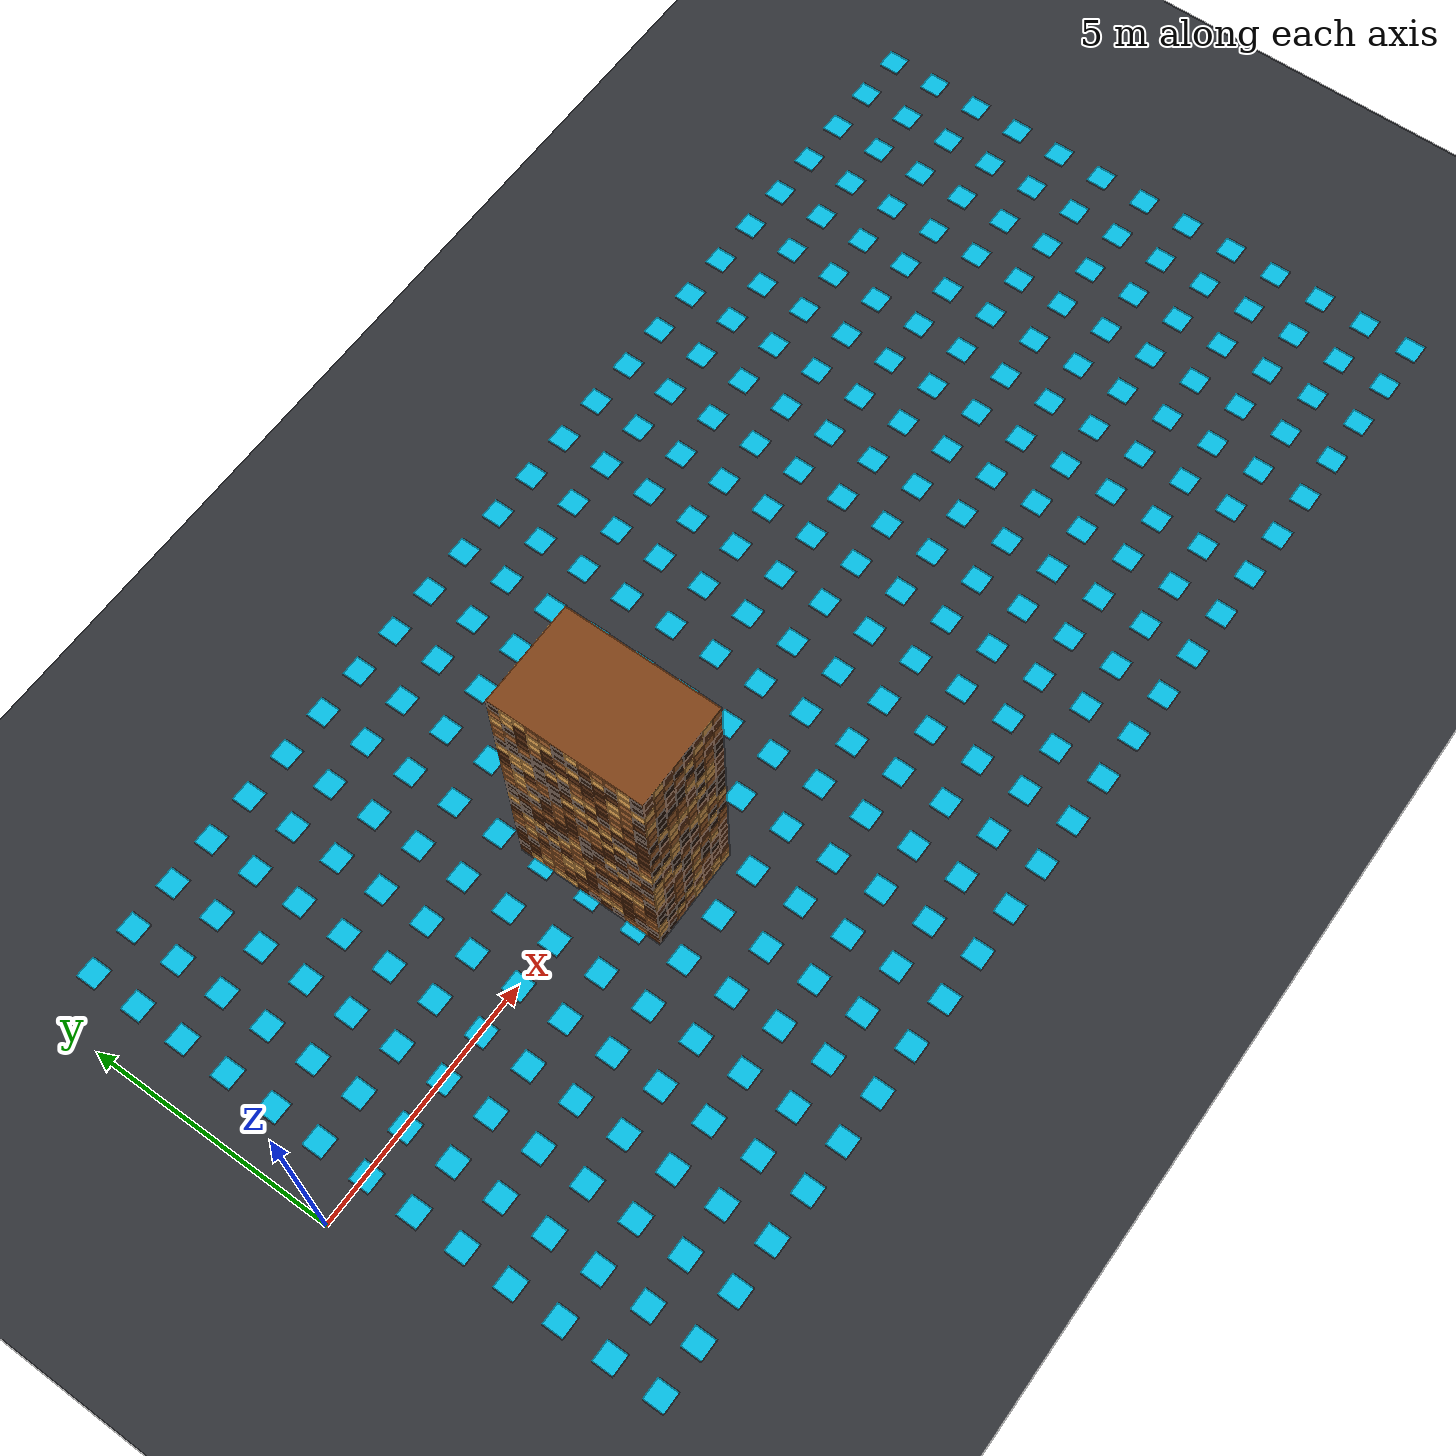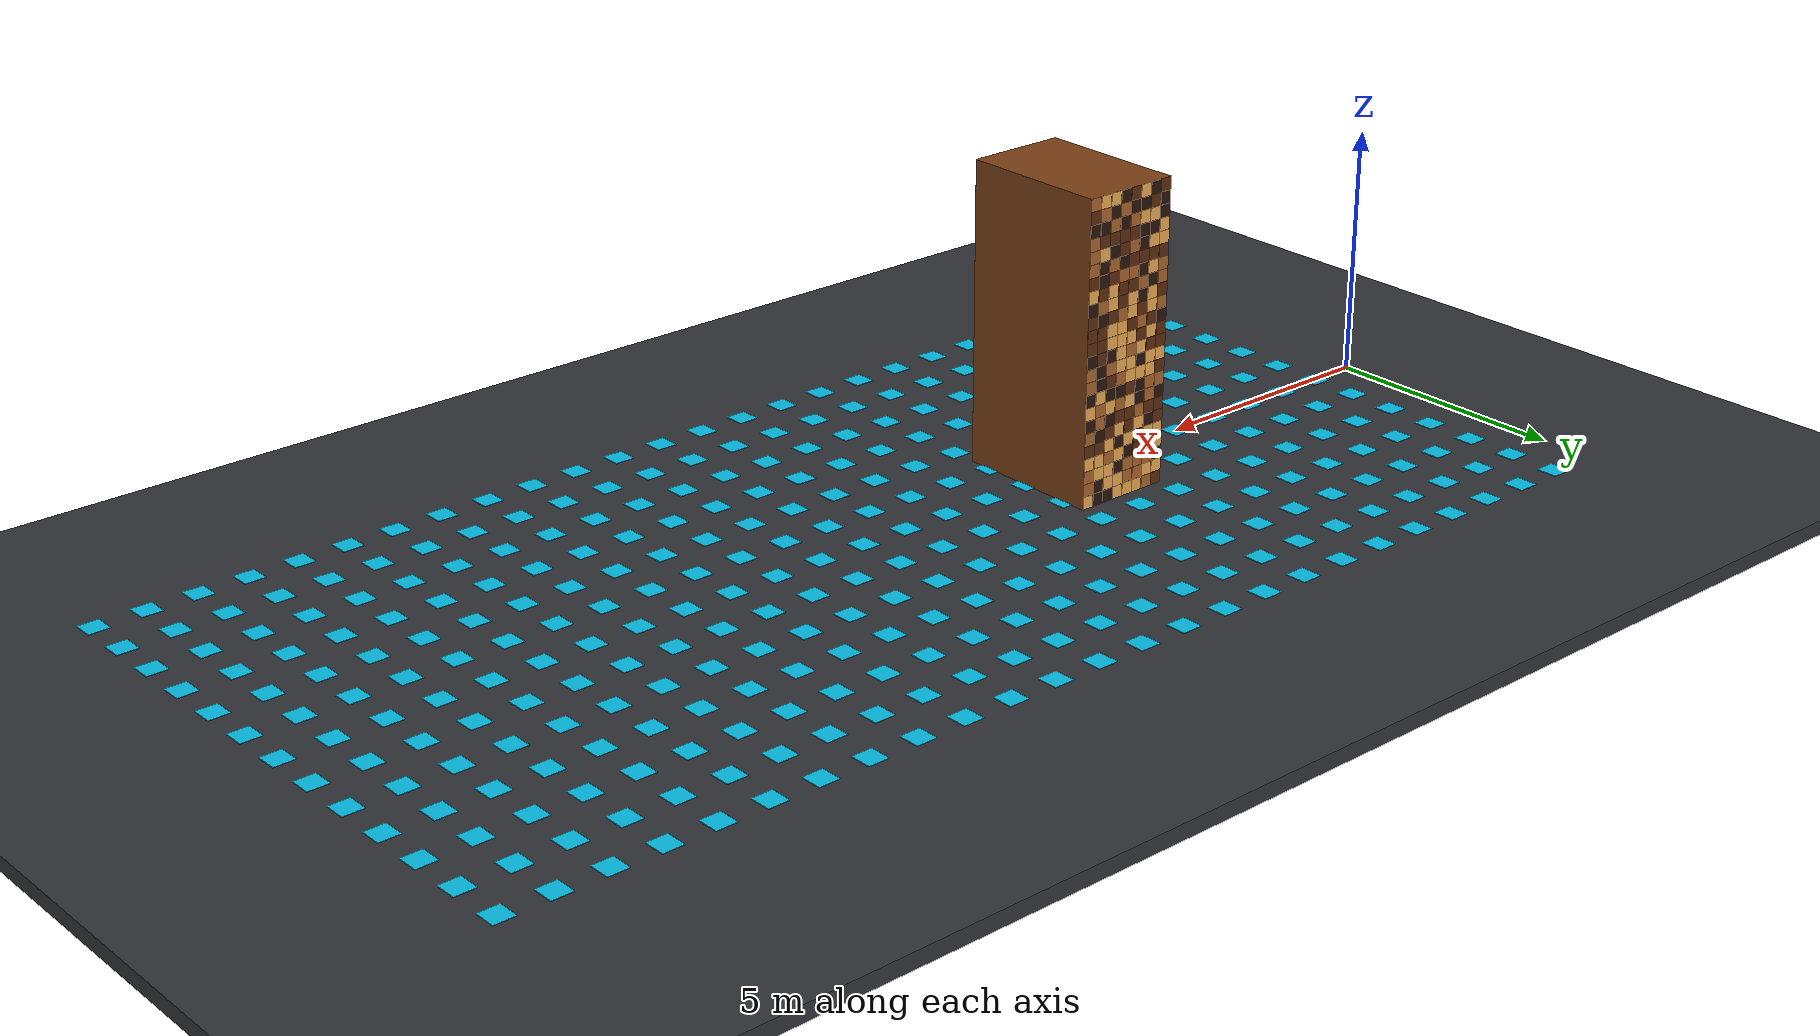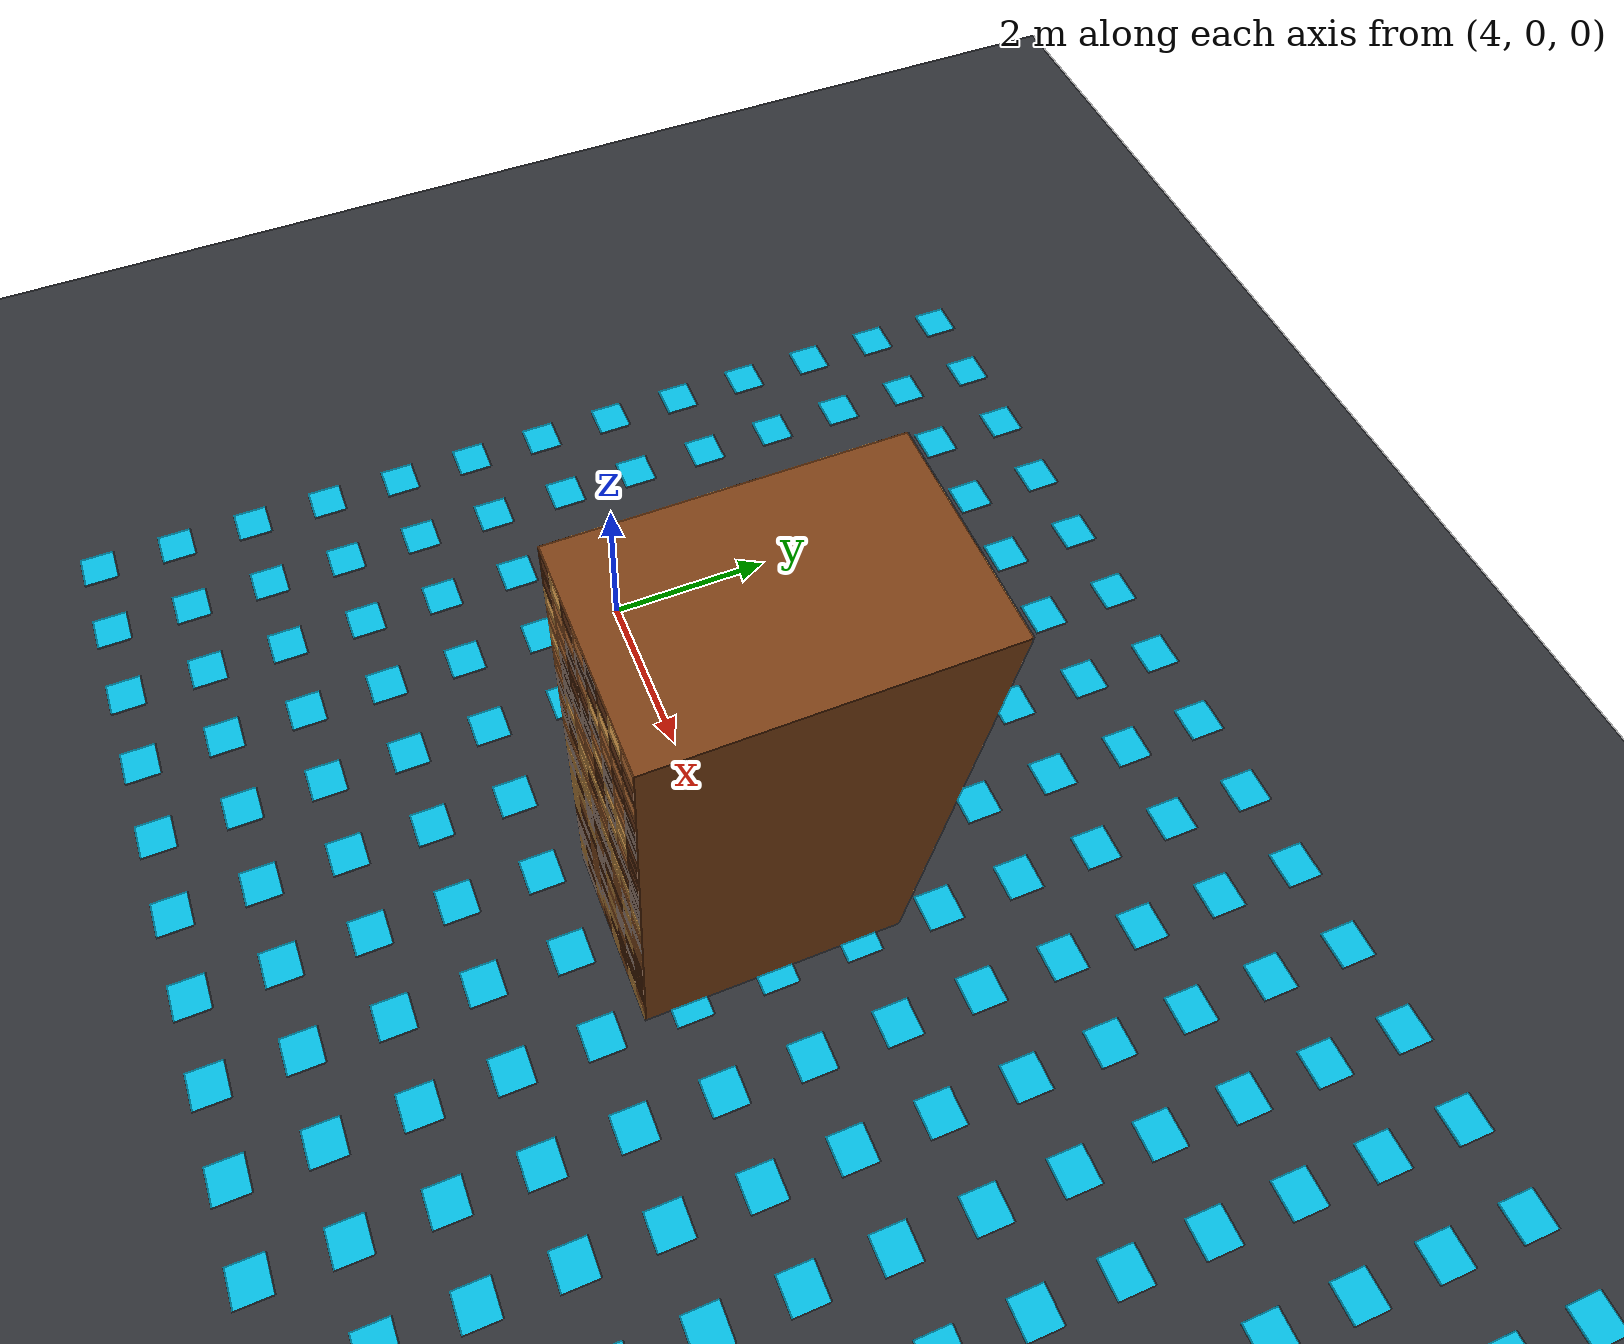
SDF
<sdf version="1.9">
 <world name="monocular_visual_ground_dense">
  <physics name="1ms" type="ignore">
   <max_step_size>0.001</max_step_size>
   <real_time_factor>1.0</real_time_factor>
  </physics>
  <plugin filename="gz-sim-physics-system" name="gz::sim::systems::Physics"/>
  <plugin filename="gz-sim-sensors-system" name="gz::sim::systems::Sensors">
   <render_engine>ogre2</render_engine>
  </plugin>
  <plugin filename="gz-sim-user-commands-system" name="gz::sim::systems::UserCommands"/>
  <plugin filename="gz-sim-scene-broadcaster-system" name="gz::sim::systems::SceneBroadcaster"/>
  <plugin filename="gz-sim-imu-system" name="gz::sim::systems::Imu"/>
  <plugin filename="gz-sim-magnetometer-system" name="gz::sim::systems::Magnetometer"/>
  <plugin filename="gz-sim-air-pressure-system" name="gz::sim::systems::AirPressure"/>
  <plugin filename="gz-sim-navsat-system" name="gz::sim::systems::NavSat"/>
  <spherical_coordinates>
   <surface_model>EARTH_WGS84</surface_model>
   <latitude_deg>-35.363262</latitude_deg>
   <longitude_deg>149.165237</longitude_deg>
   <elevation>584</elevation>
   <heading_deg>0</heading_deg>
  </spherical_coordinates>
  <magnetic_field>2.1e-5 5.0e-6 -4.2e-5</magnetic_field>
  <scene><ambient>0.45 0.45 0.45 1</ambient><background>0.08 0.1 0.14 1</background><grid>true</grid></scene>
  <light type="directional" name="sun">
   <pose>0 0 40 0 0 0</pose>
   <diffuse>0.9 0.9 0.9 1</diffuse>
   <direction>-0.4 0.2 -1</direction>
  </light>
  <model name="asphalt">
   <static>true</static>
   <pose>150 0 -0.15 0 0 0</pose>
   <link name="body">
    <collision name="collision"><geometry><box><size>400 60 0.3</size></box></geometry></collision>
    <visual name="visual">
     <geometry><box><size>400 60 0.3</size></box></geometry>
     <material><ambient>.19 .20 .22 1</ambient><diffuse>.19 .20 .22 1</diffuse></material>
    </visual>
    <visual name="camera_ground_marker_0_0">
     <pose>-149 -6 0.156 0 0 0</pose>
     <geometry><box><size>0.42 0.42 0.012</size></box></geometry>
     <material><ambient>0.02 0.75 0.9 1</ambient><diffuse>0.02 0.75 0.9 1</diffuse></material>
    </visual>
    <visual name="camera_ground_marker_0_1">
     <pose>-149 -5 0.156 0 0 0</pose>
     <geometry><box><size>0.42 0.42 0.012</size></box></geometry>
     <material><ambient>0.02 0.75 0.9 1</ambient><diffuse>0.02 0.75 0.9 1</diffuse></material>
    </visual>
    <visual name="camera_ground_marker_0_2">
     <pose>-149 -4 0.156 0 0 0</pose>
     <geometry><box><size>0.42 0.42 0.012</size></box></geometry>
     <material><ambient>0.02 0.75 0.9 1</ambient><diffuse>0.02 0.75 0.9 1</diffuse></material>
    </visual>
    <visual name="camera_ground_marker_0_3">
     <pose>-149 -3 0.156 0 0 0</pose>
     <geometry><box><size>0.42 0.42 0.012</size></box></geometry>
     <material><ambient>0.02 0.75 0.9 1</ambient><diffuse>0.02 0.75 0.9 1</diffuse></material>
    </visual>
    <visual name="camera_ground_marker_0_4">
     <pose>-149 -2 0.156 0 0 0</pose>
     <geometry><box><size>0.42 0.42 0.012</size></box></geometry>
     <material><ambient>0.02 0.75 0.9 1</ambient><diffuse>0.02 0.75 0.9 1</diffuse></material>
    </visual>
    <visual name="camera_ground_marker_0_5">
     <pose>-149 -1 0.156 0 0 0</pose>
     <geometry><box><size>0.42 0.42 0.012</size></box></geometry>
     <material><ambient>0.02 0.75 0.9 1</ambient><diffuse>0.02 0.75 0.9 1</diffuse></material>
    </visual>
    <visual name="camera_ground_marker_0_6">
     <pose>-149 0 0.156 0 0 0</pose>
     <geometry><box><size>0.42 0.42 0.012</size></box></geometry>
     <material><ambient>0.02 0.75 0.9 1</ambient><diffuse>0.02 0.75 0.9 1</diffuse></material>
    </visual>
    <visual name="camera_ground_marker_0_7">
     <pose>-149 1 0.156 0 0 0</pose>
     <geometry><box><size>0.42 0.42 0.012</size></box></geometry>
     <material><ambient>0.02 0.75 0.9 1</ambient><diffuse>0.02 0.75 0.9 1</diffuse></material>
    </visual>
    <visual name="camera_ground_marker_0_8">
     <pose>-149 2 0.156 0 0 0</pose>
     <geometry><box><size>0.42 0.42 0.012</size></box></geometry>
     <material><ambient>0.02 0.75 0.9 1</ambient><diffuse>0.02 0.75 0.9 1</diffuse></material>
    </visual>
    <visual name="camera_ground_marker_0_9">
     <pose>-149 3 0.156 0 0 0</pose>
     <geometry><box><size>0.42 0.42 0.012</size></box></geometry>
     <material><ambient>0.02 0.75 0.9 1</ambient><diffuse>0.02 0.75 0.9 1</diffuse></material>
    </visual>
    <visual name="camera_ground_marker_0_10">
     <pose>-149 4 0.156 0 0 0</pose>
     <geometry><box><size>0.42 0.42 0.012</size></box></geometry>
     <material><ambient>0.02 0.75 0.9 1</ambient><diffuse>0.02 0.75 0.9 1</diffuse></material>
    </visual>
    <visual name="camera_ground_marker_0_11">
     <pose>-149 5 0.156 0 0 0</pose>
     <geometry><box><size>0.42 0.42 0.012</size></box></geometry>
     <material><ambient>0.02 0.75 0.9 1</ambient><diffuse>0.02 0.75 0.9 1</diffuse></material>
    </visual>
    <visual name="camera_ground_marker_0_12">
     <pose>-149 6 0.156 0 0 0</pose>
     <geometry><box><size>0.42 0.42 0.012</size></box></geometry>
     <material><ambient>0.02 0.75 0.9 1</ambient><diffuse>0.02 0.75 0.9 1</diffuse></material>
    </visual>
    <visual name="camera_ground_marker_1_0">
     <pose>-148 -6 0.156 0 0 0</pose>
     <geometry><box><size>0.42 0.42 0.012</size></box></geometry>
     <material><ambient>0.02 0.75 0.9 1</ambient><diffuse>0.02 0.75 0.9 1</diffuse></material>
    </visual>
    <visual name="camera_ground_marker_1_1">
     <pose>-148 -5 0.156 0 0 0</pose>
     <geometry><box><size>0.42 0.42 0.012</size></box></geometry>
     <material><ambient>0.02 0.75 0.9 1</ambient><diffuse>0.02 0.75 0.9 1</diffuse></material>
    </visual>
    <visual name="camera_ground_marker_1_2">
     <pose>-148 -4 0.156 0 0 0</pose>
     <geometry><box><size>0.42 0.42 0.012</size></box></geometry>
     <material><ambient>0.02 0.75 0.9 1</ambient><diffuse>0.02 0.75 0.9 1</diffuse></material>
    </visual>
    <visual name="camera_ground_marker_1_3">
     <pose>-148 -3 0.156 0 0 0</pose>
     <geometry><box><size>0.42 0.42 0.012</size></box></geometry>
     <material><ambient>0.02 0.75 0.9 1</ambient><diffuse>0.02 0.75 0.9 1</diffuse></material>
    </visual>
    <visual name="camera_ground_marker_1_4">
     <pose>-148 -2 0.156 0 0 0</pose>
     <geometry><box><size>0.42 0.42 0.012</size></box></geometry>
     <material><ambient>0.02 0.75 0.9 1</ambient><diffuse>0.02 0.75 0.9 1</diffuse></material>
    </visual>
    <visual name="camera_ground_marker_1_5">
     <pose>-148 -1 0.156 0 0 0</pose>
     <geometry><box><size>0.42 0.42 0.012</size></box></geometry>
     <material><ambient>0.02 0.75 0.9 1</ambient><diffuse>0.02 0.75 0.9 1</diffuse></material>
    </visual>
    <visual name="camera_ground_marker_1_6">
     <pose>-148 0 0.156 0 0 0</pose>
     <geometry><box><size>0.42 0.42 0.012</size></box></geometry>
     <material><ambient>0.02 0.75 0.9 1</ambient><diffuse>0.02 0.75 0.9 1</diffuse></material>
    </visual>
    <visual name="camera_ground_marker_1_7">
     <pose>-148 1 0.156 0 0 0</pose>
     <geometry><box><size>0.42 0.42 0.012</size></box></geometry>
     <material><ambient>0.02 0.75 0.9 1</ambient><diffuse>0.02 0.75 0.9 1</diffuse></material>
    </visual>
    <visual name="camera_ground_marker_1_8">
     <pose>-148 2 0.156 0 0 0</pose>
     <geometry><box><size>0.42 0.42 0.012</size></box></geometry>
     <material><ambient>0.02 0.75 0.9 1</ambient><diffuse>0.02 0.75 0.9 1</diffuse></material>
    </visual>
    <visual name="camera_ground_marker_1_9">
     <pose>-148 3 0.156 0 0 0</pose>
     <geometry><box><size>0.42 0.42 0.012</size></box></geometry>
     <material><ambient>0.02 0.75 0.9 1</ambient><diffuse>0.02 0.75 0.9 1</diffuse></material>
    </visual>
    <visual name="camera_ground_marker_1_10">
     <pose>-148 4 0.156 0 0 0</pose>
     <geometry><box><size>0.42 0.42 0.012</size></box></geometry>
     <material><ambient>0.02 0.75 0.9 1</ambient><diffuse>0.02 0.75 0.9 1</diffuse></material>
    </visual>
    <visual name="camera_ground_marker_1_11">
     <pose>-148 5 0.156 0 0 0</pose>
     <geometry><box><size>0.42 0.42 0.012</size></box></geometry>
     <material><ambient>0.02 0.75 0.9 1</ambient><diffuse>0.02 0.75 0.9 1</diffuse></material>
    </visual>
    <visual name="camera_ground_marker_1_12">
     <pose>-148 6 0.156 0 0 0</pose>
     <geometry><box><size>0.42 0.42 0.012</size></box></geometry>
     <material><ambient>0.02 0.75 0.9 1</ambient><diffuse>0.02 0.75 0.9 1</diffuse></material>
    </visual>
    <visual name="camera_ground_marker_2_0">
     <pose>-147 -6 0.156 0 0 0</pose>
     <geometry><box><size>0.42 0.42 0.012</size></box></geometry>
     <material><ambient>0.02 0.75 0.9 1</ambient><diffuse>0.02 0.75 0.9 1</diffuse></material>
    </visual>
    <visual name="camera_ground_marker_2_1">
     <pose>-147 -5 0.156 0 0 0</pose>
     <geometry><box><size>0.42 0.42 0.012</size></box></geometry>
     <material><ambient>0.02 0.75 0.9 1</ambient><diffuse>0.02 0.75 0.9 1</diffuse></material>
    </visual>
    <visual name="camera_ground_marker_2_2">
     <pose>-147 -4 0.156 0 0 0</pose>
     <geometry><box><size>0.42 0.42 0.012</size></box></geometry>
     <material><ambient>0.02 0.75 0.9 1</ambient><diffuse>0.02 0.75 0.9 1</diffuse></material>
    </visual>
    <visual name="camera_ground_marker_2_3">
     <pose>-147 -3 0.156 0 0 0</pose>
     <geometry><box><size>0.42 0.42 0.012</size></box></geometry>
     <material><ambient>0.02 0.75 0.9 1</ambient><diffuse>0.02 0.75 0.9 1</diffuse></material>
    </visual>
    <visual name="camera_ground_marker_2_4">
     <pose>-147 -2 0.156 0 0 0</pose>
     <geometry><box><size>0.42 0.42 0.012</size></box></geometry>
     <material><ambient>0.02 0.75 0.9 1</ambient><diffuse>0.02 0.75 0.9 1</diffuse></material>
    </visual>
    <visual name="camera_ground_marker_2_5">
     <pose>-147 -1 0.156 0 0 0</pose>
     <geometry><box><size>0.42 0.42 0.012</size></box></geometry>
     <material><ambient>0.02 0.75 0.9 1</ambient><diffuse>0.02 0.75 0.9 1</diffuse></material>
    </visual>
    <visual name="camera_ground_marker_2_6">
     <pose>-147 0 0.156 0 0 0</pose>
     <geometry><box><size>0.42 0.42 0.012</size></box></geometry>
     <material><ambient>0.02 0.75 0.9 1</ambient><diffuse>0.02 0.75 0.9 1</diffuse></material>
    </visual>
    <visual name="camera_ground_marker_2_7">
     <pose>-147 1 0.156 0 0 0</pose>
     <geometry><box><size>0.42 0.42 0.012</size></box></geometry>
     <material><ambient>0.02 0.75 0.9 1</ambient><diffuse>0.02 0.75 0.9 1</diffuse></material>
    </visual>
    <visual name="camera_ground_marker_2_8">
     <pose>-147 2 0.156 0 0 0</pose>
     <geometry><box><size>0.42 0.42 0.012</size></box></geometry>
     <material><ambient>0.02 0.75 0.9 1</ambient><diffuse>0.02 0.75 0.9 1</diffuse></material>
    </visual>
    <visual name="camera_ground_marker_2_9">
     <pose>-147 3 0.156 0 0 0</pose>
     <geometry><box><size>0.42 0.42 0.012</size></box></geometry>
     <material><ambient>0.02 0.75 0.9 1</ambient><diffuse>0.02 0.75 0.9 1</diffuse></material>
    </visual>
    <visual name="camera_ground_marker_2_10">
     <pose>-147 4 0.156 0 0 0</pose>
     <geometry><box><size>0.42 0.42 0.012</size></box></geometry>
     <material><ambient>0.02 0.75 0.9 1</ambient><diffuse>0.02 0.75 0.9 1</diffuse></material>
    </visual>
    <visual name="camera_ground_marker_2_11">
     <pose>-147 5 0.156 0 0 0</pose>
     <geometry><box><size>0.42 0.42 0.012</size></box></geometry>
     <material><ambient>0.02 0.75 0.9 1</ambient><diffuse>0.02 0.75 0.9 1</diffuse></material>
    </visual>
    <visual name="camera_ground_marker_2_12">
     <pose>-147 6 0.156 0 0 0</pose>
     <geometry><box><size>0.42 0.42 0.012</size></box></geometry>
     <material><ambient>0.02 0.75 0.9 1</ambient><diffuse>0.02 0.75 0.9 1</diffuse></material>
    </visual>
    <visual name="camera_ground_marker_3_0">
     <pose>-146 -6 0.156 0 0 0</pose>
     <geometry><box><size>0.42 0.42 0.012</size></box></geometry>
     <material><ambient>0.02 0.75 0.9 1</ambient><diffuse>0.02 0.75 0.9 1</diffuse></material>
    </visual>
    <visual name="camera_ground_marker_3_1">
     <pose>-146 -5 0.156 0 0 0</pose>
     <geometry><box><size>0.42 0.42 0.012</size></box></geometry>
     <material><ambient>0.02 0.75 0.9 1</ambient><diffuse>0.02 0.75 0.9 1</diffuse></material>
    </visual>
    <visual name="camera_ground_marker_3_2">
     <pose>-146 -4 0.156 0 0 0</pose>
     <geometry><box><size>0.42 0.42 0.012</size></box></geometry>
     <material><ambient>0.02 0.75 0.9 1</ambient><diffuse>0.02 0.75 0.9 1</diffuse></material>
    </visual>
    <visual name="camera_ground_marker_3_3">
     <pose>-146 -3 0.156 0 0 0</pose>
     <geometry><box><size>0.42 0.42 0.012</size></box></geometry>
     <material><ambient>0.02 0.75 0.9 1</ambient><diffuse>0.02 0.75 0.9 1</diffuse></material>
    </visual>
    <visual name="camera_ground_marker_3_4">
     <pose>-146 -2 0.156 0 0 0</pose>
     <geometry><box><size>0.42 0.42 0.012</size></box></geometry>
     <material><ambient>0.02 0.75 0.9 1</ambient><diffuse>0.02 0.75 0.9 1</diffuse></material>
    </visual>
    <visual name="camera_ground_marker_3_5">
     <pose>-146 -1 0.156 0 0 0</pose>
     <geometry><box><size>0.42 0.42 0.012</size></box></geometry>
     <material><ambient>0.02 0.75 0.9 1</ambient><diffuse>0.02 0.75 0.9 1</diffuse></material>
    </visual>
    <visual name="camera_ground_marker_3_6">
     <pose>-146 0 0.156 0 0 0</pose>
     <geometry><box><size>0.42 0.42 0.012</size></box></geometry>
     <material><ambient>0.02 0.75 0.9 1</ambient><diffuse>0.02 0.75 0.9 1</diffuse></material>
    </visual>
    <visual name="camera_ground_marker_3_7">
     <pose>-146 1 0.156 0 0 0</pose>
     <geometry><box><size>0.42 0.42 0.012</size></box></geometry>
     <material><ambient>0.02 0.75 0.9 1</ambient><diffuse>0.02 0.75 0.9 1</diffuse></material>
    </visual>
    <visual name="camera_ground_marker_3_8">
     <pose>-146 2 0.156 0 0 0</pose>
     <geometry><box><size>0.42 0.42 0.012</size></box></geometry>
     <material><ambient>0.02 0.75 0.9 1</ambient><diffuse>0.02 0.75 0.9 1</diffuse></material>
    </visual>
    <visual name="camera_ground_marker_3_9">
     <pose>-146 3 0.156 0 0 0</pose>
     <geometry><box><size>0.42 0.42 0.012</size></box></geometry>
     <material><ambient>0.02 0.75 0.9 1</ambient><diffuse>0.02 0.75 0.9 1</diffuse></material>
    </visual>
    <visual name="camera_ground_marker_3_10">
     <pose>-146 4 0.156 0 0 0</pose>
     <geometry><box><size>0.42 0.42 0.012</size></box></geometry>
     <material><ambient>0.02 0.75 0.9 1</ambient><diffuse>0.02 0.75 0.9 1</diffuse></material>
    </visual>
    <visual name="camera_ground_marker_3_11">
     <pose>-146 5 0.156 0 0 0</pose>
     <geometry><box><size>0.42 0.42 0.012</size></box></geometry>
     <material><ambient>0.02 0.75 0.9 1</ambient><diffuse>0.02 0.75 0.9 1</diffuse></material>
    </visual>
    <visual name="camera_ground_marker_3_12">
     <pose>-146 6 0.156 0 0 0</pose>
     <geometry><box><size>0.42 0.42 0.012</size></box></geometry>
     <material><ambient>0.02 0.75 0.9 1</ambient><diffuse>0.02 0.75 0.9 1</diffuse></material>
    </visual>
    <visual name="camera_ground_marker_4_0">
     <pose>-145 -6 0.156 0 0 0</pose>
     <geometry><box><size>0.42 0.42 0.012</size></box></geometry>
     <material><ambient>0.02 0.75 0.9 1</ambient><diffuse>0.02 0.75 0.9 1</diffuse></material>
    </visual>
    <visual name="camera_ground_marker_4_1">
     <pose>-145 -5 0.156 0 0 0</pose>
     <geometry><box><size>0.42 0.42 0.012</size></box></geometry>
     <material><ambient>0.02 0.75 0.9 1</ambient><diffuse>0.02 0.75 0.9 1</diffuse></material>
    </visual>
    <visual name="camera_ground_marker_4_2">
     <pose>-145 -4 0.156 0 0 0</pose>
     <geometry><box><size>0.42 0.42 0.012</size></box></geometry>
     <material><ambient>0.02 0.75 0.9 1</ambient><diffuse>0.02 0.75 0.9 1</diffuse></material>
    </visual>
    <visual name="camera_ground_marker_4_3">
     <pose>-145 -3 0.156 0 0 0</pose>
     <geometry><box><size>0.42 0.42 0.012</size></box></geometry>
     <material><ambient>0.02 0.75 0.9 1</ambient><diffuse>0.02 0.75 0.9 1</diffuse></material>
    </visual>
    <visual name="camera_ground_marker_4_4">
     <pose>-145 -2 0.156 0 0 0</pose>
     <geometry><box><size>0.42 0.42 0.012</size></box></geometry>
     <material><ambient>0.02 0.75 0.9 1</ambient><diffuse>0.02 0.75 0.9 1</diffuse></material>
    </visual>
    <visual name="camera_ground_marker_4_5">
     <pose>-145 -1 0.156 0 0 0</pose>
     <geometry><box><size>0.42 0.42 0.012</size></box></geometry>
     <material><ambient>0.02 0.75 0.9 1</ambient><diffuse>0.02 0.75 0.9 1</diffuse></material>
    </visual>
    <visual name="camera_ground_marker_4_6">
     <pose>-145 0 0.156 0 0 0</pose>
     <geometry><box><size>0.42 0.42 0.012</size></box></geometry>
     <material><ambient>0.02 0.75 0.9 1</ambient><diffuse>0.02 0.75 0.9 1</diffuse></material>
    </visual>
    <visual name="camera_ground_marker_4_7">
     <pose>-145 1 0.156 0 0 0</pose>
     <geometry><box><size>0.42 0.42 0.012</size></box></geometry>
     <material><ambient>0.02 0.75 0.9 1</ambient><diffuse>0.02 0.75 0.9 1</diffuse></material>
    </visual>
    <visual name="camera_ground_marker_4_8">
     <pose>-145 2 0.156 0 0 0</pose>
     <geometry><box><size>0.42 0.42 0.012</size></box></geometry>
     <material><ambient>0.02 0.75 0.9 1</ambient><diffuse>0.02 0.75 0.9 1</diffuse></material>
    </visual>
    <visual name="camera_ground_marker_4_9">
     <pose>-145 3 0.156 0 0 0</pose>
     <geometry><box><size>0.42 0.42 0.012</size></box></geometry>
     <material><ambient>0.02 0.75 0.9 1</ambient><diffuse>0.02 0.75 0.9 1</diffuse></material>
    </visual>
    <visual name="camera_ground_marker_4_10">
     <pose>-145 4 0.156 0 0 0</pose>
     <geometry><box><size>0.42 0.42 0.012</size></box></geometry>
     <material><ambient>0.02 0.75 0.9 1</ambient><diffuse>0.02 0.75 0.9 1</diffuse></material>
    </visual>
    <visual name="camera_ground_marker_4_11">
     <pose>-145 5 0.156 0 0 0</pose>
     <geometry><box><size>0.42 0.42 0.012</size></box></geometry>
     <material><ambient>0.02 0.75 0.9 1</ambient><diffuse>0.02 0.75 0.9 1</diffuse></material>
    </visual>
    <visual name="camera_ground_marker_4_12">
     <pose>-145 6 0.156 0 0 0</pose>
     <geometry><box><size>0.42 0.42 0.012</size></box></geometry>
     <material><ambient>0.02 0.75 0.9 1</ambient><diffuse>0.02 0.75 0.9 1</diffuse></material>
    </visual>
    <visual name="camera_ground_marker_5_0">
     <pose>-144 -6 0.156 0 0 0</pose>
     <geometry><box><size>0.42 0.42 0.012</size></box></geometry>
     <material><ambient>0.02 0.75 0.9 1</ambient><diffuse>0.02 0.75 0.9 1</diffuse></material>
    </visual>
    <visual name="camera_ground_marker_5_1">
     <pose>-144 -5 0.156 0 0 0</pose>
     <geometry><box><size>0.42 0.42 0.012</size></box></geometry>
     <material><ambient>0.02 0.75 0.9 1</ambient><diffuse>0.02 0.75 0.9 1</diffuse></material>
    </visual>
    <visual name="camera_ground_marker_5_2">
     <pose>-144 -4 0.156 0 0 0</pose>
     <geometry><box><size>0.42 0.42 0.012</size></box></geometry>
     <material><ambient>0.02 0.75 0.9 1</ambient><diffuse>0.02 0.75 0.9 1</diffuse></material>
    </visual>
    <visual name="camera_ground_marker_5_3">
     <pose>-144 -3 0.156 0 0 0</pose>
     <geometry><box><size>0.42 0.42 0.012</size></box></geometry>
     <material><ambient>0.02 0.75 0.9 1</ambient><diffuse>0.02 0.75 0.9 1</diffuse></material>
    </visual>
    <visual name="camera_ground_marker_5_4">
     <pose>-144 -2 0.156 0 0 0</pose>
     <geometry><box><size>0.42 0.42 0.012</size></box></geometry>
     <material><ambient>0.02 0.75 0.9 1</ambient><diffuse>0.02 0.75 0.9 1</diffuse></material>
    </visual>
    <visual name="camera_ground_marker_5_5">
     <pose>-144 -1 0.156 0 0 0</pose>
     <geometry><box><size>0.42 0.42 0.012</size></box></geometry>
     <material><ambient>0.02 0.75 0.9 1</ambient><diffuse>0.02 0.75 0.9 1</diffuse></material>
    </visual>
    <visual name="camera_ground_marker_5_6">
     <pose>-144 0 0.156 0 0 0</pose>
     <geometry><box><size>0.42 0.42 0.012</size></box></geometry>
     <material><ambient>0.02 0.75 0.9 1</ambient><diffuse>0.02 0.75 0.9 1</diffuse></material>
    </visual>
    <visual name="camera_ground_marker_5_7">
     <pose>-144 1 0.156 0 0 0</pose>
     <geometry><box><size>0.42 0.42 0.012</size></box></geometry>
     <material><ambient>0.02 0.75 0.9 1</ambient><diffuse>0.02 0.75 0.9 1</diffuse></material>
    </visual>
    <visual name="camera_ground_marker_5_8">
     <pose>-144 2 0.156 0 0 0</pose>
     <geometry><box><size>0.42 0.42 0.012</size></box></geometry>
     <material><ambient>0.02 0.75 0.9 1</ambient><diffuse>0.02 0.75 0.9 1</diffuse></material>
    </visual>
    <visual name="camera_ground_marker_5_9">
     <pose>-144 3 0.156 0 0 0</pose>
     <geometry><box><size>0.42 0.42 0.012</size></box></geometry>
     <material><ambient>0.02 0.75 0.9 1</ambient><diffuse>0.02 0.75 0.9 1</diffuse></material>
    </visual>
    <visual name="camera_ground_marker_5_10">
     <pose>-144 4 0.156 0 0 0</pose>
     <geometry><box><size>0.42 0.42 0.012</size></box></geometry>
     <material><ambient>0.02 0.75 0.9 1</ambient><diffuse>0.02 0.75 0.9 1</diffuse></material>
    </visual>
    <visual name="camera_ground_marker_5_11">
     <pose>-144 5 0.156 0 0 0</pose>
     <geometry><box><size>0.42 0.42 0.012</size></box></geometry>
     <material><ambient>0.02 0.75 0.9 1</ambient><diffuse>0.02 0.75 0.9 1</diffuse></material>
    </visual>
    <visual name="camera_ground_marker_5_12">
     <pose>-144 6 0.156 0 0 0</pose>
     <geometry><box><size>0.42 0.42 0.012</size></box></geometry>
     <material><ambient>0.02 0.75 0.9 1</ambient><diffuse>0.02 0.75 0.9 1</diffuse></material>
    </visual>
    <visual name="camera_ground_marker_6_0">
     <pose>-143 -6 0.156 0 0 0</pose>
     <geometry><box><size>0.42 0.42 0.012</size></box></geometry>
     <material><ambient>0.02 0.75 0.9 1</ambient><diffuse>0.02 0.75 0.9 1</diffuse></material>
    </visual>
    <visual name="camera_ground_marker_6_1">
     <pose>-143 -5 0.156 0 0 0</pose>
     <geometry><box><size>0.42 0.42 0.012</size></box></geometry>
     <material><ambient>0.02 0.75 0.9 1</ambient><diffuse>0.02 0.75 0.9 1</diffuse></material>
    </visual>
    <visual name="camera_ground_marker_6_2">
     <pose>-143 -4 0.156 0 0 0</pose>
     <geometry><box><size>0.42 0.42 0.012</size></box></geometry>
     <material><ambient>0.02 0.75 0.9 1</ambient><diffuse>0.02 0.75 0.9 1</diffuse></material>
    </visual>
    <visual name="camera_ground_marker_6_3">
     <pose>-143 -3 0.156 0 0 0</pose>
     <geometry><box><size>0.42 0.42 0.012</size></box></geometry>
     <material><ambient>0.02 0.75 0.9 1</ambient><diffuse>0.02 0.75 0.9 1</diffuse></material>
    </visual>
    <visual name="camera_ground_marker_6_4">
     <pose>-143 -2 0.156 0 0 0</pose>
     <geometry><box><size>0.42 0.42 0.012</size></box></geometry>
     <material><ambient>0.02 0.75 0.9 1</ambient><diffuse>0.02 0.75 0.9 1</diffuse></material>
    </visual>
    <visual name="camera_ground_marker_6_5">
     <pose>-143 -1 0.156 0 0 0</pose>
     <geometry><box><size>0.42 0.42 0.012</size></box></geometry>
     <material><ambient>0.02 0.75 0.9 1</ambient><diffuse>0.02 0.75 0.9 1</diffuse></material>
    </visual>
    <visual name="camera_ground_marker_6_6">
     <pose>-143 0 0.156 0 0 0</pose>
     <geometry><box><size>0.42 0.42 0.012</size></box></geometry>
     <material><ambient>0.02 0.75 0.9 1</ambient><diffuse>0.02 0.75 0.9 1</diffuse></material>
    </visual>
    <visual name="camera_ground_marker_6_7">
     <pose>-143 1 0.156 0 0 0</pose>
     <geometry><box><size>0.42 0.42 0.012</size></box></geometry>
     <material><ambient>0.02 0.75 0.9 1</ambient><diffuse>0.02 0.75 0.9 1</diffuse></material>
    </visual>
    <visual name="camera_ground_marker_6_8">
     <pose>-143 2 0.156 0 0 0</pose>
     <geometry><box><size>0.42 0.42 0.012</size></box></geometry>
     <material><ambient>0.02 0.75 0.9 1</ambient><diffuse>0.02 0.75 0.9 1</diffuse></material>
    </visual>
    <visual name="camera_ground_marker_6_9">
     <pose>-143 3 0.156 0 0 0</pose>
     <geometry><box><size>0.42 0.42 0.012</size></box></geometry>
     <material><ambient>0.02 0.75 0.9 1</ambient><diffuse>0.02 0.75 0.9 1</diffuse></material>
    </visual>
    <visual name="camera_ground_marker_6_10">
     <pose>-143 4 0.156 0 0 0</pose>
     <geometry><box><size>0.42 0.42 0.012</size></box></geometry>
     <material><ambient>0.02 0.75 0.9 1</ambient><diffuse>0.02 0.75 0.9 1</diffuse></material>
    </visual>
    <visual name="camera_ground_marker_6_11">
     <pose>-143 5 0.156 0 0 0</pose>
     <geometry><box><size>0.42 0.42 0.012</size></box></geometry>
     <material><ambient>0.02 0.75 0.9 1</ambient><diffuse>0.02 0.75 0.9 1</diffuse></material>
    </visual>
    <visual name="camera_ground_marker_6_12">
     <pose>-143 6 0.156 0 0 0</pose>
     <geometry><box><size>0.42 0.42 0.012</size></box></geometry>
     <material><ambient>0.02 0.75 0.9 1</ambient><diffuse>0.02 0.75 0.9 1</diffuse></material>
    </visual>
    <visual name="camera_ground_marker_7_0">
     <pose>-142 -6 0.156 0 0 0</pose>
     <geometry><box><size>0.42 0.42 0.012</size></box></geometry>
     <material><ambient>0.02 0.75 0.9 1</ambient><diffuse>0.02 0.75 0.9 1</diffuse></material>
    </visual>
    <visual name="camera_ground_marker_7_1">
     <pose>-142 -5 0.156 0 0 0</pose>
     <geometry><box><size>0.42 0.42 0.012</size></box></geometry>
     <material><ambient>0.02 0.75 0.9 1</ambient><diffuse>0.02 0.75 0.9 1</diffuse></material>
    </visual>
    <visual name="camera_ground_marker_7_2">
     <pose>-142 -4 0.156 0 0 0</pose>
     <geometry><box><size>0.42 0.42 0.012</size></box></geometry>
     <material><ambient>0.02 0.75 0.9 1</ambient><diffuse>0.02 0.75 0.9 1</diffuse></material>
    </visual>
    <visual name="camera_ground_marker_7_3">
     <pose>-142 -3 0.156 0 0 0</pose>
     <geometry><box><size>0.42 0.42 0.012</size></box></geometry>
     <material><ambient>0.02 0.75 0.9 1</ambient><diffuse>0.02 0.75 0.9 1</diffuse></material>
    </visual>
    <visual name="camera_ground_marker_7_4">
     <pose>-142 -2 0.156 0 0 0</pose>
     <geometry><box><size>0.42 0.42 0.012</size></box></geometry>
     <material><ambient>0.02 0.75 0.9 1</ambient><diffuse>0.02 0.75 0.9 1</diffuse></material>
    </visual>
    <visual name="camera_ground_marker_7_5">
     <pose>-142 -1 0.156 0 0 0</pose>
     <geometry><box><size>0.42 0.42 0.012</size></box></geometry>
     <material><ambient>0.02 0.75 0.9 1</ambient><diffuse>0.02 0.75 0.9 1</diffuse></material>
    </visual>
    <visual name="camera_ground_marker_7_6">
     <pose>-142 0 0.156 0 0 0</pose>
     <geometry><box><size>0.42 0.42 0.012</size></box></geometry>
     <material><ambient>0.02 0.75 0.9 1</ambient><diffuse>0.02 0.75 0.9 1</diffuse></material>
    </visual>
    <visual name="camera_ground_marker_7_7">
     <pose>-142 1 0.156 0 0 0</pose>
     <geometry><box><size>0.42 0.42 0.012</size></box></geometry>
     <material><ambient>0.02 0.75 0.9 1</ambient><diffuse>0.02 0.75 0.9 1</diffuse></material>
    </visual>
    <visual name="camera_ground_marker_7_8">
     <pose>-142 2 0.156 0 0 0</pose>
     <geometry><box><size>0.42 0.42 0.012</size></box></geometry>
     <material><ambient>0.02 0.75 0.9 1</ambient><diffuse>0.02 0.75 0.9 1</diffuse></material>
    </visual>
    <visual name="camera_ground_marker_7_9">
     <pose>-142 3 0.156 0 0 0</pose>
     <geometry><box><size>0.42 0.42 0.012</size></box></geometry>
     <material><ambient>0.02 0.75 0.9 1</ambient><diffuse>0.02 0.75 0.9 1</diffuse></material>
    </visual>
    <visual name="camera_ground_marker_7_10">
     <pose>-142 4 0.156 0 0 0</pose>
     <geometry><box><size>0.42 0.42 0.012</size></box></geometry>
     <material><ambient>0.02 0.75 0.9 1</ambient><diffuse>0.02 0.75 0.9 1</diffuse></material>
    </visual>
    <visual name="camera_ground_marker_7_11">
     <pose>-142 5 0.156 0 0 0</pose>
     <geometry><box><size>0.42 0.42 0.012</size></box></geometry>
     <material><ambient>0.02 0.75 0.9 1</ambient><diffuse>0.02 0.75 0.9 1</diffuse></material>
    </visual>
    <visual name="camera_ground_marker_7_12">
     <pose>-142 6 0.156 0 0 0</pose>
     <geometry><box><size>0.42 0.42 0.012</size></box></geometry>
     <material><ambient>0.02 0.75 0.9 1</ambient><diffuse>0.02 0.75 0.9 1</diffuse></material>
    </visual>
    <visual name="camera_ground_marker_8_0">
     <pose>-141 -6 0.156 0 0 0</pose>
     <geometry><box><size>0.42 0.42 0.012</size></box></geometry>
     <material><ambient>0.02 0.75 0.9 1</ambient><diffuse>0.02 0.75 0.9 1</diffuse></material>
    </visual>
    <visual name="camera_ground_marker_8_1">
     <pose>-141 -5 0.156 0 0 0</pose>
     <geometry><box><size>0.42 0.42 0.012</size></box></geometry>
     <material><ambient>0.02 0.75 0.9 1</ambient><diffuse>0.02 0.75 0.9 1</diffuse></material>
    </visual>
    <visual name="camera_ground_marker_8_2">
     <pose>-141 -4 0.156 0 0 0</pose>
     <geometry><box><size>0.42 0.42 0.012</size></box></geometry>
     <material><ambient>0.02 0.75 0.9 1</ambient><diffuse>0.02 0.75 0.9 1</diffuse></material>
    </visual>
    <visual name="camera_ground_marker_8_3">
     <pose>-141 -3 0.156 0 0 0</pose>
     <geometry><box><size>0.42 0.42 0.012</size></box></geometry>
     <material><ambient>0.02 0.75 0.9 1</ambient><diffuse>0.02 0.75 0.9 1</diffuse></material>
    </visual>
    <visual name="camera_ground_marker_8_4">
     <pose>-141 -2 0.156 0 0 0</pose>
     <geometry><box><size>0.42 0.42 0.012</size></box></geometry>
     <material><ambient>0.02 0.75 0.9 1</ambient><diffuse>0.02 0.75 0.9 1</diffuse></material>
    </visual>
    <visual name="camera_ground_marker_8_5">
     <pose>-141 -1 0.156 0 0 0</pose>
     <geometry><box><size>0.42 0.42 0.012</size></box></geometry>
     <material><ambient>0.02 0.75 0.9 1</ambient><diffuse>0.02 0.75 0.9 1</diffuse></material>
    </visual>
    <visual name="camera_ground_marker_8_6">
     <pose>-141 0 0.156 0 0 0</pose>
     <geometry><box><size>0.42 0.42 0.012</size></box></geometry>
     <material><ambient>0.02 0.75 0.9 1</ambient><diffuse>0.02 0.75 0.9 1</diffuse></material>
    </visual>
    <visual name="camera_ground_marker_8_7">
     <pose>-141 1 0.156 0 0 0</pose>
     <geometry><box><size>0.42 0.42 0.012</size></box></geometry>
     <material><ambient>0.02 0.75 0.9 1</ambient><diffuse>0.02 0.75 0.9 1</diffuse></material>
    </visual>
    <visual name="camera_ground_marker_8_8">
     <pose>-141 2 0.156 0 0 0</pose>
     <geometry><box><size>0.42 0.42 0.012</size></box></geometry>
     <material><ambient>0.02 0.75 0.9 1</ambient><diffuse>0.02 0.75 0.9 1</diffuse></material>
    </visual>
    <visual name="camera_ground_marker_8_9">
     <pose>-141 3 0.156 0 0 0</pose>
     <geometry><box><size>0.42 0.42 0.012</size></box></geometry>
     <material><ambient>0.02 0.75 0.9 1</ambient><diffuse>0.02 0.75 0.9 1</diffuse></material>
    </visual>
    <visual name="camera_ground_marker_8_10">
     <pose>-141 4 0.156 0 0 0</pose>
     <geometry><box><size>0.42 0.42 0.012</size></box></geometry>
     <material><ambient>0.02 0.75 0.9 1</ambient><diffuse>0.02 0.75 0.9 1</diffuse></material>
    </visual>
    <visual name="camera_ground_marker_8_11">
     <pose>-141 5 0.156 0 0 0</pose>
     <geometry><box><size>0.42 0.42 0.012</size></box></geometry>
     <material><ambient>0.02 0.75 0.9 1</ambient><diffuse>0.02 0.75 0.9 1</diffuse></material>
    </visual>
    <visual name="camera_ground_marker_8_12">
     <pose>-141 6 0.156 0 0 0</pose>
     <geometry><box><size>0.42 0.42 0.012</size></box></geometry>
     <material><ambient>0.02 0.75 0.9 1</ambient><diffuse>0.02 0.75 0.9 1</diffuse></material>
    </visual>
    <visual name="camera_ground_marker_9_0">
     <pose>-140 -6 0.156 0 0 0</pose>
     <geometry><box><size>0.42 0.42 0.012</size></box></geometry>
     <material><ambient>0.02 0.75 0.9 1</ambient><diffuse>0.02 0.75 0.9 1</diffuse></material>
    </visual>
    <visual name="camera_ground_marker_9_1">
     <pose>-140 -5 0.156 0 0 0</pose>
     <geometry><box><size>0.42 0.42 0.012</size></box></geometry>
     <material><ambient>0.02 0.75 0.9 1</ambient><diffuse>0.02 0.75 0.9 1</diffuse></material>
    </visual>
    <visual name="camera_ground_marker_9_2">
     <pose>-140 -4 0.156 0 0 0</pose>
     <geometry><box><size>0.42 0.42 0.012</size></box></geometry>
     <material><ambient>0.02 0.75 0.9 1</ambient><diffuse>0.02 0.75 0.9 1</diffuse></material>
    </visual>
    <visual name="camera_ground_marker_9_3">
     <pose>-140 -3 0.156 0 0 0</pose>
     <geometry><box><size>0.42 0.42 0.012</size></box></geometry>
     <material><ambient>0.02 0.75 0.9 1</ambient><diffuse>0.02 0.75 0.9 1</diffuse></material>
    </visual>
    <visual name="camera_ground_marker_9_4">
     <pose>-140 -2 0.156 0 0 0</pose>
     <geometry><box><size>0.42 0.42 0.012</size></box></geometry>
     <material><ambient>0.02 0.75 0.9 1</ambient><diffuse>0.02 0.75 0.9 1</diffuse></material>
    </visual>
    <visual name="camera_ground_marker_9_5">
     <pose>-140 -1 0.156 0 0 0</pose>
     <geometry><box><size>0.42 0.42 0.012</size></box></geometry>
     <material><ambient>0.02 0.75 0.9 1</ambient><diffuse>0.02 0.75 0.9 1</diffuse></material>
    </visual>
    <visual name="camera_ground_marker_9_6">
     <pose>-140 0 0.156 0 0 0</pose>
     <geometry><box><size>0.42 0.42 0.012</size></box></geometry>
     <material><ambient>0.02 0.75 0.9 1</ambient><diffuse>0.02 0.75 0.9 1</diffuse></material>
    </visual>
    <visual name="camera_ground_marker_9_7">
     <pose>-140 1 0.156 0 0 0</pose>
     <geometry><box><size>0.42 0.42 0.012</size></box></geometry>
     <material><ambient>0.02 0.75 0.9 1</ambient><diffuse>0.02 0.75 0.9 1</diffuse></material>
    </visual>
    <visual name="camera_ground_marker_9_8">
     <pose>-140 2 0.156 0 0 0</pose>
     <geometry><box><size>0.42 0.42 0.012</size></box></geometry>
     <material><ambient>0.02 0.75 0.9 1</ambient><diffuse>0.02 0.75 0.9 1</diffuse></material>
    </visual>
    <visual name="camera_ground_marker_9_9">
     <pose>-140 3 0.156 0 0 0</pose>
     <geometry><box><size>0.42 0.42 0.012</size></box></geometry>
     <material><ambient>0.02 0.75 0.9 1</ambient><diffuse>0.02 0.75 0.9 1</diffuse></material>
    </visual>
    <visual name="camera_ground_marker_9_10">
     <pose>-140 4 0.156 0 0 0</pose>
     <geometry><box><size>0.42 0.42 0.012</size></box></geometry>
     <material><ambient>0.02 0.75 0.9 1</ambient><diffuse>0.02 0.75 0.9 1</diffuse></material>
    </visual>
    <visual name="camera_ground_marker_9_11">
     <pose>-140 5 0.156 0 0 0</pose>
     <geometry><box><size>0.42 0.42 0.012</size></box></geometry>
     <material><ambient>0.02 0.75 0.9 1</ambient><diffuse>0.02 0.75 0.9 1</diffuse></material>
    </visual>
    <visual name="camera_ground_marker_9_12">
     <pose>-140 6 0.156 0 0 0</pose>
     <geometry><box><size>0.42 0.42 0.012</size></box></geometry>
     <material><ambient>0.02 0.75 0.9 1</ambient><diffuse>0.02 0.75 0.9 1</diffuse></material>
    </visual>
    <visual name="camera_ground_marker_10_0">
     <pose>-139 -6 0.156 0 0 0</pose>
     <geometry><box><size>0.42 0.42 0.012</size></box></geometry>
     <material><ambient>0.02 0.75 0.9 1</ambient><diffuse>0.02 0.75 0.9 1</diffuse></material>
    </visual>
    <visual name="camera_ground_marker_10_1">
     <pose>-139 -5 0.156 0 0 0</pose>
     <geometry><box><size>0.42 0.42 0.012</size></box></geometry>
     <material><ambient>0.02 0.75 0.9 1</ambient><diffuse>0.02 0.75 0.9 1</diffuse></material>
    </visual>
    <visual name="camera_ground_marker_10_2">
     <pose>-139 -4 0.156 0 0 0</pose>
     <geometry><box><size>0.42 0.42 0.012</size></box></geometry>
     <material><ambient>0.02 0.75 0.9 1</ambient><diffuse>0.02 0.75 0.9 1</diffuse></material>
    </visual>
    <visual name="camera_ground_marker_10_3">
     <pose>-139 -3 0.156 0 0 0</pose>
     <geometry><box><size>0.42 0.42 0.012</size></box></geometry>
     <material><ambient>0.02 0.75 0.9 1</ambient><diffuse>0.02 0.75 0.9 1</diffuse></material>
    </visual>
    <visual name="camera_ground_marker_10_4">
     <pose>-139 -2 0.156 0 0 0</pose>
     <geometry><box><size>0.42 0.42 0.012</size></box></geometry>
     <material><ambient>0.02 0.75 0.9 1</ambient><diffuse>0.02 0.75 0.9 1</diffuse></material>
    </visual>
    <visual name="camera_ground_marker_10_5">
     <pose>-139 -1 0.156 0 0 0</pose>
     <geometry><box><size>0.42 0.42 0.012</size></box></geometry>
     <material><ambient>0.02 0.75 0.9 1</ambient><diffuse>0.02 0.75 0.9 1</diffuse></material>
    </visual>
    <visual name="camera_ground_marker_10_6">
     <pose>-139 0 0.156 0 0 0</pose>
     <geometry><box><size>0.42 0.42 0.012</size></box></geometry>
     <material><ambient>0.02 0.75 0.9 1</ambient><diffuse>0.02 0.75 0.9 1</diffuse></material>
    </visual>
    <visual name="camera_ground_marker_10_7">
     <pose>-139 1 0.156 0 0 0</pose>
     <geometry><box><size>0.42 0.42 0.012</size></box></geometry>
     <material><ambient>0.02 0.75 0.9 1</ambient><diffuse>0.02 0.75 0.9 1</diffuse></material>
    </visual>
    <visual name="camera_ground_marker_10_8">
     <pose>-139 2 0.156 0 0 0</pose>
     <geometry><box><size>0.42 0.42 0.012</size></box></geometry>
     <material><ambient>0.02 0.75 0.9 1</ambient><diffuse>0.02 0.75 0.9 1</diffuse></material>
    </visual>
    <visual name="camera_ground_marker_10_9">
     <pose>-139 3 0.156 0 0 0</pose>
     <geometry><box><size>0.42 0.42 0.012</size></box></geometry>
     <material><ambient>0.02 0.75 0.9 1</ambient><diffuse>0.02 0.75 0.9 1</diffuse></material>
    </visual>
    <visual name="camera_ground_marker_10_10">
     <pose>-139 4 0.156 0 0 0</pose>
     <geometry><box><size>0.42 0.42 0.012</size></box></geometry>
     <material><ambient>0.02 0.75 0.9 1</ambient><diffuse>0.02 0.75 0.9 1</diffuse></material>
    </visual>
    <visual name="camera_ground_marker_10_11">
     <pose>-139 5 0.156 0 0 0</pose>
     <geometry><box><size>0.42 0.42 0.012</size></box></geometry>
     <material><ambient>0.02 0.75 0.9 1</ambient><diffuse>0.02 0.75 0.9 1</diffuse></material>
    </visual>
    <visual name="camera_ground_marker_10_12">
     <pose>-139 6 0.156 0 0 0</pose>
     <geometry><box><size>0.42 0.42 0.012</size></box></geometry>
     <material><ambient>0.02 0.75 0.9 1</ambient><diffuse>0.02 0.75 0.9 1</diffuse></material>
    </visual>
    <visual name="camera_ground_marker_11_0">
     <pose>-138 -6 0.156 0 0 0</pose>
     <geometry><box><size>0.42 0.42 0.012</size></box></geometry>
     <material><ambient>0.02 0.75 0.9 1</ambient><diffuse>0.02 0.75 0.9 1</diffuse></material>
    </visual>
    <visual name="camera_ground_marker_11_1">
     <pose>-138 -5 0.156 0 0 0</pose>
     <geometry><box><size>0.42 0.42 0.012</size></box></geometry>
     <material><ambient>0.02 0.75 0.9 1</ambient><diffuse>0.02 0.75 0.9 1</diffuse></material>
    </visual>
    <visual name="camera_ground_marker_11_2">
     <pose>-138 -4 0.156 0 0 0</pose>
     <geometry><box><size>0.42 0.42 0.012</size></box></geometry>
     <material><ambient>0.02 0.75 0.9 1</ambient><diffuse>0.02 0.75 0.9 1</diffuse></material>
    </visual>
    <visual name="camera_ground_marker_11_3">
     <pose>-138 -3 0.156 0 0 0</pose>
     <geometry><box><size>0.42 0.42 0.012</size></box></geometry>
     <material><ambient>0.02 0.75 0.9 1</ambient><diffuse>0.02 0.75 0.9 1</diffuse></material>
    </visual>
    <visual name="camera_ground_marker_11_4">
     <pose>-138 -2 0.156 0 0 0</pose>
     <geometry><box><size>0.42 0.42 0.012</size></box></geometry>
     <material><ambient>0.02 0.75 0.9 1</ambient><diffuse>0.02 0.75 0.9 1</diffuse></material>
    </visual>
    <visual name="camera_ground_marker_11_5">
     <pose>-138 -1 0.156 0 0 0</pose>
     <geometry><box><size>0.42 0.42 0.012</size></box></geometry>
     <material><ambient>0.02 0.75 0.9 1</ambient><diffuse>0.02 0.75 0.9 1</diffuse></material>
    </visual>
    <visual name="camera_ground_marker_11_6">
     <pose>-138 0 0.156 0 0 0</pose>
     <geometry><box><size>0.42 0.42 0.012</size></box></geometry>
     <material><ambient>0.02 0.75 0.9 1</ambient><diffuse>0.02 0.75 0.9 1</diffuse></material>
    </visual>
    <visual name="camera_ground_marker_11_7">
     <pose>-138 1 0.156 0 0 0</pose>
     <geometry><box><size>0.42 0.42 0.012</size></box></geometry>
     <material><ambient>0.02 0.75 0.9 1</ambient><diffuse>0.02 0.75 0.9 1</diffuse></material>
    </visual>
    <visual name="camera_ground_marker_11_8">
     <pose>-138 2 0.156 0 0 0</pose>
     <geometry><box><size>0.42 0.42 0.012</size></box></geometry>
     <material><ambient>0.02 0.75 0.9 1</ambient><diffuse>0.02 0.75 0.9 1</diffuse></material>
    </visual>
    <visual name="camera_ground_marker_11_9">
     <pose>-138 3 0.156 0 0 0</pose>
     <geometry><box><size>0.42 0.42 0.012</size></box></geometry>
     <material><ambient>0.02 0.75 0.9 1</ambient><diffuse>0.02 0.75 0.9 1</diffuse></material>
    </visual>
    <visual name="camera_ground_marker_11_10">
     <pose>-138 4 0.156 0 0 0</pose>
     <geometry><box><size>0.42 0.42 0.012</size></box></geometry>
     <material><ambient>0.02 0.75 0.9 1</ambient><diffuse>0.02 0.75 0.9 1</diffuse></material>
    </visual>
    <visual name="camera_ground_marker_11_11">
     <pose>-138 5 0.156 0 0 0</pose>
     <geometry><box><size>0.42 0.42 0.012</size></box></geometry>
     <material><ambient>0.02 0.75 0.9 1</ambient><diffuse>0.02 0.75 0.9 1</diffuse></material>
    </visual>
    <visual name="camera_ground_marker_11_12">
     <pose>-138 6 0.156 0 0 0</pose>
     <geometry><box><size>0.42 0.42 0.012</size></box></geometry>
     <material><ambient>0.02 0.75 0.9 1</ambient><diffuse>0.02 0.75 0.9 1</diffuse></material>
    </visual>
    <visual name="camera_ground_marker_12_0">
     <pose>-137 -6 0.156 0 0 0</pose>
     <geometry><box><size>0.42 0.42 0.012</size></box></geometry>
     <material><ambient>0.02 0.75 0.9 1</ambient><diffuse>0.02 0.75 0.9 1</diffuse></material>
    </visual>
    <visual name="camera_ground_marker_12_1">
     <pose>-137 -5 0.156 0 0 0</pose>
     <geometry><box><size>0.42 0.42 0.012</size></box></geometry>
     <material><ambient>0.02 0.75 0.9 1</ambient><diffuse>0.02 0.75 0.9 1</diffuse></material>
    </visual>
    <visual name="camera_ground_marker_12_2">
     <pose>-137 -4 0.156 0 0 0</pose>
     <geometry><box><size>0.42 0.42 0.012</size></box></geometry>
     <material><ambient>0.02 0.75 0.9 1</ambient><diffuse>0.02 0.75 0.9 1</diffuse></material>
    </visual>
    <visual name="camera_ground_marker_12_3">
     <pose>-137 -3 0.156 0 0 0</pose>
     <geometry><box><size>0.42 0.42 0.012</size></box></geometry>
     <material><ambient>0.02 0.75 0.9 1</ambient><diffuse>0.02 0.75 0.9 1</diffuse></material>
    </visual>
    <visual name="camera_ground_marker_12_4">
     <pose>-137 -2 0.156 0 0 0</pose>
     <geometry><box><size>0.42 0.42 0.012</size></box></geometry>
     <material><ambient>0.02 0.75 0.9 1</ambient><diffuse>0.02 0.75 0.9 1</diffuse></material>
    </visual>
    <visual name="camera_ground_marker_12_5">
     <pose>-137 -1 0.156 0 0 0</pose>
     <geometry><box><size>0.42 0.42 0.012</size></box></geometry>
     <material><ambient>0.02 0.75 0.9 1</ambient><diffuse>0.02 0.75 0.9 1</diffuse></material>
    </visual>
    <visual name="camera_ground_marker_12_6">
     <pose>-137 0 0.156 0 0 0</pose>
     <geometry><box><size>0.42 0.42 0.012</size></box></geometry>
     <material><ambient>0.02 0.75 0.9 1</ambient><diffuse>0.02 0.75 0.9 1</diffuse></material>
    </visual>
    <visual name="camera_ground_marker_12_7">
     <pose>-137 1 0.156 0 0 0</pose>
     <geometry><box><size>0.42 0.42 0.012</size></box></geometry>
     <material><ambient>0.02 0.75 0.9 1</ambient><diffuse>0.02 0.75 0.9 1</diffuse></material>
    </visual>
    <visual name="camera_ground_marker_12_8">
     <pose>-137 2 0.156 0 0 0</pose>
     <geometry><box><size>0.42 0.42 0.012</size></box></geometry>
     <material><ambient>0.02 0.75 0.9 1</ambient><diffuse>0.02 0.75 0.9 1</diffuse></material>
    </visual>
    <visual name="camera_ground_marker_12_9">
     <pose>-137 3 0.156 0 0 0</pose>
     <geometry><box><size>0.42 0.42 0.012</size></box></geometry>
     <material><ambient>0.02 0.75 0.9 1</ambient><diffuse>0.02 0.75 0.9 1</diffuse></material>
    </visual>
    <visual name="camera_ground_marker_12_10">
     <pose>-137 4 0.156 0 0 0</pose>
     <geometry><box><size>0.42 0.42 0.012</size></box></geometry>
     <material><ambient>0.02 0.75 0.9 1</ambient><diffuse>0.02 0.75 0.9 1</diffuse></material>
    </visual>
    <visual name="camera_ground_marker_12_11">
     <pose>-137 5 0.156 0 0 0</pose>
     <geometry><box><size>0.42 0.42 0.012</size></box></geometry>
     <material><ambient>0.02 0.75 0.9 1</ambient><diffuse>0.02 0.75 0.9 1</diffuse></material>
    </visual>
    <visual name="camera_ground_marker_12_12">
     <pose>-137 6 0.156 0 0 0</pose>
     <geometry><box><size>0.42 0.42 0.012</size></box></geometry>
     <material><ambient>0.02 0.75 0.9 1</ambient><diffuse>0.02 0.75 0.9 1</diffuse></material>
    </visual>
    <visual name="camera_ground_marker_13_0">
     <pose>-136 -6 0.156 0 0 0</pose>
     <geometry><box><size>0.42 0.42 0.012</size></box></geometry>
     <material><ambient>0.02 0.75 0.9 1</ambient><diffuse>0.02 0.75 0.9 1</diffuse></material>
    </visual>
    <visual name="camera_ground_marker_13_1">
     <pose>-136 -5 0.156 0 0 0</pose>
     <geometry><box><size>0.42 0.42 0.012</size></box></geometry>
     <material><ambient>0.02 0.75 0.9 1</ambient><diffuse>0.02 0.75 0.9 1</diffuse></material>
    </visual>
    <visual name="camera_ground_marker_13_2">
     <pose>-136 -4 0.156 0 0 0</pose>
     <geometry><box><size>0.42 0.42 0.012</size></box></geometry>
     <material><ambient>0.02 0.75 0.9 1</ambient><diffuse>0.02 0.75 0.9 1</diffuse></material>
    </visual>
    <visual name="camera_ground_marker_13_3">
     <pose>-136 -3 0.156 0 0 0</pose>
     <geometry><box><size>0.42 0.42 0.012</size></box></geometry>
     <material><ambient>0.02 0.75 0.9 1</ambient><diffuse>0.02 0.75 0.9 1</diffuse></material>
    </visual>
    <visual name="camera_ground_marker_13_4">
     <pose>-136 -2 0.156 0 0 0</pose>
     <geometry><box><size>0.42 0.42 0.012</size></box></geometry>
     <material><ambient>0.02 0.75 0.9 1</ambient><diffuse>0.02 0.75 0.9 1</diffuse></material>
    </visual>
    <visual name="camera_ground_marker_13_5">
     <pose>-136 -1 0.156 0 0 0</pose>
     <geometry><box><size>0.42 0.42 0.012</size></box></geometry>
     <material><ambient>0.02 0.75 0.9 1</ambient><diffuse>0.02 0.75 0.9 1</diffuse></material>
    </visual>
    <visual name="camera_ground_marker_13_6">
     <pose>-136 0 0.156 0 0 0</pose>
     <geometry><box><size>0.42 0.42 0.012</size></box></geometry>
     <material><ambient>0.02 0.75 0.9 1</ambient><diffuse>0.02 0.75 0.9 1</diffuse></material>
    </visual>
    <visual name="camera_ground_marker_13_7">
     <pose>-136 1 0.156 0 0 0</pose>
     <geometry><box><size>0.42 0.42 0.012</size></box></geometry>
     <material><ambient>0.02 0.75 0.9 1</ambient><diffuse>0.02 0.75 0.9 1</diffuse></material>
    </visual>
    <visual name="camera_ground_marker_13_8">
     <pose>-136 2 0.156 0 0 0</pose>
     <geometry><box><size>0.42 0.42 0.012</size></box></geometry>
     <material><ambient>0.02 0.75 0.9 1</ambient><diffuse>0.02 0.75 0.9 1</diffuse></material>
    </visual>
    <visual name="camera_ground_marker_13_9">
     <pose>-136 3 0.156 0 0 0</pose>
     <geometry><box><size>0.42 0.42 0.012</size></box></geometry>
     <material><ambient>0.02 0.75 0.9 1</ambient><diffuse>0.02 0.75 0.9 1</diffuse></material>
    </visual>
    <visual name="camera_ground_marker_13_10">
     <pose>-136 4 0.156 0 0 0</pose>
     <geometry><box><size>0.42 0.42 0.012</size></box></geometry>
     <material><ambient>0.02 0.75 0.9 1</ambient><diffuse>0.02 0.75 0.9 1</diffuse></material>
    </visual>
    <visual name="camera_ground_marker_13_11">
     <pose>-136 5 0.156 0 0 0</pose>
     <geometry><box><size>0.42 0.42 0.012</size></box></geometry>
     <material><ambient>0.02 0.75 0.9 1</ambient><diffuse>0.02 0.75 0.9 1</diffuse></material>
    </visual>
    <visual name="camera_ground_marker_13_12">
     <pose>-136 6 0.156 0 0 0</pose>
     <geometry><box><size>0.42 0.42 0.012</size></box></geometry>
     <material><ambient>0.02 0.75 0.9 1</ambient><diffuse>0.02 0.75 0.9 1</diffuse></material>
    </visual>
    <visual name="camera_ground_marker_14_0">
     <pose>-135 -6 0.156 0 0 0</pose>
     <geometry><box><size>0.42 0.42 0.012</size></box></geometry>
     <material><ambient>0.02 0.75 0.9 1</ambient><diffuse>0.02 0.75 0.9 1</diffuse></material>
    </visual>
    <visual name="camera_ground_marker_14_1">
     <pose>-135 -5 0.156 0 0 0</pose>
     <geometry><box><size>0.42 0.42 0.012</size></box></geometry>
     <material><ambient>0.02 0.75 0.9 1</ambient><diffuse>0.02 0.75 0.9 1</diffuse></material>
    </visual>
    <visual name="camera_ground_marker_14_2">
     <pose>-135 -4 0.156 0 0 0</pose>
     <geometry><box><size>0.42 0.42 0.012</size></box></geometry>
     <material><ambient>0.02 0.75 0.9 1</ambient><diffuse>0.02 0.75 0.9 1</diffuse></material>
    </visual>
    <visual name="camera_ground_marker_14_3">
     <pose>-135 -3 0.156 0 0 0</pose>
     <geometry><box><size>0.42 0.42 0.012</size></box></geometry>
     <material><ambient>0.02 0.75 0.9 1</ambient><diffuse>0.02 0.75 0.9 1</diffuse></material>
    </visual>
    <visual name="camera_ground_marker_14_4">
     <pose>-135 -2 0.156 0 0 0</pose>
     <geometry><box><size>0.42 0.42 0.012</size></box></geometry>
     <material><ambient>0.02 0.75 0.9 1</ambient><diffuse>0.02 0.75 0.9 1</diffuse></material>
    </visual>
    <visual name="camera_ground_marker_14_5">
     <pose>-135 -1 0.156 0 0 0</pose>
     <geometry><box><size>0.42 0.42 0.012</size></box></geometry>
     <material><ambient>0.02 0.75 0.9 1</ambient><diffuse>0.02 0.75 0.9 1</diffuse></material>
    </visual>
    <visual name="camera_ground_marker_14_6">
     <pose>-135 0 0.156 0 0 0</pose>
     <geometry><box><size>0.42 0.42 0.012</size></box></geometry>
     <material><ambient>0.02 0.75 0.9 1</ambient><diffuse>0.02 0.75 0.9 1</diffuse></material>
    </visual>
    <visual name="camera_ground_marker_14_7">
     <pose>-135 1 0.156 0 0 0</pose>
     <geometry><box><size>0.42 0.42 0.012</size></box></geometry>
     <material><ambient>0.02 0.75 0.9 1</ambient><diffuse>0.02 0.75 0.9 1</diffuse></material>
    </visual>
    <visual name="camera_ground_marker_14_8">
     <pose>-135 2 0.156 0 0 0</pose>
     <geometry><box><size>0.42 0.42 0.012</size></box></geometry>
     <material><ambient>0.02 0.75 0.9 1</ambient><diffuse>0.02 0.75 0.9 1</diffuse></material>
    </visual>
    <visual name="camera_ground_marker_14_9">
     <pose>-135 3 0.156 0 0 0</pose>
     <geometry><box><size>0.42 0.42 0.012</size></box></geometry>
     <material><ambient>0.02 0.75 0.9 1</ambient><diffuse>0.02 0.75 0.9 1</diffuse></material>
    </visual>
    <visual name="camera_ground_marker_14_10">
     <pose>-135 4 0.156 0 0 0</pose>
     <geometry><box><size>0.42 0.42 0.012</size></box></geometry>
     <material><ambient>0.02 0.75 0.9 1</ambient><diffuse>0.02 0.75 0.9 1</diffuse></material>
    </visual>
    <visual name="camera_ground_marker_14_11">
     <pose>-135 5 0.156 0 0 0</pose>
     <geometry><box><size>0.42 0.42 0.012</size></box></geometry>
     <material><ambient>0.02 0.75 0.9 1</ambient><diffuse>0.02 0.75 0.9 1</diffuse></material>
    </visual>
    <visual name="camera_ground_marker_14_12">
     <pose>-135 6 0.156 0 0 0</pose>
     <geometry><box><size>0.42 0.42 0.012</size></box></geometry>
     <material><ambient>0.02 0.75 0.9 1</ambient><diffuse>0.02 0.75 0.9 1</diffuse></material>
    </visual>
    <visual name="camera_ground_marker_15_0">
     <pose>-134 -6 0.156 0 0 0</pose>
     <geometry><box><size>0.42 0.42 0.012</size></box></geometry>
     <material><ambient>0.02 0.75 0.9 1</ambient><diffuse>0.02 0.75 0.9 1</diffuse></material>
    </visual>
    <visual name="camera_ground_marker_15_1">
     <pose>-134 -5 0.156 0 0 0</pose>
     <geometry><box><size>0.42 0.42 0.012</size></box></geometry>
     <material><ambient>0.02 0.75 0.9 1</ambient><diffuse>0.02 0.75 0.9 1</diffuse></material>
    </visual>
    <visual name="camera_ground_marker_15_2">
     <pose>-134 -4 0.156 0 0 0</pose>
     <geometry><box><size>0.42 0.42 0.012</size></box></geometry>
     <material><ambient>0.02 0.75 0.9 1</ambient><diffuse>0.02 0.75 0.9 1</diffuse></material>
    </visual>
    <visual name="camera_ground_marker_15_3">
     <pose>-134 -3 0.156 0 0 0</pose>
     <geometry><box><size>0.42 0.42 0.012</size></box></geometry>
     <material><ambient>0.02 0.75 0.9 1</ambient><diffuse>0.02 0.75 0.9 1</diffuse></material>
    </visual>
    <visual name="camera_ground_marker_15_4">
     <pose>-134 -2 0.156 0 0 0</pose>
     <geometry><box><size>0.42 0.42 0.012</size></box></geometry>
     <material><ambient>0.02 0.75 0.9 1</ambient><diffuse>0.02 0.75 0.9 1</diffuse></material>
    </visual>
    <visual name="camera_ground_marker_15_5">
     <pose>-134 -1 0.156 0 0 0</pose>
     <geometry><box><size>0.42 0.42 0.012</size></box></geometry>
     <material><ambient>0.02 0.75 0.9 1</ambient><diffuse>0.02 0.75 0.9 1</diffuse></material>
    </visual>
    <visual name="camera_ground_marker_15_6">
     <pose>-134 0 0.156 0 0 0</pose>
     <geometry><box><size>0.42 0.42 0.012</size></box></geometry>
     <material><ambient>0.02 0.75 0.9 1</ambient><diffuse>0.02 0.75 0.9 1</diffuse></material>
    </visual>
    <visual name="camera_ground_marker_15_7">
     <pose>-134 1 0.156 0 0 0</pose>
     <geometry><box><size>0.42 0.42 0.012</size></box></geometry>
     <material><ambient>0.02 0.75 0.9 1</ambient><diffuse>0.02 0.75 0.9 1</diffuse></material>
    </visual>
    <visual name="camera_ground_marker_15_8">
     <pose>-134 2 0.156 0 0 0</pose>
     <geometry><box><size>0.42 0.42 0.012</size></box></geometry>
     <material><ambient>0.02 0.75 0.9 1</ambient><diffuse>0.02 0.75 0.9 1</diffuse></material>
    </visual>
    <visual name="camera_ground_marker_15_9">
     <pose>-134 3 0.156 0 0 0</pose>
     <geometry><box><size>0.42 0.42 0.012</size></box></geometry>
     <material><ambient>0.02 0.75 0.9 1</ambient><diffuse>0.02 0.75 0.9 1</diffuse></material>
    </visual>
    <visual name="camera_ground_marker_15_10">
     <pose>-134 4 0.156 0 0 0</pose>
     <geometry><box><size>0.42 0.42 0.012</size></box></geometry>
     <material><ambient>0.02 0.75 0.9 1</ambient><diffuse>0.02 0.75 0.9 1</diffuse></material>
    </visual>
    <visual name="camera_ground_marker_15_11">
     <pose>-134 5 0.156 0 0 0</pose>
     <geometry><box><size>0.42 0.42 0.012</size></box></geometry>
     <material><ambient>0.02 0.75 0.9 1</ambient><diffuse>0.02 0.75 0.9 1</diffuse></material>
    </visual>
    <visual name="camera_ground_marker_15_12">
     <pose>-134 6 0.156 0 0 0</pose>
     <geometry><box><size>0.42 0.42 0.012</size></box></geometry>
     <material><ambient>0.02 0.75 0.9 1</ambient><diffuse>0.02 0.75 0.9 1</diffuse></material>
    </visual>
    <visual name="camera_ground_marker_16_0">
     <pose>-133 -6 0.156 0 0 0</pose>
     <geometry><box><size>0.42 0.42 0.012</size></box></geometry>
     <material><ambient>0.02 0.75 0.9 1</ambient><diffuse>0.02 0.75 0.9 1</diffuse></material>
    </visual>
    <visual name="camera_ground_marker_16_1">
     <pose>-133 -5 0.156 0 0 0</pose>
     <geometry><box><size>0.42 0.42 0.012</size></box></geometry>
     <material><ambient>0.02 0.75 0.9 1</ambient><diffuse>0.02 0.75 0.9 1</diffuse></material>
    </visual>
    <visual name="camera_ground_marker_16_2">
     <pose>-133 -4 0.156 0 0 0</pose>
     <geometry><box><size>0.42 0.42 0.012</size></box></geometry>
     <material><ambient>0.02 0.75 0.9 1</ambient><diffuse>0.02 0.75 0.9 1</diffuse></material>
    </visual>
    <visual name="camera_ground_marker_16_3">
     <pose>-133 -3 0.156 0 0 0</pose>
     <geometry><box><size>0.42 0.42 0.012</size></box></geometry>
     <material><ambient>0.02 0.75 0.9 1</ambient><diffuse>0.02 0.75 0.9 1</diffuse></material>
    </visual>
    <visual name="camera_ground_marker_16_4">
     <pose>-133 -2 0.156 0 0 0</pose>
     <geometry><box><size>0.42 0.42 0.012</size></box></geometry>
     <material><ambient>0.02 0.75 0.9 1</ambient><diffuse>0.02 0.75 0.9 1</diffuse></material>
    </visual>
    <visual name="camera_ground_marker_16_5">
     <pose>-133 -1 0.156 0 0 0</pose>
     <geometry><box><size>0.42 0.42 0.012</size></box></geometry>
     <material><ambient>0.02 0.75 0.9 1</ambient><diffuse>0.02 0.75 0.9 1</diffuse></material>
    </visual>
    <visual name="camera_ground_marker_16_6">
     <pose>-133 0 0.156 0 0 0</pose>
     <geometry><box><size>0.42 0.42 0.012</size></box></geometry>
     <material><ambient>0.02 0.75 0.9 1</ambient><diffuse>0.02 0.75 0.9 1</diffuse></material>
    </visual>
    <visual name="camera_ground_marker_16_7">
     <pose>-133 1 0.156 0 0 0</pose>
     <geometry><box><size>0.42 0.42 0.012</size></box></geometry>
     <material><ambient>0.02 0.75 0.9 1</ambient><diffuse>0.02 0.75 0.9 1</diffuse></material>
    </visual>
    <visual name="camera_ground_marker_16_8">
     <pose>-133 2 0.156 0 0 0</pose>
     <geometry><box><size>0.42 0.42 0.012</size></box></geometry>
     <material><ambient>0.02 0.75 0.9 1</ambient><diffuse>0.02 0.75 0.9 1</diffuse></material>
    </visual>
    <visual name="camera_ground_marker_16_9">
     <pose>-133 3 0.156 0 0 0</pose>
     <geometry><box><size>0.42 0.42 0.012</size></box></geometry>
     <material><ambient>0.02 0.75 0.9 1</ambient><diffuse>0.02 0.75 0.9 1</diffuse></material>
    </visual>
    <visual name="camera_ground_marker_16_10">
     <pose>-133 4 0.156 0 0 0</pose>
     <geometry><box><size>0.42 0.42 0.012</size></box></geometry>
     <material><ambient>0.02 0.75 0.9 1</ambient><diffuse>0.02 0.75 0.9 1</diffuse></material>
    </visual>
    <visual name="camera_ground_marker_16_11">
     <pose>-133 5 0.156 0 0 0</pose>
     <geometry><box><size>0.42 0.42 0.012</size></box></geometry>
     <material><ambient>0.02 0.75 0.9 1</ambient><diffuse>0.02 0.75 0.9 1</diffuse></material>
    </visual>
    <visual name="camera_ground_marker_16_12">
     <pose>-133 6 0.156 0 0 0</pose>
     <geometry><box><size>0.42 0.42 0.012</size></box></geometry>
     <material><ambient>0.02 0.75 0.9 1</ambient><diffuse>0.02 0.75 0.9 1</diffuse></material>
    </visual>
    <visual name="camera_ground_marker_17_0">
     <pose>-132 -6 0.156 0 0 0</pose>
     <geometry><box><size>0.42 0.42 0.012</size></box></geometry>
     <material><ambient>0.02 0.75 0.9 1</ambient><diffuse>0.02 0.75 0.9 1</diffuse></material>
    </visual>
    <visual name="camera_ground_marker_17_1">
     <pose>-132 -5 0.156 0 0 0</pose>
     <geometry><box><size>0.42 0.42 0.012</size></box></geometry>
     <material><ambient>0.02 0.75 0.9 1</ambient><diffuse>0.02 0.75 0.9 1</diffuse></material>
    </visual>
    <visual name="camera_ground_marker_17_2">
     <pose>-132 -4 0.156 0 0 0</pose>
     <geometry><box><size>0.42 0.42 0.012</size></box></geometry>
     <material><ambient>0.02 0.75 0.9 1</ambient><diffuse>0.02 0.75 0.9 1</diffuse></material>
    </visual>
    <visual name="camera_ground_marker_17_3">
     <pose>-132 -3 0.156 0 0 0</pose>
     <geometry><box><size>0.42 0.42 0.012</size></box></geometry>
     <material><ambient>0.02 0.75 0.9 1</ambient><diffuse>0.02 0.75 0.9 1</diffuse></material>
    </visual>
    <visual name="camera_ground_marker_17_4">
     <pose>-132 -2 0.156 0 0 0</pose>
     <geometry><box><size>0.42 0.42 0.012</size></box></geometry>
     <material><ambient>0.02 0.75 0.9 1</ambient><diffuse>0.02 0.75 0.9 1</diffuse></material>
    </visual>
    <visual name="camera_ground_marker_17_5">
     <pose>-132 -1 0.156 0 0 0</pose>
     <geometry><box><size>0.42 0.42 0.012</size></box></geometry>
     <material><ambient>0.02 0.75 0.9 1</ambient><diffuse>0.02 0.75 0.9 1</diffuse></material>
    </visual>
    <visual name="camera_ground_marker_17_6">
     <pose>-132 0 0.156 0 0 0</pose>
     <geometry><box><size>0.42 0.42 0.012</size></box></geometry>
     <material><ambient>0.02 0.75 0.9 1</ambient><diffuse>0.02 0.75 0.9 1</diffuse></material>
    </visual>
    <visual name="camera_ground_marker_17_7">
     <pose>-132 1 0.156 0 0 0</pose>
     <geometry><box><size>0.42 0.42 0.012</size></box></geometry>
     <material><ambient>0.02 0.75 0.9 1</ambient><diffuse>0.02 0.75 0.9 1</diffuse></material>
    </visual>
    <visual name="camera_ground_marker_17_8">
     <pose>-132 2 0.156 0 0 0</pose>
     <geometry><box><size>0.42 0.42 0.012</size></box></geometry>
     <material><ambient>0.02 0.75 0.9 1</ambient><diffuse>0.02 0.75 0.9 1</diffuse></material>
    </visual>
    <visual name="camera_ground_marker_17_9">
     <pose>-132 3 0.156 0 0 0</pose>
     <geometry><box><size>0.42 0.42 0.012</size></box></geometry>
     <material><ambient>0.02 0.75 0.9 1</ambient><diffuse>0.02 0.75 0.9 1</diffuse></material>
    </visual>
    <visual name="camera_ground_marker_17_10">
     <pose>-132 4 0.156 0 0 0</pose>
     <geometry><box><size>0.42 0.42 0.012</size></box></geometry>
     <material><ambient>0.02 0.75 0.9 1</ambient><diffuse>0.02 0.75 0.9 1</diffuse></material>
    </visual>
    <visual name="camera_ground_marker_17_11">
     <pose>-132 5 0.156 0 0 0</pose>
     <geometry><box><size>0.42 0.42 0.012</size></box></geometry>
     <material><ambient>0.02 0.75 0.9 1</ambient><diffuse>0.02 0.75 0.9 1</diffuse></material>
    </visual>
    <visual name="camera_ground_marker_17_12">
     <pose>-132 6 0.156 0 0 0</pose>
     <geometry><box><size>0.42 0.42 0.012</size></box></geometry>
     <material><ambient>0.02 0.75 0.9 1</ambient><diffuse>0.02 0.75 0.9 1</diffuse></material>
    </visual>
    <visual name="camera_ground_marker_18_0">
     <pose>-131 -6 0.156 0 0 0</pose>
     <geometry><box><size>0.42 0.42 0.012</size></box></geometry>
     <material><ambient>0.02 0.75 0.9 1</ambient><diffuse>0.02 0.75 0.9 1</diffuse></material>
    </visual>
    <visual name="camera_ground_marker_18_1">
     <pose>-131 -5 0.156 0 0 0</pose>
     <geometry><box><size>0.42 0.42 0.012</size></box></geometry>
     <material><ambient>0.02 0.75 0.9 1</ambient><diffuse>0.02 0.75 0.9 1</diffuse></material>
    </visual>
    <visual name="camera_ground_marker_18_2">
     <pose>-131 -4 0.156 0 0 0</pose>
     <geometry><box><size>0.42 0.42 0.012</size></box></geometry>
     <material><ambient>0.02 0.75 0.9 1</ambient><diffuse>0.02 0.75 0.9 1</diffuse></material>
    </visual>
    <visual name="camera_ground_marker_18_3">
     <pose>-131 -3 0.156 0 0 0</pose>
     <geometry><box><size>0.42 0.42 0.012</size></box></geometry>
     <material><ambient>0.02 0.75 0.9 1</ambient><diffuse>0.02 0.75 0.9 1</diffuse></material>
    </visual>
    <visual name="camera_ground_marker_18_4">
     <pose>-131 -2 0.156 0 0 0</pose>
     <geometry><box><size>0.42 0.42 0.012</size></box></geometry>
     <material><ambient>0.02 0.75 0.9 1</ambient><diffuse>0.02 0.75 0.9 1</diffuse></material>
    </visual>
    <visual name="camera_ground_marker_18_5">
     <pose>-131 -1 0.156 0 0 0</pose>
     <geometry><box><size>0.42 0.42 0.012</size></box></geometry>
     <material><ambient>0.02 0.75 0.9 1</ambient><diffuse>0.02 0.75 0.9 1</diffuse></material>
    </visual>
    <visual name="camera_ground_marker_18_6">
     <pose>-131 0 0.156 0 0 0</pose>
     <geometry><box><size>0.42 0.42 0.012</size></box></geometry>
     <material><ambient>0.02 0.75 0.9 1</ambient><diffuse>0.02 0.75 0.9 1</diffuse></material>
    </visual>
    <visual name="camera_ground_marker_18_7">
     <pose>-131 1 0.156 0 0 0</pose>
     <geometry><box><size>0.42 0.42 0.012</size></box></geometry>
     <material><ambient>0.02 0.75 0.9 1</ambient><diffuse>0.02 0.75 0.9 1</diffuse></material>
    </visual>
    <visual name="camera_ground_marker_18_8">
     <pose>-131 2 0.156 0 0 0</pose>
     <geometry><box><size>0.42 0.42 0.012</size></box></geometry>
     <material><ambient>0.02 0.75 0.9 1</ambient><diffuse>0.02 0.75 0.9 1</diffuse></material>
    </visual>
    <visual name="camera_ground_marker_18_9">
     <pose>-131 3 0.156 0 0 0</pose>
     <geometry><box><size>0.42 0.42 0.012</size></box></geometry>
     <material><ambient>0.02 0.75 0.9 1</ambient><diffuse>0.02 0.75 0.9 1</diffuse></material>
    </visual>
    <visual name="camera_ground_marker_18_10">
     <pose>-131 4 0.156 0 0 0</pose>
     <geometry><box><size>0.42 0.42 0.012</size></box></geometry>
     <material><ambient>0.02 0.75 0.9 1</ambient><diffuse>0.02 0.75 0.9 1</diffuse></material>
    </visual>
    <visual name="camera_ground_marker_18_11">
     <pose>-131 5 0.156 0 0 0</pose>
     <geometry><box><size>0.42 0.42 0.012</size></box></geometry>
     <material><ambient>0.02 0.75 0.9 1</ambient><diffuse>0.02 0.75 0.9 1</diffuse></material>
    </visual>
    <visual name="camera_ground_marker_18_12">
     <pose>-131 6 0.156 0 0 0</pose>
     <geometry><box><size>0.42 0.42 0.012</size></box></geometry>
     <material><ambient>0.02 0.75 0.9 1</ambient><diffuse>0.02 0.75 0.9 1</diffuse></material>
    </visual>
    <visual name="camera_ground_marker_19_0">
     <pose>-130 -6 0.156 0 0 0</pose>
     <geometry><box><size>0.42 0.42 0.012</size></box></geometry>
     <material><ambient>0.02 0.75 0.9 1</ambient><diffuse>0.02 0.75 0.9 1</diffuse></material>
    </visual>
    <visual name="camera_ground_marker_19_1">
     <pose>-130 -5 0.156 0 0 0</pose>
     <geometry><box><size>0.42 0.42 0.012</size></box></geometry>
     <material><ambient>0.02 0.75 0.9 1</ambient><diffuse>0.02 0.75 0.9 1</diffuse></material>
    </visual>
    <visual name="camera_ground_marker_19_2">
     <pose>-130 -4 0.156 0 0 0</pose>
     <geometry><box><size>0.42 0.42 0.012</size></box></geometry>
     <material><ambient>0.02 0.75 0.9 1</ambient><diffuse>0.02 0.75 0.9 1</diffuse></material>
    </visual>
    <visual name="camera_ground_marker_19_3">
     <pose>-130 -3 0.156 0 0 0</pose>
     <geometry><box><size>0.42 0.42 0.012</size></box></geometry>
     <material><ambient>0.02 0.75 0.9 1</ambient><diffuse>0.02 0.75 0.9 1</diffuse></material>
    </visual>
    <visual name="camera_ground_marker_19_4">
     <pose>-130 -2 0.156 0 0 0</pose>
     <geometry><box><size>0.42 0.42 0.012</size></box></geometry>
     <material><ambient>0.02 0.75 0.9 1</ambient><diffuse>0.02 0.75 0.9 1</diffuse></material>
    </visual>
    <visual name="camera_ground_marker_19_5">
     <pose>-130 -1 0.156 0 0 0</pose>
     <geometry><box><size>0.42 0.42 0.012</size></box></geometry>
     <material><ambient>0.02 0.75 0.9 1</ambient><diffuse>0.02 0.75 0.9 1</diffuse></material>
    </visual>
    <visual name="camera_ground_marker_19_6">
     <pose>-130 0 0.156 0 0 0</pose>
     <geometry><box><size>0.42 0.42 0.012</size></box></geometry>
     <material><ambient>0.02 0.75 0.9 1</ambient><diffuse>0.02 0.75 0.9 1</diffuse></material>
    </visual>
    <visual name="camera_ground_marker_19_7">
     <pose>-130 1 0.156 0 0 0</pose>
     <geometry><box><size>0.42 0.42 0.012</size></box></geometry>
     <material><ambient>0.02 0.75 0.9 1</ambient><diffuse>0.02 0.75 0.9 1</diffuse></material>
    </visual>
    <visual name="camera_ground_marker_19_8">
     <pose>-130 2 0.156 0 0 0</pose>
     <geometry><box><size>0.42 0.42 0.012</size></box></geometry>
     <material><ambient>0.02 0.75 0.9 1</ambient><diffuse>0.02 0.75 0.9 1</diffuse></material>
    </visual>
    <visual name="camera_ground_marker_19_9">
     <pose>-130 3 0.156 0 0 0</pose>
     <geometry><box><size>0.42 0.42 0.012</size></box></geometry>
     <material><ambient>0.02 0.75 0.9 1</ambient><diffuse>0.02 0.75 0.9 1</diffuse></material>
    </visual>
    <visual name="camera_ground_marker_19_10">
     <pose>-130 4 0.156 0 0 0</pose>
     <geometry><box><size>0.42 0.42 0.012</size></box></geometry>
     <material><ambient>0.02 0.75 0.9 1</ambient><diffuse>0.02 0.75 0.9 1</diffuse></material>
    </visual>
    <visual name="camera_ground_marker_19_11">
     <pose>-130 5 0.156 0 0 0</pose>
     <geometry><box><size>0.42 0.42 0.012</size></box></geometry>
     <material><ambient>0.02 0.75 0.9 1</ambient><diffuse>0.02 0.75 0.9 1</diffuse></material>
    </visual>
    <visual name="camera_ground_marker_19_12">
     <pose>-130 6 0.156 0 0 0</pose>
     <geometry><box><size>0.42 0.42 0.012</size></box></geometry>
     <material><ambient>0.02 0.75 0.9 1</ambient><diffuse>0.02 0.75 0.9 1</diffuse></material>
    </visual>
    <visual name="camera_ground_marker_20_0">
     <pose>-129 -6 0.156 0 0 0</pose>
     <geometry><box><size>0.42 0.42 0.012</size></box></geometry>
     <material><ambient>0.02 0.75 0.9 1</ambient><diffuse>0.02 0.75 0.9 1</diffuse></material>
    </visual>
    <visual name="camera_ground_marker_20_1">
     <pose>-129 -5 0.156 0 0 0</pose>
     <geometry><box><size>0.42 0.42 0.012</size></box></geometry>
     <material><ambient>0.02 0.75 0.9 1</ambient><diffuse>0.02 0.75 0.9 1</diffuse></material>
    </visual>
    <visual name="camera_ground_marker_20_2">
     <pose>-129 -4 0.156 0 0 0</pose>
     <geometry><box><size>0.42 0.42 0.012</size></box></geometry>
     <material><ambient>0.02 0.75 0.9 1</ambient><diffuse>0.02 0.75 0.9 1</diffuse></material>
    </visual>
    <visual name="camera_ground_marker_20_3">
     <pose>-129 -3 0.156 0 0 0</pose>
     <geometry><box><size>0.42 0.42 0.012</size></box></geometry>
     <material><ambient>0.02 0.75 0.9 1</ambient><diffuse>0.02 0.75 0.9 1</diffuse></material>
    </visual>
    <visual name="camera_ground_marker_20_4">
     <pose>-129 -2 0.156 0 0 0</pose>
     <geometry><box><size>0.42 0.42 0.012</size></box></geometry>
     <material><ambient>0.02 0.75 0.9 1</ambient><diffuse>0.02 0.75 0.9 1</diffuse></material>
    </visual>
    <visual name="camera_ground_marker_20_5">
     <pose>-129 -1 0.156 0 0 0</pose>
     <geometry><box><size>0.42 0.42 0.012</size></box></geometry>
     <material><ambient>0.02 0.75 0.9 1</ambient><diffuse>0.02 0.75 0.9 1</diffuse></material>
    </visual>
    <visual name="camera_ground_marker_20_6">
     <pose>-129 0 0.156 0 0 0</pose>
     <geometry><box><size>0.42 0.42 0.012</size></box></geometry>
     <material><ambient>0.02 0.75 0.9 1</ambient><diffuse>0.02 0.75 0.9 1</diffuse></material>
    </visual>
    <visual name="camera_ground_marker_20_7">
     <pose>-129 1 0.156 0 0 0</pose>
     <geometry><box><size>0.42 0.42 0.012</size></box></geometry>
     <material><ambient>0.02 0.75 0.9 1</ambient><diffuse>0.02 0.75 0.9 1</diffuse></material>
    </visual>
    <visual name="camera_ground_marker_20_8">
     <pose>-129 2 0.156 0 0 0</pose>
     <geometry><box><size>0.42 0.42 0.012</size></box></geometry>
     <material><ambient>0.02 0.75 0.9 1</ambient><diffuse>0.02 0.75 0.9 1</diffuse></material>
    </visual>
    <visual name="camera_ground_marker_20_9">
     <pose>-129 3 0.156 0 0 0</pose>
     <geometry><box><size>0.42 0.42 0.012</size></box></geometry>
     <material><ambient>0.02 0.75 0.9 1</ambient><diffuse>0.02 0.75 0.9 1</diffuse></material>
    </visual>
    <visual name="camera_ground_marker_20_10">
     <pose>-129 4 0.156 0 0 0</pose>
     <geometry><box><size>0.42 0.42 0.012</size></box></geometry>
     <material><ambient>0.02 0.75 0.9 1</ambient><diffuse>0.02 0.75 0.9 1</diffuse></material>
    </visual>
    <visual name="camera_ground_marker_20_11">
     <pose>-129 5 0.156 0 0 0</pose>
     <geometry><box><size>0.42 0.42 0.012</size></box></geometry>
     <material><ambient>0.02 0.75 0.9 1</ambient><diffuse>0.02 0.75 0.9 1</diffuse></material>
    </visual>
    <visual name="camera_ground_marker_20_12">
     <pose>-129 6 0.156 0 0 0</pose>
     <geometry><box><size>0.42 0.42 0.012</size></box></geometry>
     <material><ambient>0.02 0.75 0.9 1</ambient><diffuse>0.02 0.75 0.9 1</diffuse></material>
    </visual>
    <visual name="camera_ground_marker_21_0">
     <pose>-128 -6 0.156 0 0 0</pose>
     <geometry><box><size>0.42 0.42 0.012</size></box></geometry>
     <material><ambient>0.02 0.75 0.9 1</ambient><diffuse>0.02 0.75 0.9 1</diffuse></material>
    </visual>
    <visual name="camera_ground_marker_21_1">
     <pose>-128 -5 0.156 0 0 0</pose>
     <geometry><box><size>0.42 0.42 0.012</size></box></geometry>
     <material><ambient>0.02 0.75 0.9 1</ambient><diffuse>0.02 0.75 0.9 1</diffuse></material>
    </visual>
    <visual name="camera_ground_marker_21_2">
     <pose>-128 -4 0.156 0 0 0</pose>
     <geometry><box><size>0.42 0.42 0.012</size></box></geometry>
     <material><ambient>0.02 0.75 0.9 1</ambient><diffuse>0.02 0.75 0.9 1</diffuse></material>
    </visual>
    <visual name="camera_ground_marker_21_3">
     <pose>-128 -3 0.156 0 0 0</pose>
     <geometry><box><size>0.42 0.42 0.012</size></box></geometry>
     <material><ambient>0.02 0.75 0.9 1</ambient><diffuse>0.02 0.75 0.9 1</diffuse></material>
    </visual>
    <visual name="camera_ground_marker_21_4">
     <pose>-128 -2 0.156 0 0 0</pose>
     <geometry><box><size>0.42 0.42 0.012</size></box></geometry>
     <material><ambient>0.02 0.75 0.9 1</ambient><diffuse>0.02 0.75 0.9 1</diffuse></material>
    </visual>
    <visual name="camera_ground_marker_21_5">
     <pose>-128 -1 0.156 0 0 0</pose>
     <geometry><box><size>0.42 0.42 0.012</size></box></geometry>
     <material><ambient>0.02 0.75 0.9 1</ambient><diffuse>0.02 0.75 0.9 1</diffuse></material>
    </visual>
    <visual name="camera_ground_marker_21_6">
     <pose>-128 0 0.156 0 0 0</pose>
     <geometry><box><size>0.42 0.42 0.012</size></box></geometry>
     <material><ambient>0.02 0.75 0.9 1</ambient><diffuse>0.02 0.75 0.9 1</diffuse></material>
    </visual>
    <visual name="camera_ground_marker_21_7">
     <pose>-128 1 0.156 0 0 0</pose>
     <geometry><box><size>0.42 0.42 0.012</size></box></geometry>
     <material><ambient>0.02 0.75 0.9 1</ambient><diffuse>0.02 0.75 0.9 1</diffuse></material>
    </visual>
    <visual name="camera_ground_marker_21_8">
     <pose>-128 2 0.156 0 0 0</pose>
     <geometry><box><size>0.42 0.42 0.012</size></box></geometry>
     <material><ambient>0.02 0.75 0.9 1</ambient><diffuse>0.02 0.75 0.9 1</diffuse></material>
    </visual>
    <visual name="camera_ground_marker_21_9">
     <pose>-128 3 0.156 0 0 0</pose>
     <geometry><box><size>0.42 0.42 0.012</size></box></geometry>
     <material><ambient>0.02 0.75 0.9 1</ambient><diffuse>0.02 0.75 0.9 1</diffuse></material>
    </visual>
    <visual name="camera_ground_marker_21_10">
     <pose>-128 4 0.156 0 0 0</pose>
     <geometry><box><size>0.42 0.42 0.012</size></box></geometry>
     <material><ambient>0.02 0.75 0.9 1</ambient><diffuse>0.02 0.75 0.9 1</diffuse></material>
    </visual>
    <visual name="camera_ground_marker_21_11">
     <pose>-128 5 0.156 0 0 0</pose>
     <geometry><box><size>0.42 0.42 0.012</size></box></geometry>
     <material><ambient>0.02 0.75 0.9 1</ambient><diffuse>0.02 0.75 0.9 1</diffuse></material>
    </visual>
    <visual name="camera_ground_marker_21_12">
     <pose>-128 6 0.156 0 0 0</pose>
     <geometry><box><size>0.42 0.42 0.012</size></box></geometry>
     <material><ambient>0.02 0.75 0.9 1</ambient><diffuse>0.02 0.75 0.9 1</diffuse></material>
    </visual>
    <visual name="camera_ground_marker_22_0">
     <pose>-127 -6 0.156 0 0 0</pose>
     <geometry><box><size>0.42 0.42 0.012</size></box></geometry>
     <material><ambient>0.02 0.75 0.9 1</ambient><diffuse>0.02 0.75 0.9 1</diffuse></material>
    </visual>
    <visual name="camera_ground_marker_22_1">
     <pose>-127 -5 0.156 0 0 0</pose>
     <geometry><box><size>0.42 0.42 0.012</size></box></geometry>
     <material><ambient>0.02 0.75 0.9 1</ambient><diffuse>0.02 0.75 0.9 1</diffuse></material>
    </visual>
    <visual name="camera_ground_marker_22_2">
     <pose>-127 -4 0.156 0 0 0</pose>
     <geometry><box><size>0.42 0.42 0.012</size></box></geometry>
     <material><ambient>0.02 0.75 0.9 1</ambient><diffuse>0.02 0.75 0.9 1</diffuse></material>
    </visual>
    <visual name="camera_ground_marker_22_3">
     <pose>-127 -3 0.156 0 0 0</pose>
     <geometry><box><size>0.42 0.42 0.012</size></box></geometry>
     <material><ambient>0.02 0.75 0.9 1</ambient><diffuse>0.02 0.75 0.9 1</diffuse></material>
    </visual>
    <visual name="camera_ground_marker_22_4">
     <pose>-127 -2 0.156 0 0 0</pose>
     <geometry><box><size>0.42 0.42 0.012</size></box></geometry>
     <material><ambient>0.02 0.75 0.9 1</ambient><diffuse>0.02 0.75 0.9 1</diffuse></material>
    </visual>
    <visual name="camera_ground_marker_22_5">
     <pose>-127 -1 0.156 0 0 0</pose>
     <geometry><box><size>0.42 0.42 0.012</size></box></geometry>
     <material><ambient>0.02 0.75 0.9 1</ambient><diffuse>0.02 0.75 0.9 1</diffuse></material>
    </visual>
    <visual name="camera_ground_marker_22_6">
     <pose>-127 0 0.156 0 0 0</pose>
     <geometry><box><size>0.42 0.42 0.012</size></box></geometry>
     <material><ambient>0.02 0.75 0.9 1</ambient><diffuse>0.02 0.75 0.9 1</diffuse></material>
    </visual>
    <visual name="camera_ground_marker_22_7">
     <pose>-127 1 0.156 0 0 0</pose>
     <geometry><box><size>0.42 0.42 0.012</size></box></geometry>
     <material><ambient>0.02 0.75 0.9 1</ambient><diffuse>0.02 0.75 0.9 1</diffuse></material>
    </visual>
    <visual name="camera_ground_marker_22_8">
     <pose>-127 2 0.156 0 0 0</pose>
     <geometry><box><size>0.42 0.42 0.012</size></box></geometry>
     <material><ambient>0.02 0.75 0.9 1</ambient><diffuse>0.02 0.75 0.9 1</diffuse></material>
    </visual>
    <visual name="camera_ground_marker_22_9">
     <pose>-127 3 0.156 0 0 0</pose>
     <geometry><box><size>0.42 0.42 0.012</size></box></geometry>
     <material><ambient>0.02 0.75 0.9 1</ambient><diffuse>0.02 0.75 0.9 1</diffuse></material>
    </visual>
    <visual name="camera_ground_marker_22_10">
     <pose>-127 4 0.156 0 0 0</pose>
     <geometry><box><size>0.42 0.42 0.012</size></box></geometry>
     <material><ambient>0.02 0.75 0.9 1</ambient><diffuse>0.02 0.75 0.9 1</diffuse></material>
    </visual>
    <visual name="camera_ground_marker_22_11">
     <pose>-127 5 0.156 0 0 0</pose>
     <geometry><box><size>0.42 0.42 0.012</size></box></geometry>
     <material><ambient>0.02 0.75 0.9 1</ambient><diffuse>0.02 0.75 0.9 1</diffuse></material>
    </visual>
    <visual name="camera_ground_marker_22_12">
     <pose>-127 6 0.156 0 0 0</pose>
     <geometry><box><size>0.42 0.42 0.012</size></box></geometry>
     <material><ambient>0.02 0.75 0.9 1</ambient><diffuse>0.02 0.75 0.9 1</diffuse></material>
    </visual>
    <visual name="camera_ground_marker_23_0">
     <pose>-126 -6 0.156 0 0 0</pose>
     <geometry><box><size>0.42 0.42 0.012</size></box></geometry>
     <material><ambient>0.02 0.75 0.9 1</ambient><diffuse>0.02 0.75 0.9 1</diffuse></material>
    </visual>
    <visual name="camera_ground_marker_23_1">
     <pose>-126 -5 0.156 0 0 0</pose>
     <geometry><box><size>0.42 0.42 0.012</size></box></geometry>
     <material><ambient>0.02 0.75 0.9 1</ambient><diffuse>0.02 0.75 0.9 1</diffuse></material>
    </visual>
    <visual name="camera_ground_marker_23_2">
     <pose>-126 -4 0.156 0 0 0</pose>
     <geometry><box><size>0.42 0.42 0.012</size></box></geometry>
     <material><ambient>0.02 0.75 0.9 1</ambient><diffuse>0.02 0.75 0.9 1</diffuse></material>
    </visual>
    <visual name="camera_ground_marker_23_3">
     <pose>-126 -3 0.156 0 0 0</pose>
     <geometry><box><size>0.42 0.42 0.012</size></box></geometry>
     <material><ambient>0.02 0.75 0.9 1</ambient><diffuse>0.02 0.75 0.9 1</diffuse></material>
    </visual>
    <visual name="camera_ground_marker_23_4">
     <pose>-126 -2 0.156 0 0 0</pose>
     <geometry><box><size>0.42 0.42 0.012</size></box></geometry>
     <material><ambient>0.02 0.75 0.9 1</ambient><diffuse>0.02 0.75 0.9 1</diffuse></material>
    </visual>
    <visual name="camera_ground_marker_23_5">
     <pose>-126 -1 0.156 0 0 0</pose>
     <geometry><box><size>0.42 0.42 0.012</size></box></geometry>
     <material><ambient>0.02 0.75 0.9 1</ambient><diffuse>0.02 0.75 0.9 1</diffuse></material>
    </visual>
    <visual name="camera_ground_marker_23_6">
     <pose>-126 0 0.156 0 0 0</pose>
     <geometry><box><size>0.42 0.42 0.012</size></box></geometry>
     <material><ambient>0.02 0.75 0.9 1</ambient><diffuse>0.02 0.75 0.9 1</diffuse></material>
    </visual>
    <visual name="camera_ground_marker_23_7">
     <pose>-126 1 0.156 0 0 0</pose>
     <geometry><box><size>0.42 0.42 0.012</size></box></geometry>
     <material><ambient>0.02 0.75 0.9 1</ambient><diffuse>0.02 0.75 0.9 1</diffuse></material>
    </visual>
    <visual name="camera_ground_marker_23_8">
     <pose>-126 2 0.156 0 0 0</pose>
     <geometry><box><size>0.42 0.42 0.012</size></box></geometry>
     <material><ambient>0.02 0.75 0.9 1</ambient><diffuse>0.02 0.75 0.9 1</diffuse></material>
    </visual>
    <visual name="camera_ground_marker_23_9">
     <pose>-126 3 0.156 0 0 0</pose>
     <geometry><box><size>0.42 0.42 0.012</size></box></geometry>
     <material><ambient>0.02 0.75 0.9 1</ambient><diffuse>0.02 0.75 0.9 1</diffuse></material>
    </visual>
    <visual name="camera_ground_marker_23_10">
     <pose>-126 4 0.156 0 0 0</pose>
     <geometry><box><size>0.42 0.42 0.012</size></box></geometry>
     <material><ambient>0.02 0.75 0.9 1</ambient><diffuse>0.02 0.75 0.9 1</diffuse></material>
    </visual>
    <visual name="camera_ground_marker_23_11">
     <pose>-126 5 0.156 0 0 0</pose>
     <geometry><box><size>0.42 0.42 0.012</size></box></geometry>
     <material><ambient>0.02 0.75 0.9 1</ambient><diffuse>0.02 0.75 0.9 1</diffuse></material>
    </visual>
    <visual name="camera_ground_marker_23_12">
     <pose>-126 6 0.156 0 0 0</pose>
     <geometry><box><size>0.42 0.42 0.012</size></box></geometry>
     <material><ambient>0.02 0.75 0.9 1</ambient><diffuse>0.02 0.75 0.9 1</diffuse></material>
    </visual>
    <visual name="camera_ground_marker_24_0">
     <pose>-125 -6 0.156 0 0 0</pose>
     <geometry><box><size>0.42 0.42 0.012</size></box></geometry>
     <material><ambient>0.02 0.75 0.9 1</ambient><diffuse>0.02 0.75 0.9 1</diffuse></material>
    </visual>
    <visual name="camera_ground_marker_24_1">
     <pose>-125 -5 0.156 0 0 0</pose>
     <geometry><box><size>0.42 0.42 0.012</size></box></geometry>
     <material><ambient>0.02 0.75 0.9 1</ambient><diffuse>0.02 0.75 0.9 1</diffuse></material>
    </visual>
    <visual name="camera_ground_marker_24_2">
     <pose>-125 -4 0.156 0 0 0</pose>
     <geometry><box><size>0.42 0.42 0.012</size></box></geometry>
     <material><ambient>0.02 0.75 0.9 1</ambient><diffuse>0.02 0.75 0.9 1</diffuse></material>
    </visual>
    <visual name="camera_ground_marker_24_3">
     <pose>-125 -3 0.156 0 0 0</pose>
     <geometry><box><size>0.42 0.42 0.012</size></box></geometry>
     <material><ambient>0.02 0.75 0.9 1</ambient><diffuse>0.02 0.75 0.9 1</diffuse></material>
    </visual>
    <visual name="camera_ground_marker_24_4">
     <pose>-125 -2 0.156 0 0 0</pose>
     <geometry><box><size>0.42 0.42 0.012</size></box></geometry>
     <material><ambient>0.02 0.75 0.9 1</ambient><diffuse>0.02 0.75 0.9 1</diffuse></material>
    </visual>
    <visual name="camera_ground_marker_24_5">
     <pose>-125 -1 0.156 0 0 0</pose>
     <geometry><box><size>0.42 0.42 0.012</size></box></geometry>
     <material><ambient>0.02 0.75 0.9 1</ambient><diffuse>0.02 0.75 0.9 1</diffuse></material>
    </visual>
    <visual name="camera_ground_marker_24_6">
     <pose>-125 0 0.156 0 0 0</pose>
     <geometry><box><size>0.42 0.42 0.012</size></box></geometry>
     <material><ambient>0.02 0.75 0.9 1</ambient><diffuse>0.02 0.75 0.9 1</diffuse></material>
    </visual>
    <visual name="camera_ground_marker_24_7">
     <pose>-125 1 0.156 0 0 0</pose>
     <geometry><box><size>0.42 0.42 0.012</size></box></geometry>
     <material><ambient>0.02 0.75 0.9 1</ambient><diffuse>0.02 0.75 0.9 1</diffuse></material>
    </visual>
    <visual name="camera_ground_marker_24_8">
     <pose>-125 2 0.156 0 0 0</pose>
     <geometry><box><size>0.42 0.42 0.012</size></box></geometry>
     <material><ambient>0.02 0.75 0.9 1</ambient><diffuse>0.02 0.75 0.9 1</diffuse></material>
    </visual>
    <visual name="camera_ground_marker_24_9">
     <pose>-125 3 0.156 0 0 0</pose>
     <geometry><box><size>0.42 0.42 0.012</size></box></geometry>
     <material><ambient>0.02 0.75 0.9 1</ambient><diffuse>0.02 0.75 0.9 1</diffuse></material>
    </visual>
    <visual name="camera_ground_marker_24_10">
     <pose>-125 4 0.156 0 0 0</pose>
     <geometry><box><size>0.42 0.42 0.012</size></box></geometry>
     <material><ambient>0.02 0.75 0.9 1</ambient><diffuse>0.02 0.75 0.9 1</diffuse></material>
    </visual>
    <visual name="camera_ground_marker_24_11">
     <pose>-125 5 0.156 0 0 0</pose>
     <geometry><box><size>0.42 0.42 0.012</size></box></geometry>
     <material><ambient>0.02 0.75 0.9 1</ambient><diffuse>0.02 0.75 0.9 1</diffuse></material>
    </visual>
    <visual name="camera_ground_marker_24_12">
     <pose>-125 6 0.156 0 0 0</pose>
     <geometry><box><size>0.42 0.42 0.012</size></box></geometry>
     <material><ambient>0.02 0.75 0.9 1</ambient><diffuse>0.02 0.75 0.9 1</diffuse></material>
    </visual>
   </link>
  </model>
  <include><name>obstacle_0</name><uri>model://monocular_textured_box</uri><pose>8 0 3 0 0 0</pose></include>
 </world>
</sdf>

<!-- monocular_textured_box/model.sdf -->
<sdf version="1.9"><model name="monocular_textured_box"><static>true</static><link name="body"><collision name="collision"><geometry><box><size>2 3 6</size></box></geometry></collision><visual name="crate_base"><pose>0 0 0 0 0 0</pose><geometry><box><size>2 3 6</size></box></geometry><material><ambient>0.5 0.26 0.09 1</ambient><diffuse>0.5 0.26 0.09 1</diffuse></material></visual><visual name="wood_0_-1_0_0"><pose>-1.002 -1.375 -2.875 0 0 0</pose><geometry><box><size>0.003 0.245 0.245</size></box></geometry><material><ambient>0.35 0.17 0.06 1</ambient><diffuse>0.35 0.17 0.06 1</diffuse></material></visual><visual name="wood_0_-1_0_1"><pose>-1.002 -1.375 -2.625 0 0 0</pose><geometry><box><size>0.003 0.245 0.245</size></box></geometry><material><ambient>0.15 0.07 0.025 1</ambient><diffuse>0.15 0.07 0.025 1</diffuse></material></visual><visual name="wood_0_-1_0_2"><pose>-1.002 -1.375 -2.375 0 0 0</pose><geometry><box><size>0.003 0.245 0.245</size></box></geometry><material><ambient>0.65 0.38 0.17 1</ambient><diffuse>0.65 0.38 0.17 1</diffuse></material></visual><visual name="wood_0_-1_0_3"><pose>-1.002 -1.375 -2.125 0 0 0</pose><geometry><box><size>0.003 0.245 0.245</size></box></geometry><material><ambient>0.65 0.38 0.17 1</ambient><diffuse>0.65 0.38 0.17 1</diffuse></material></visual><visual name="wood_0_-1_0_4"><pose>-1.002 -1.375 -1.875 0 0 0</pose><geometry><box><size>0.003 0.245 0.245</size></box></geometry><material><ambient>0.35 0.17 0.06 1</ambient><diffuse>0.35 0.17 0.06 1</diffuse></material></visual><visual name="wood_0_-1_0_5"><pose>-1.002 -1.375 -1.625 0 0 0</pose><geometry><box><size>0.003 0.245 0.245</size></box></geometry><material><ambient>0.35 0.17 0.06 1</ambient><diffuse>0.35 0.17 0.06 1</diffuse></material></visual><visual name="wood_0_-1_0_6"><pose>-1.002 -1.375 -1.375 0 0 0</pose><geometry><box><size>0.003 0.245 0.245</size></box></geometry><material><ambient>0.15 0.07 0.025 1</ambient><diffuse>0.15 0.07 0.025 1</diffuse></material></visual><visual name="wood_0_-1_0_7"><pose>-1.002 -1.375 -1.125 0 0 0</pose><geometry><box><size>0.003 0.245 0.245</size></box></geometry><material><ambient>0.65 0.38 0.17 1</ambient><diffuse>0.65 0.38 0.17 1</diffuse></material></visual><visual name="wood_0_-1_0_8"><pose>-1.002 -1.375 -0.875 0 0 0</pose><geometry><box><size>0.003 0.245 0.245</size></box></geometry><material><ambient>0.15 0.07 0.025 1</ambient><diffuse>0.15 0.07 0.025 1</diffuse></material></visual><visual name="wood_0_-1_0_9"><pose>-1.002 -1.375 -0.625 0 0 0</pose><geometry><box><size>0.003 0.245 0.245</size></box></geometry><material><ambient>0.35 0.17 0.06 1</ambient><diffuse>0.35 0.17 0.06 1</diffuse></material></visual><visual name="wood_0_-1_0_10"><pose>-1.002 -1.375 -0.375 0 0 0</pose><geometry><box><size>0.003 0.245 0.245</size></box></geometry><material><ambient>0.15 0.07 0.025 1</ambient><diffuse>0.15 0.07 0.025 1</diffuse></material></visual><visual name="wood_0_-1_0_11"><pose>-1.002 -1.375 -0.125 0 0 0</pose><geometry><box><size>0.003 0.245 0.245</size></box></geometry><material><ambient>0.9 0.65 0.32 1</ambient><diffuse>0.9 0.65 0.32 1</diffuse></material></visual><visual name="wood_0_-1_0_12"><pose>-1.002 -1.375 0.125 0 0 0</pose><geometry><box><size>0.003 0.245 0.245</size></box></geometry><material><ambient>0.65 0.38 0.17 1</ambient><diffuse>0.65 0.38 0.17 1</diffuse></material></visual><visual name="wood_0_-1_0_13"><pose>-1.002 -1.375 0.375 0 0 0</pose><geometry><box><size>0.003 0.245 0.245</size></box></geometry><material><ambient>0.35 0.17 0.06 1</ambient><diffuse>0.35 0.17 0.06 1</diffuse></material></visual><visual name="wood_0_-1_0_14"><pose>-1.002 -1.375 0.625 0 0 0</pose><geometry><box><size>0.003 0.245 0.245</size></box></geometry><material><ambient>0.35 0.17 0.06 1</ambient><diffuse>0.35 0.17 0.06 1</diffuse></material></visual><visual name="wood_0_-1_0_15"><pose>-1.002 -1.375 0.875 0 0 0</pose><geometry><box><size>0.003 0.245 0.245</size></box></geometry><material><ambient>0.35 0.17 0.06 1</ambient><diffuse>0.35 0.17 0.06 1</diffuse></material></visual><visual name="wood_0_-1_0_16"><pose>-1.002 -1.375 1.125 0 0 0</pose><geometry><box><size>0.003 0.245 0.245</size></box></geometry><material><ambient>0.35 0.17 0.06 1</ambient><diffuse>0.35 0.17 0.06 1</diffuse></material></visual><visual name="wood_0_-1_0_17"><pose>-1.002 -1.375 1.375 0 0 0</pose><geometry><box><size>0.003 0.245 0.245</size></box></geometry><material><ambient>0.15 0.07 0.025 1</ambient><diffuse>0.15 0.07 0.025 1</diffuse></material></visual><visual name="wood_0_-1_0_18"><pose>-1.002 -1.375 1.625 0 0 0</pose><geometry><box><size>0.003 0.245 0.245</size></box></geometry><material><ambient>0.15 0.07 0.025 1</ambient><diffuse>0.15 0.07 0.025 1</diffuse></material></visual><visual name="wood_0_-1_0_19"><pose>-1.002 -1.375 1.875 0 0 0</pose><geometry><box><size>0.003 0.245 0.245</size></box></geometry><material><ambient>0.35 0.17 0.06 1</ambient><diffuse>0.35 0.17 0.06 1</diffuse></material></visual><visual name="wood_0_-1_0_20"><pose>-1.002 -1.375 2.125 0 0 0</pose><geometry><box><size>0.003 0.245 0.245</size></box></geometry><material><ambient>0.15 0.07 0.025 1</ambient><diffuse>0.15 0.07 0.025 1</diffuse></material></visual><visual name="wood_0_-1_0_21"><pose>-1.002 -1.375 2.375 0 0 0</pose><geometry><box><size>0.003 0.245 0.245</size></box></geometry><material><ambient>0.9 0.65 0.32 1</ambient><diffuse>0.9 0.65 0.32 1</diffuse></material></visual><visual name="wood_0_-1_0_22"><pose>-1.002 -1.375 2.625 0 0 0</pose><geometry><box><size>0.003 0.245 0.245</size></box></geometry><material><ambient>0.15 0.07 0.025 1</ambient><diffuse>0.15 0.07 0.025 1</diffuse></material></visual><visual name="wood_0_-1_0_23"><pose>-1.002 -1.375 2.875 0 0 0</pose><geometry><box><size>0.003 0.245 0.245</size></box></geometry><material><ambient>0.15 0.07 0.025 1</ambient><diffuse>0.15 0.07 0.025 1</diffuse></material></visual><visual name="wood_0_-1_1_0"><pose>-1.002 -1.125 -2.875 0 0 0</pose><geometry><box><size>0.003 0.245 0.245</size></box></geometry><material><ambient>0.65 0.38 0.17 1</ambient><diffuse>0.65 0.38 0.17 1</diffuse></material></visual><visual name="wood_0_-1_1_1"><pose>-1.002 -1.125 -2.625 0 0 0</pose><geometry><box><size>0.003 0.245 0.245</size></box></geometry><material><ambient>0.15 0.07 0.025 1</ambient><diffuse>0.15 0.07 0.025 1</diffuse></material></visual><visual name="wood_0_-1_1_2"><pose>-1.002 -1.125 -2.375 0 0 0</pose><geometry><box><size>0.003 0.245 0.245</size></box></geometry><material><ambient>0.35 0.17 0.06 1</ambient><diffuse>0.35 0.17 0.06 1</diffuse></material></visual><visual name="wood_0_-1_1_3"><pose>-1.002 -1.125 -2.125 0 0 0</pose><geometry><box><size>0.003 0.245 0.245</size></box></geometry><material><ambient>0.65 0.38 0.17 1</ambient><diffuse>0.65 0.38 0.17 1</diffuse></material></visual><visual name="wood_0_-1_1_4"><pose>-1.002 -1.125 -1.875 0 0 0</pose><geometry><box><size>0.003 0.245 0.245</size></box></geometry><material><ambient>0.65 0.38 0.17 1</ambient><diffuse>0.65 0.38 0.17 1</diffuse></material></visual><visual name="wood_0_-1_1_5"><pose>-1.002 -1.125 -1.625 0 0 0</pose><geometry><box><size>0.003 0.245 0.245</size></box></geometry><material><ambient>0.9 0.65 0.32 1</ambient><diffuse>0.9 0.65 0.32 1</diffuse></material></visual><visual name="wood_0_-1_1_6"><pose>-1.002 -1.125 -1.375 0 0 0</pose><geometry><box><size>0.003 0.245 0.245</size></box></geometry><material><ambient>0.65 0.38 0.17 1</ambient><diffuse>0.65 0.38 0.17 1</diffuse></material></visual><visual name="wood_0_-1_1_7"><pose>-1.002 -1.125 -1.125 0 0 0</pose><geometry><box><size>0.003 0.245 0.245</size></box></geometry><material><ambient>0.35 0.17 0.06 1</ambient><diffuse>0.35 0.17 0.06 1</diffuse></material></visual><visual name="wood_0_-1_1_8"><pose>-1.002 -1.125 -0.875 0 0 0</pose><geometry><box><size>0.003 0.245 0.245</size></box></geometry><material><ambient>0.15 0.07 0.025 1</ambient><diffuse>0.15 0.07 0.025 1</diffuse></material></visual><visual name="wood_0_-1_1_9"><pose>-1.002 -1.125 -0.625 0 0 0</pose><geometry><box><size>0.003 0.245 0.245</size></box></geometry><material><ambient>0.65 0.38 0.17 1</ambient><diffuse>0.65 0.38 0.17 1</diffuse></material></visual><visual name="wood_0_-1_1_10"><pose>-1.002 -1.125 -0.375 0 0 0</pose><geometry><box><size>0.003 0.245 0.245</size></box></geometry><material><ambient>0.15 0.07 0.025 1</ambient><diffuse>0.15 0.07 0.025 1</diffuse></material></visual><visual name="wood_0_-1_1_11"><pose>-1.002 -1.125 -0.125 0 0 0</pose><geometry><box><size>0.003 0.245 0.245</size></box></geometry><material><ambient>0.65 0.38 0.17 1</ambient><diffuse>0.65 0.38 0.17 1</diffuse></material></visual><visual name="wood_0_-1_1_12"><pose>-1.002 -1.125 0.125 0 0 0</pose><geometry><box><size>0.003 0.245 0.245</size></box></geometry><material><ambient>0.15 0.07 0.025 1</ambient><diffuse>0.15 0.07 0.025 1</diffuse></material></visual><visual name="wood_0_-1_1_13"><pose>-1.002 -1.125 0.375 0 0 0</pose><geometry><box><size>0.003 0.245 0.245</size></box></geometry><material><ambient>0.9 0.65 0.32 1</ambient><diffuse>0.9 0.65 0.32 1</diffuse></material></visual><visual name="wood_0_-1_1_14"><pose>-1.002 -1.125 0.625 0 0 0</pose><geometry><box><size>0.003 0.245 0.245</size></box></geometry><material><ambient>0.15 0.07 0.025 1</ambient><diffuse>0.15 0.07 0.025 1</diffuse></material></visual><visual name="wood_0_-1_1_15"><pose>-1.002 -1.125 0.875 0 0 0</pose><geometry><box><size>0.003 0.245 0.245</size></box></geometry><material><ambient>0.35 0.17 0.06 1</ambient><diffuse>0.35 0.17 0.06 1</diffuse></material></visual><visual name="wood_0_-1_1_16"><pose>-1.002 -1.125 1.125 0 0 0</pose><geometry><box><size>0.003 0.245 0.245</size></box></geometry><material><ambient>0.65 0.38 0.17 1</ambient><diffuse>0.65 0.38 0.17 1</diffuse></material></visual><visual name="wood_0_-1_1_17"><pose>-1.002 -1.125 1.375 0 0 0</pose><geometry><box><size>0.003 0.245 0.245</size></box></geometry><material><ambient>0.35 0.17 0.06 1</ambient><diffuse>0.35 0.17 0.06 1</diffuse></material></visual><visual name="wood_0_-1_1_18"><pose>-1.002 -1.125 1.625 0 0 0</pose><geometry><box><size>0.003 0.245 0.245</size></box></geometry><material><ambient>0.65 0.38 0.17 1</ambient><diffuse>0.65 0.38 0.17 1</diffuse></material></visual><visual name="wood_0_-1_1_19"><pose>-1.002 -1.125 1.875 0 0 0</pose><geometry><box><size>0.003 0.245 0.245</size></box></geometry><material><ambient>0.65 0.38 0.17 1</ambient><diffuse>0.65 0.38 0.17 1</diffuse></material></visual><visual name="wood_0_-1_1_20"><pose>-1.002 -1.125 2.125 0 0 0</pose><geometry><box><size>0.003 0.245 0.245</size></box></geometry><material><ambient>0.65 0.38 0.17 1</ambient><diffuse>0.65 0.38 0.17 1</diffuse></material></visual><visual name="wood_0_-1_1_21"><pose>-1.002 -1.125 2.375 0 0 0</pose><geometry><box><size>0.003 0.245 0.245</size></box></geometry><material><ambient>0.65 0.38 0.17 1</ambient><diffuse>0.65 0.38 0.17 1</diffuse></material></visual><visual name="wood_0_-1_1_22"><pose>-1.002 -1.125 2.625 0 0 0</pose><geometry><box><size>0.003 0.245 0.245</size></box></geometry><material><ambient>0.9 0.65 0.32 1</ambient><diffuse>0.9 0.65 0.32 1</diffuse></material></visual><visual name="wood_0_-1_1_23"><pose>-1.002 -1.125 2.875 0 0 0</pose><geometry><box><size>0.003 0.245 0.245</size></box></geometry><material><ambient>0.9 0.65 0.32 1</ambient><diffuse>0.9 0.65 0.32 1</diffuse></material></visual><visual name="wood_0_-1_2_0"><pose>-1.002 -0.875 -2.875 0 0 0</pose><geometry><box><size>0.003 0.245 0.245</size></box></geometry><material><ambient>0.65 0.38 0.17 1</ambient><diffuse>0.65 0.38 0.17 1</diffuse></material></visual><visual name="wood_0_-1_2_1"><pose>-1.002 -0.875 -2.625 0 0 0</pose><geometry><box><size>0.003 0.245 0.245</size></box></geometry><material><ambient>0.35 0.17 0.06 1</ambient><diffuse>0.35 0.17 0.06 1</diffuse></material></visual><visual name="wood_0_-1_2_2"><pose>-1.002 -0.875 -2.375 0 0 0</pose><geometry><box><size>0.003 0.245 0.245</size></box></geometry><material><ambient>0.35 0.17 0.06 1</ambient><diffuse>0.35 0.17 0.06 1</diffuse></material></visual><visual name="wood_0_-1_2_3"><pose>-1.002 -0.875 -2.125 0 0 0</pose><geometry><box><size>0.003 0.245 0.245</size></box></geometry><material><ambient>0.35 0.17 0.06 1</ambient><diffuse>0.35 0.17 0.06 1</diffuse></material></visual><visual name="wood_0_-1_2_4"><pose>-1.002 -0.875 -1.875 0 0 0</pose><geometry><box><size>0.003 0.245 0.245</size></box></geometry><material><ambient>0.35 0.17 0.06 1</ambient><diffuse>0.35 0.17 0.06 1</diffuse></material></visual><visual name="wood_0_-1_2_5"><pose>-1.002 -0.875 -1.625 0 0 0</pose><geometry><box><size>0.003 0.245 0.245</size></box></geometry><material><ambient>0.9 0.65 0.32 1</ambient><diffuse>0.9 0.65 0.32 1</diffuse></material></visual><visual name="wood_0_-1_2_6"><pose>-1.002 -0.875 -1.375 0 0 0</pose><geometry><box><size>0.003 0.245 0.245</size></box></geometry><material><ambient>0.65 0.38 0.17 1</ambient><diffuse>0.65 0.38 0.17 1</diffuse></material></visual><visual name="wood_0_-1_2_7"><pose>-1.002 -0.875 -1.125 0 0 0</pose><geometry><box><size>0.003 0.245 0.245</size></box></geometry><material><ambient>0.35 0.17 0.06 1</ambient><diffuse>0.35 0.17 0.06 1</diffuse></material></visual><visual name="wood_0_-1_2_8"><pose>-1.002 -0.875 -0.875 0 0 0</pose><geometry><box><size>0.003 0.245 0.245</size></box></geometry><material><ambient>0.9 0.65 0.32 1</ambient><diffuse>0.9 0.65 0.32 1</diffuse></material></visual><visual name="wood_0_-1_2_9"><pose>-1.002 -0.875 -0.625 0 0 0</pose><geometry><box><size>0.003 0.245 0.245</size></box></geometry><material><ambient>0.15 0.07 0.025 1</ambient><diffuse>0.15 0.07 0.025 1</diffuse></material></visual><visual name="wood_0_-1_2_10"><pose>-1.002 -0.875 -0.375 0 0 0</pose><geometry><box><size>0.003 0.245 0.245</size></box></geometry><material><ambient>0.35 0.17 0.06 1</ambient><diffuse>0.35 0.17 0.06 1</diffuse></material></visual><visual name="wood_0_-1_2_11"><pose>-1.002 -0.875 -0.125 0 0 0</pose><geometry><box><size>0.003 0.245 0.245</size></box></geometry><material><ambient>0.15 0.07 0.025 1</ambient><diffuse>0.15 0.07 0.025 1</diffuse></material></visual><visual name="wood_0_-1_2_12"><pose>-1.002 -0.875 0.125 0 0 0</pose><geometry><box><size>0.003 0.245 0.245</size></box></geometry><material><ambient>0.35 0.17 0.06 1</ambient><diffuse>0.35 0.17 0.06 1</diffuse></material></visual><visual name="wood_0_-1_2_13"><pose>-1.002 -0.875 0.375 0 0 0</pose><geometry><box><size>0.003 0.245 0.245</size></box></geometry><material><ambient>0.9 0.65 0.32 1</ambient><diffuse>0.9 0.65 0.32 1</diffuse></material></visual><visual name="wood_0_-1_2_14"><pose>-1.002 -0.875 0.625 0 0 0</pose><geometry><box><size>0.003 0.245 0.245</size></box></geometry><material><ambient>0.15 0.07 0.025 1</ambient><diffuse>0.15 0.07 0.025 1</diffuse></material></visual><visual name="wood_0_-1_2_15"><pose>-1.002 -0.875 0.875 0 0 0</pose><geometry><box><size>0.003 0.245 0.245</size></box></geometry><material><ambient>0.35 0.17 0.06 1</ambient><diffuse>0.35 0.17 0.06 1</diffuse></material></visual><visual name="wood_0_-1_2_16"><pose>-1.002 -0.875 1.125 0 0 0</pose><geometry><box><size>0.003 0.245 0.245</size></box></geometry><material><ambient>0.9 0.65 0.32 1</ambient><diffuse>0.9 0.65 0.32 1</diffuse></material></visual><visual name="wood_0_-1_2_17"><pose>-1.002 -0.875 1.375 0 0 0</pose><geometry><box><size>0.003 0.245 0.245</size></box></geometry><material><ambient>0.65 0.38 0.17 1</ambient><diffuse>0.65 0.38 0.17 1</diffuse></material></visual><visual name="wood_0_-1_2_18"><pose>-1.002 -0.875 1.625 0 0 0</pose><geometry><box><size>0.003 0.245 0.245</size></box></geometry><material><ambient>0.65 0.38 0.17 1</ambient><diffuse>0.65 0.38 0.17 1</diffuse></material></visual><visual name="wood_0_-1_2_19"><pose>-1.002 -0.875 1.875 0 0 0</pose><geometry><box><size>0.003 0.245 0.245</size></box></geometry><material><ambient>0.9 0.65 0.32 1</ambient><diffuse>0.9 0.65 0.32 1</diffuse></material></visual><visual name="wood_0_-1_2_20"><pose>-1.002 -0.875 2.125 0 0 0</pose><geometry><box><size>0.003 0.245 0.245</size></box></geometry><material><ambient>0.9 0.65 0.32 1</ambient><diffuse>0.9 0.65 0.32 1</diffuse></material></visual><visual name="wood_0_-1_2_21"><pose>-1.002 -0.875 2.375 0 0 0</pose><geometry><box><size>0.003 0.245 0.245</size></box></geometry><material><ambient>0.35 0.17 0.06 1</ambient><diffuse>0.35 0.17 0.06 1</diffuse></material></visual><visual name="wood_0_-1_2_22"><pose>-1.002 -0.875 2.625 0 0 0</pose><geometry><box><size>0.003 0.245 0.245</size></box></geometry><material><ambient>0.15 0.07 0.025 1</ambient><diffuse>0.15 0.07 0.025 1</diffuse></material></visual><visual name="wood_0_-1_2_23"><pose>-1.002 -0.875 2.875 0 0 0</pose><geometry><box><size>0.003 0.245 0.245</size></box></geometry><material><ambient>0.65 0.38 0.17 1</ambient><diffuse>0.65 0.38 0.17 1</diffuse></material></visual><visual name="wood_0_-1_3_0"><pose>-1.002 -0.625 -2.875 0 0 0</pose><geometry><box><size>0.003 0.245 0.245</size></box></geometry><material><ambient>0.15 0.07 0.025 1</ambient><diffuse>0.15 0.07 0.025 1</diffuse></material></visual><visual name="wood_0_-1_3_1"><pose>-1.002 -0.625 -2.625 0 0 0</pose><geometry><box><size>0.003 0.245 0.245</size></box></geometry><material><ambient>0.9 0.65 0.32 1</ambient><diffuse>0.9 0.65 0.32 1</diffuse></material></visual><visual name="wood_0_-1_3_2"><pose>-1.002 -0.625 -2.375 0 0 0</pose><geometry><box><size>0.003 0.245 0.245</size></box></geometry><material><ambient>0.65 0.38 0.17 1</ambient><diffuse>0.65 0.38 0.17 1</diffuse></material></visual><visual name="wood_0_-1_3_3"><pose>-1.002 -0.625 -2.125 0 0 0</pose><geometry><box><size>0.003 0.245 0.245</size></box></geometry><material><ambient>0.35 0.17 0.06 1</ambient><diffuse>0.35 0.17 0.06 1</diffuse></material></visual><visual name="wood_0_-1_3_4"><pose>-1.002 -0.625 -1.875 0 0 0</pose><geometry><box><size>0.003 0.245 0.245</size></box></geometry><material><ambient>0.65 0.38 0.17 1</ambient><diffuse>0.65 0.38 0.17 1</diffuse></material></visual><visual name="wood_0_-1_3_5"><pose>-1.002 -0.625 -1.625 0 0 0</pose><geometry><box><size>0.003 0.245 0.245</size></box></geometry><material><ambient>0.9 0.65 0.32 1</ambient><diffuse>0.9 0.65 0.32 1</diffuse></material></visual><visual name="wood_0_-1_3_6"><pose>-1.002 -0.625 -1.375 0 0 0</pose><geometry><box><size>0.003 0.245 0.245</size></box></geometry><material><ambient>0.35 0.17 0.06 1</ambient><diffuse>0.35 0.17 0.06 1</diffuse></material></visual><visual name="wood_0_-1_3_7"><pose>-1.002 -0.625 -1.125 0 0 0</pose><geometry><box><size>0.003 0.245 0.245</size></box></geometry><material><ambient>0.65 0.38 0.17 1</ambient><diffuse>0.65 0.38 0.17 1</diffuse></material></visual><visual name="wood_0_-1_3_8"><pose>-1.002 -0.625 -0.875 0 0 0</pose><geometry><box><size>0.003 0.245 0.245</size></box></geometry><material><ambient>0.15 0.07 0.025 1</ambient><diffuse>0.15 0.07 0.025 1</diffuse></material></visual><visual name="wood_0_-1_3_9"><pose>-1.002 -0.625 -0.625 0 0 0</pose><geometry><box><size>0.003 0.245 0.245</size></box></geometry><material><ambient>0.9 0.65 0.32 1</ambient><diffuse>0.9 0.65 0.32 1</diffuse></material></visual><visual name="wood_0_-1_3_10"><pose>-1.002 -0.625 -0.375 0 0 0</pose><geometry><box><size>0.003 0.245 0.245</size></box></geometry><material><ambient>0.35 0.17 0.06 1</ambient><diffuse>0.35 0.17 0.06 1</diffuse></material></visual><visual name="wood_0_-1_3_11"><pose>-1.002 -0.625 -0.125 0 0 0</pose><geometry><box><size>0.003 0.245 0.245</size></box></geometry><material><ambient>0.35 0.17 0.06 1</ambient><diffuse>0.35 0.17 0.06 1</diffuse></material></visual><visual name="wood_0_-1_3_12"><pose>-1.002 -0.625 0.125 0 0 0</pose><geometry><box><size>0.003 0.245 0.245</size></box></geometry><material><ambient>0.9 0.65 0.32 1</ambient><diffuse>0.9 0.65 0.32 1</diffuse></material></visual><visual name="wood_0_-1_3_13"><pose>-1.002 -0.625 0.375 0 0 0</pose><geometry><box><size>0.003 0.245 0.245</size></box></geometry><material><ambient>0.35 0.17 0.06 1</ambient><diffuse>0.35 0.17 0.06 1</diffuse></material></visual><visual name="wood_0_-1_3_14"><pose>-1.002 -0.625 0.625 0 0 0</pose><geometry><box><size>0.003 0.245 0.245</size></box></geometry><material><ambient>0.9 0.65 0.32 1</ambient><diffuse>0.9 0.65 0.32 1</diffuse></material></visual><visual name="wood_0_-1_3_15"><pose>-1.002 -0.625 0.875 0 0 0</pose><geometry><box><size>0.003 0.245 0.245</size></box></geometry><material><ambient>0.65 0.38 0.17 1</ambient><diffuse>0.65 0.38 0.17 1</diffuse></material></visual><visual name="wood_0_-1_3_16"><pose>-1.002 -0.625 1.125 0 0 0</pose><geometry><box><size>0.003 0.245 0.245</size></box></geometry><material><ambient>0.15 0.07 0.025 1</ambient><diffuse>0.15 0.07 0.025 1</diffuse></material></visual><visual name="wood_0_-1_3_17"><pose>-1.002 -0.625 1.375 0 0 0</pose><geometry><box><size>0.003 0.245 0.245</size></box></geometry><material><ambient>0.35 0.17 0.06 1</ambient><diffuse>0.35 0.17 0.06 1</diffuse></material></visual><visual name="wood_0_-1_3_18"><pose>-1.002 -0.625 1.625 0 0 0</pose><geometry><box><size>0.003 0.245 0.245</size></box></geometry><material><ambient>0.35 0.17 0.06 1</ambient><diffuse>0.35 0.17 0.06 1</diffuse></material></visual><visual name="wood_0_-1_3_19"><pose>-1.002 -0.625 1.875 0 0 0</pose><geometry><box><size>0.003 0.245 0.245</size></box></geometry><material><ambient>0.65 0.38 0.17 1</ambient><diffuse>0.65 0.38 0.17 1</diffuse></material></visual><visual name="wood_0_-1_3_20"><pose>-1.002 -0.625 2.125 0 0 0</pose><geometry><box><size>0.003 0.245 0.245</size></box></geometry><material><ambient>0.35 0.17 0.06 1</ambient><diffuse>0.35 0.17 0.06 1</diffuse></material></visual><visual name="wood_0_-1_3_21"><pose>-1.002 -0.625 2.375 0 0 0</pose><geometry><box><size>0.003 0.245 0.245</size></box></geometry><material><ambient>0.35 0.17 0.06 1</ambient><diffuse>0.35 0.17 0.06 1</diffuse></material></visual><visual name="wood_0_-1_3_22"><pose>-1.002 -0.625 2.625 0 0 0</pose><geometry><box><size>0.003 0.245 0.245</size></box></geometry><material><ambient>0.9 0.65 0.32 1</ambient><diffuse>0.9 0.65 0.32 1</diffuse></material></visual><visual name="wood_0_-1_3_23"><pose>-1.002 -0.625 2.875 0 0 0</pose><geometry><box><size>0.003 0.245 0.245</size></box></geometry><material><ambient>0.65 0.38 0.17 1</ambient><diffuse>0.65 0.38 0.17 1</diffuse></material></visual><visual name="wood_0_-1_4_0"><pose>-1.002 -0.375 -2.875 0 0 0</pose><geometry><box><size>0.003 0.245 0.245</size></box></geometry><material><ambient>0.35 0.17 0.06 1</ambient><diffuse>0.35 0.17 0.06 1</diffuse></material></visual><visual name="wood_0_-1_4_1"><pose>-1.002 -0.375 -2.625 0 0 0</pose><geometry><box><size>0.003 0.245 0.245</size></box></geometry><material><ambient>0.9 0.65 0.32 1</ambient><diffuse>0.9 0.65 0.32 1</diffuse></material></visual><visual name="wood_0_-1_4_2"><pose>-1.002 -0.375 -2.375 0 0 0</pose><geometry><box><size>0.003 0.245 0.245</size></box></geometry><material><ambient>0.65 0.38 0.17 1</ambient><diffuse>0.65 0.38 0.17 1</diffuse></material></visual><visual name="wood_0_-1_4_3"><pose>-1.002 -0.375 -2.125 0 0 0</pose><geometry><box><size>0.003 0.245 0.245</size></box></geometry><material><ambient>0.15 0.07 0.025 1</ambient><diffuse>0.15 0.07 0.025 1</diffuse></material></visual><visual name="wood_0_-1_4_4"><pose>-1.002 -0.375 -1.875 0 0 0</pose><geometry><box><size>0.003 0.245 0.245</size></box></geometry><material><ambient>0.65 0.38 0.17 1</ambient><diffuse>0.65 0.38 0.17 1</diffuse></material></visual><visual name="wood_0_-1_4_5"><pose>-1.002 -0.375 -1.625 0 0 0</pose><geometry><box><size>0.003 0.245 0.245</size></box></geometry><material><ambient>0.15 0.07 0.025 1</ambient><diffuse>0.15 0.07 0.025 1</diffuse></material></visual><visual name="wood_0_-1_4_6"><pose>-1.002 -0.375 -1.375 0 0 0</pose><geometry><box><size>0.003 0.245 0.245</size></box></geometry><material><ambient>0.35 0.17 0.06 1</ambient><diffuse>0.35 0.17 0.06 1</diffuse></material></visual><visual name="wood_0_-1_4_7"><pose>-1.002 -0.375 -1.125 0 0 0</pose><geometry><box><size>0.003 0.245 0.245</size></box></geometry><material><ambient>0.65 0.38 0.17 1</ambient><diffuse>0.65 0.38 0.17 1</diffuse></material></visual><visual name="wood_0_-1_4_8"><pose>-1.002 -0.375 -0.875 0 0 0</pose><geometry><box><size>0.003 0.245 0.245</size></box></geometry><material><ambient>0.35 0.17 0.06 1</ambient><diffuse>0.35 0.17 0.06 1</diffuse></material></visual><visual name="wood_0_-1_4_9"><pose>-1.002 -0.375 -0.625 0 0 0</pose><geometry><box><size>0.003 0.245 0.245</size></box></geometry><material><ambient>0.15 0.07 0.025 1</ambient><diffuse>0.15 0.07 0.025 1</diffuse></material></visual><visual name="wood_0_-1_4_10"><pose>-1.002 -0.375 -0.375 0 0 0</pose><geometry><box><size>0.003 0.245 0.245</size></box></geometry><material><ambient>0.35 0.17 0.06 1</ambient><diffuse>0.35 0.17 0.06 1</diffuse></material></visual><visual name="wood_0_-1_4_11"><pose>-1.002 -0.375 -0.125 0 0 0</pose><geometry><box><size>0.003 0.245 0.245</size></box></geometry><material><ambient>0.65 0.38 0.17 1</ambient><diffuse>0.65 0.38 0.17 1</diffuse></material></visual><visual name="wood_0_-1_4_12"><pose>-1.002 -0.375 0.125 0 0 0</pose><geometry><box><size>0.003 0.245 0.245</size></box></geometry><material><ambient>0.65 0.38 0.17 1</ambient><diffuse>0.65 0.38 0.17 1</diffuse></material></visual><visual name="wood_0_-1_4_13"><pose>-1.002 -0.375 0.375 0 0 0</pose><geometry><box><size>0.003 0.245 0.245</size></box></geometry><material><ambient>0.9 0.65 0.32 1</ambient><diffuse>0.9 0.65 0.32 1</diffuse></material></visual><visual name="wood_0_-1_4_14"><pose>-1.002 -0.375 0.625 0 0 0</pose><geometry><box><size>0.003 0.245 0.245</size></box></geometry><material><ambient>0.35 0.17 0.06 1</ambient><diffuse>0.35 0.17 0.06 1</diffuse></material></visual><visual name="wood_0_-1_4_15"><pose>-1.002 -0.375 0.875 0 0 0</pose><geometry><box><size>0.003 0.245 0.245</size></box></geometry><material><ambient>0.9 0.65 0.32 1</ambient><diffuse>0.9 0.65 0.32 1</diffuse></material></visual><visual name="wood_0_-1_4_16"><pose>-1.002 -0.375 1.125 0 0 0</pose><geometry><box><size>0.003 0.245 0.245</size></box></geometry><material><ambient>0.35 0.17 0.06 1</ambient><diffuse>0.35 0.17 0.06 1</diffuse></material></visual><visual name="wood_0_-1_4_17"><pose>-1.002 -0.375 1.375 0 0 0</pose><geometry><box><size>0.003 0.245 0.245</size></box></geometry><material><ambient>0.9 0.65 0.32 1</ambient><diffuse>0.9 0.65 0.32 1</diffuse></material></visual><visual name="wood_0_-1_4_18"><pose>-1.002 -0.375 1.625 0 0 0</pose><geometry><box><size>0.003 0.245 0.245</size></box></geometry><material><ambient>0.65 0.38 0.17 1</ambient><diffuse>0.65 0.38 0.17 1</diffuse></material></visual><visual name="wood_0_-1_4_19"><pose>-1.002 -0.375 1.875 0 0 0</pose><geometry><box><size>0.003 0.245 0.245</size></box></geometry><material><ambient>0.35 0.17 0.06 1</ambient><diffuse>0.35 0.17 0.06 1</diffuse></material></visual><visual name="wood_0_-1_4_20"><pose>-1.002 -0.375 2.125 0 0 0</pose><geometry><box><size>0.003 0.245 0.245</size></box></geometry><material><ambient>0.35 0.17 0.06 1</ambient><diffuse>0.35 0.17 0.06 1</diffuse></material></visual><visual name="wood_0_-1_4_21"><pose>-1.002 -0.375 2.375 0 0 0</pose><geometry><box><size>0.003 0.245 0.245</size></box></geometry><material><ambient>0.15 0.07 0.025 1</ambient><diffuse>0.15 0.07 0.025 1</diffuse></material></visual><visual name="wood_0_-1_4_22"><pose>-1.002 -0.375 2.625 0 0 0</pose><geometry><box><size>0.003 0.245 0.245</size></box></geometry><material><ambient>0.35 0.17 0.06 1</ambient><diffuse>0.35 0.17 0.06 1</diffuse></material></visual><visual name="wood_0_-1_4_23"><pose>-1.002 -0.375 2.875 0 0 0</pose><geometry><box><size>0.003 0.245 0.245</size></box></geometry><material><ambient>0.65 0.38 0.17 1</ambient><diffuse>0.65 0.38 0.17 1</diffuse></material></visual><visual name="wood_0_-1_5_0"><pose>-1.002 -0.125 -2.875 0 0 0</pose><geometry><box><size>0.003 0.245 0.245</size></box></geometry><material><ambient>0.15 0.07 0.025 1</ambient><diffuse>0.15 0.07 0.025 1</diffuse></material></visual><visual name="wood_0_-1_5_1"><pose>-1.002 -0.125 -2.625 0 0 0</pose><geometry><box><size>0.003 0.245 0.245</size></box></geometry><material><ambient>0.65 0.38 0.17 1</ambient><diffuse>0.65 0.38 0.17 1</diffuse></material></visual><visual name="wood_0_-1_5_2"><pose>-1.002 -0.125 -2.375 0 0 0</pose><geometry><box><size>0.003 0.245 0.245</size></box></geometry><material><ambient>0.35 0.17 0.06 1</ambient><diffuse>0.35 0.17 0.06 1</diffuse></material></visual><visual name="wood_0_-1_5_3"><pose>-1.002 -0.125 -2.125 0 0 0</pose><geometry><box><size>0.003 0.245 0.245</size></box></geometry><material><ambient>0.35 0.17 0.06 1</ambient><diffuse>0.35 0.17 0.06 1</diffuse></material></visual><visual name="wood_0_-1_5_4"><pose>-1.002 -0.125 -1.875 0 0 0</pose><geometry><box><size>0.003 0.245 0.245</size></box></geometry><material><ambient>0.35 0.17 0.06 1</ambient><diffuse>0.35 0.17 0.06 1</diffuse></material></visual><visual name="wood_0_-1_5_5"><pose>-1.002 -0.125 -1.625 0 0 0</pose><geometry><box><size>0.003 0.245 0.245</size></box></geometry><material><ambient>0.65 0.38 0.17 1</ambient><diffuse>0.65 0.38 0.17 1</diffuse></material></visual><visual name="wood_0_-1_5_6"><pose>-1.002 -0.125 -1.375 0 0 0</pose><geometry><box><size>0.003 0.245 0.245</size></box></geometry><material><ambient>0.9 0.65 0.32 1</ambient><diffuse>0.9 0.65 0.32 1</diffuse></material></visual><visual name="wood_0_-1_5_7"><pose>-1.002 -0.125 -1.125 0 0 0</pose><geometry><box><size>0.003 0.245 0.245</size></box></geometry><material><ambient>0.35 0.17 0.06 1</ambient><diffuse>0.35 0.17 0.06 1</diffuse></material></visual><visual name="wood_0_-1_5_8"><pose>-1.002 -0.125 -0.875 0 0 0</pose><geometry><box><size>0.003 0.245 0.245</size></box></geometry><material><ambient>0.15 0.07 0.025 1</ambient><diffuse>0.15 0.07 0.025 1</diffuse></material></visual><visual name="wood_0_-1_5_9"><pose>-1.002 -0.125 -0.625 0 0 0</pose><geometry><box><size>0.003 0.245 0.245</size></box></geometry><material><ambient>0.15 0.07 0.025 1</ambient><diffuse>0.15 0.07 0.025 1</diffuse></material></visual><visual name="wood_0_-1_5_10"><pose>-1.002 -0.125 -0.375 0 0 0</pose><geometry><box><size>0.003 0.245 0.245</size></box></geometry><material><ambient>0.15 0.07 0.025 1</ambient><diffuse>0.15 0.07 0.025 1</diffuse></material></visual><visual name="wood_0_-1_5_11"><pose>-1.002 -0.125 -0.125 0 0 0</pose><geometry><box><size>0.003 0.245 0.245</size></box></geometry><material><ambient>0.65 0.38 0.17 1</ambient><diffuse>0.65 0.38 0.17 1</diffuse></material></visual><visual name="wood_0_-1_5_12"><pose>-1.002 -0.125 0.125 0 0 0</pose><geometry><box><size>0.003 0.245 0.245</size></box></geometry><material><ambient>0.65 0.38 0.17 1</ambient><diffuse>0.65 0.38 0.17 1</diffuse></material></visual><visual name="wood_0_-1_5_13"><pose>-1.002 -0.125 0.375 0 0 0</pose><geometry><box><size>0.003 0.245 0.245</size></box></geometry><material><ambient>0.15 0.07 0.025 1</ambient><diffuse>0.15 0.07 0.025 1</diffuse></material></visual><visual name="wood_0_-1_5_14"><pose>-1.002 -0.125 0.625 0 0 0</pose><geometry><box><size>0.003 0.245 0.245</size></box></geometry><material><ambient>0.65 0.38 0.17 1</ambient><diffuse>0.65 0.38 0.17 1</diffuse></material></visual><visual name="wood_0_-1_5_15"><pose>-1.002 -0.125 0.875 0 0 0</pose><geometry><box><size>0.003 0.245 0.245</size></box></geometry><material><ambient>0.9 0.65 0.32 1</ambient><diffuse>0.9 0.65 0.32 1</diffuse></material></visual><visual name="wood_0_-1_5_16"><pose>-1.002 -0.125 1.125 0 0 0</pose><geometry><box><size>0.003 0.245 0.245</size></box></geometry><material><ambient>0.15 0.07 0.025 1</ambient><diffuse>0.15 0.07 0.025 1</diffuse></material></visual><visual name="wood_0_-1_5_17"><pose>-1.002 -0.125 1.375 0 0 0</pose><geometry><box><size>0.003 0.245 0.245</size></box></geometry><material><ambient>0.9 0.65 0.32 1</ambient><diffuse>0.9 0.65 0.32 1</diffuse></material></visual><visual name="wood_0_-1_5_18"><pose>-1.002 -0.125 1.625 0 0 0</pose><geometry><box><size>0.003 0.245 0.245</size></box></geometry><material><ambient>0.65 0.38 0.17 1</ambient><diffuse>0.65 0.38 0.17 1</diffuse></material></visual><visual name="wood_0_-1_5_19"><pose>-1.002 -0.125 1.875 0 0 0</pose><geometry><box><size>0.003 0.245 0.245</size></box></geometry><material><ambient>0.65 0.38 0.17 1</ambient><diffuse>0.65 0.38 0.17 1</diffuse></material></visual><visual name="wood_0_-1_5_20"><pose>-1.002 -0.125 2.125 0 0 0</pose><geometry><box><size>0.003 0.245 0.245</size></box></geometry><material><ambient>0.35 0.17 0.06 1</ambient><diffuse>0.35 0.17 0.06 1</diffuse></material></visual><visual name="wood_0_-1_5_21"><pose>-1.002 -0.125 2.375 0 0 0</pose><geometry><box><size>0.003 0.245 0.245</size></box></geometry><material><ambient>0.9 0.65 0.32 1</ambient><diffuse>0.9 0.65 0.32 1</diffuse></material></visual><visual name="wood_0_-1_5_22"><pose>-1.002 -0.125 2.625 0 0 0</pose><geometry><box><size>0.003 0.245 0.245</size></box></geometry><material><ambient>0.15 0.07 0.025 1</ambient><diffuse>0.15 0.07 0.025 1</diffuse></material></visual><visual name="wood_0_-1_5_23"><pose>-1.002 -0.125 2.875 0 0 0</pose><geometry><box><size>0.003 0.245 0.245</size></box></geometry><material><ambient>0.9 0.65 0.32 1</ambient><diffuse>0.9 0.65 0.32 1</diffuse></material></visual><visual name="wood_0_-1_6_0"><pose>-1.002 0.125 -2.875 0 0 0</pose><geometry><box><size>0.003 0.245 0.245</size></box></geometry><material><ambient>0.35 0.17 0.06 1</ambient><diffuse>0.35 0.17 0.06 1</diffuse></material></visual><visual name="wood_0_-1_6_1"><pose>-1.002 0.125 -2.625 0 0 0</pose><geometry><box><size>0.003 0.245 0.245</size></box></geometry><material><ambient>0.65 0.38 0.17 1</ambient><diffuse>0.65 0.38 0.17 1</diffuse></material></visual><visual name="wood_0_-1_6_2"><pose>-1.002 0.125 -2.375 0 0 0</pose><geometry><box><size>0.003 0.245 0.245</size></box></geometry><material><ambient>0.35 0.17 0.06 1</ambient><diffuse>0.35 0.17 0.06 1</diffuse></material></visual><visual name="wood_0_-1_6_3"><pose>-1.002 0.125 -2.125 0 0 0</pose><geometry><box><size>0.003 0.245 0.245</size></box></geometry><material><ambient>0.9 0.65 0.32 1</ambient><diffuse>0.9 0.65 0.32 1</diffuse></material></visual><visual name="wood_0_-1_6_4"><pose>-1.002 0.125 -1.875 0 0 0</pose><geometry><box><size>0.003 0.245 0.245</size></box></geometry><material><ambient>0.9 0.65 0.32 1</ambient><diffuse>0.9 0.65 0.32 1</diffuse></material></visual><visual name="wood_0_-1_6_5"><pose>-1.002 0.125 -1.625 0 0 0</pose><geometry><box><size>0.003 0.245 0.245</size></box></geometry><material><ambient>0.65 0.38 0.17 1</ambient><diffuse>0.65 0.38 0.17 1</diffuse></material></visual><visual name="wood_0_-1_6_6"><pose>-1.002 0.125 -1.375 0 0 0</pose><geometry><box><size>0.003 0.245 0.245</size></box></geometry><material><ambient>0.65 0.38 0.17 1</ambient><diffuse>0.65 0.38 0.17 1</diffuse></material></visual><visual name="wood_0_-1_6_7"><pose>-1.002 0.125 -1.125 0 0 0</pose><geometry><box><size>0.003 0.245 0.245</size></box></geometry><material><ambient>0.65 0.38 0.17 1</ambient><diffuse>0.65 0.38 0.17 1</diffuse></material></visual><visual name="wood_0_-1_6_8"><pose>-1.002 0.125 -0.875 0 0 0</pose><geometry><box><size>0.003 0.245 0.245</size></box></geometry><material><ambient>0.9 0.65 0.32 1</ambient><diffuse>0.9 0.65 0.32 1</diffuse></material></visual><visual name="wood_0_-1_6_9"><pose>-1.002 0.125 -0.625 0 0 0</pose><geometry><box><size>0.003 0.245 0.245</size></box></geometry><material><ambient>0.65 0.38 0.17 1</ambient><diffuse>0.65 0.38 0.17 1</diffuse></material></visual><visual name="wood_0_-1_6_10"><pose>-1.002 0.125 -0.375 0 0 0</pose><geometry><box><size>0.003 0.245 0.245</size></box></geometry><material><ambient>0.35 0.17 0.06 1</ambient><diffuse>0.35 0.17 0.06 1</diffuse></material></visual><visual name="wood_0_-1_6_11"><pose>-1.002 0.125 -0.125 0 0 0</pose><geometry><box><size>0.003 0.245 0.245</size></box></geometry><material><ambient>0.35 0.17 0.06 1</ambient><diffuse>0.35 0.17 0.06 1</diffuse></material></visual><visual name="wood_0_-1_6_12"><pose>-1.002 0.125 0.125 0 0 0</pose><geometry><box><size>0.003 0.245 0.245</size></box></geometry><material><ambient>0.35 0.17 0.06 1</ambient><diffuse>0.35 0.17 0.06 1</diffuse></material></visual><visual name="wood_0_-1_6_13"><pose>-1.002 0.125 0.375 0 0 0</pose><geometry><box><size>0.003 0.245 0.245</size></box></geometry><material><ambient>0.65 0.38 0.17 1</ambient><diffuse>0.65 0.38 0.17 1</diffuse></material></visual><visual name="wood_0_-1_6_14"><pose>-1.002 0.125 0.625 0 0 0</pose><geometry><box><size>0.003 0.245 0.245</size></box></geometry><material><ambient>0.35 0.17 0.06 1</ambient><diffuse>0.35 0.17 0.06 1</diffuse></material></visual><visual name="wood_0_-1_6_15"><pose>-1.002 0.125 0.875 0 0 0</pose><geometry><box><size>0.003 0.245 0.245</size></box></geometry><material><ambient>0.9 0.65 0.32 1</ambient><diffuse>0.9 0.65 0.32 1</diffuse></material></visual><visual name="wood_0_-1_6_16"><pose>-1.002 0.125 1.125 0 0 0</pose><geometry><box><size>0.003 0.245 0.245</size></box></geometry><material><ambient>0.35 0.17 0.06 1</ambient><diffuse>0.35 0.17 0.06 1</diffuse></material></visual><visual name="wood_0_-1_6_17"><pose>-1.002 0.125 1.375 0 0 0</pose><geometry><box><size>0.003 0.245 0.245</size></box></geometry><material><ambient>0.15 0.07 0.025 1</ambient><diffuse>0.15 0.07 0.025 1</diffuse></material></visual><visual name="wood_0_-1_6_18"><pose>-1.002 0.125 1.625 0 0 0</pose><geometry><box><size>0.003 0.245 0.245</size></box></geometry><material><ambient>0.15 0.07 0.025 1</ambient><diffuse>0.15 0.07 0.025 1</diffuse></material></visual><visual name="wood_0_-1_6_19"><pose>-1.002 0.125 1.875 0 0 0</pose><geometry><box><size>0.003 0.245 0.245</size></box></geometry><material><ambient>0.9 0.65 0.32 1</ambient><diffuse>0.9 0.65 0.32 1</diffuse></material></visual><visual name="wood_0_-1_6_20"><pose>-1.002 0.125 2.125 0 0 0</pose><geometry><box><size>0.003 0.245 0.245</size></box></geometry><material><ambient>0.35 0.17 0.06 1</ambient><diffuse>0.35 0.17 0.06 1</diffuse></material></visual><visual name="wood_0_-1_6_21"><pose>-1.002 0.125 2.375 0 0 0</pose><geometry><box><size>0.003 0.245 0.245</size></box></geometry><material><ambient>0.65 0.38 0.17 1</ambient><diffuse>0.65 0.38 0.17 1</diffuse></material></visual><visual name="wood_0_-1_6_22"><pose>-1.002 0.125 2.625 0 0 0</pose><geometry><box><size>0.003 0.245 0.245</size></box></geometry><material><ambient>0.15 0.07 0.025 1</ambient><diffuse>0.15 0.07 0.025 1</diffuse></material></visual><visual name="wood_0_-1_6_23"><pose>-1.002 0.125 2.875 0 0 0</pose><geometry><box><size>0.003 0.245 0.245</size></box></geometry><material><ambient>0.15 0.07 0.025 1</ambient><diffuse>0.15 0.07 0.025 1</diffuse></material></visual><visual name="wood_0_-1_7_0"><pose>-1.002 0.375 -2.875 0 0 0</pose><geometry><box><size>0.003 0.245 0.245</size></box></geometry><material><ambient>0.9 0.65 0.32 1</ambient><diffuse>0.9 0.65 0.32 1</diffuse></material></visual><visual name="wood_0_-1_7_1"><pose>-1.002 0.375 -2.625 0 0 0</pose><geometry><box><size>0.003 0.245 0.245</size></box></geometry><material><ambient>0.35 0.17 0.06 1</ambient><diffuse>0.35 0.17 0.06 1</diffuse></material></visual><visual name="wood_0_-1_7_2"><pose>-1.002 0.375 -2.375 0 0 0</pose><geometry><box><size>0.003 0.245 0.245</size></box></geometry><material><ambient>0.65 0.38 0.17 1</ambient><diffuse>0.65 0.38 0.17 1</diffuse></material></visual><visual name="wood_0_-1_7_3"><pose>-1.002 0.375 -2.125 0 0 0</pose><geometry><box><size>0.003 0.245 0.245</size></box></geometry><material><ambient>0.9 0.65 0.32 1</ambient><diffuse>0.9 0.65 0.32 1</diffuse></material></visual><visual name="wood_0_-1_7_4"><pose>-1.002 0.375 -1.875 0 0 0</pose><geometry><box><size>0.003 0.245 0.245</size></box></geometry><material><ambient>0.9 0.65 0.32 1</ambient><diffuse>0.9 0.65 0.32 1</diffuse></material></visual><visual name="wood_0_-1_7_5"><pose>-1.002 0.375 -1.625 0 0 0</pose><geometry><box><size>0.003 0.245 0.245</size></box></geometry><material><ambient>0.35 0.17 0.06 1</ambient><diffuse>0.35 0.17 0.06 1</diffuse></material></visual><visual name="wood_0_-1_7_6"><pose>-1.002 0.375 -1.375 0 0 0</pose><geometry><box><size>0.003 0.245 0.245</size></box></geometry><material><ambient>0.65 0.38 0.17 1</ambient><diffuse>0.65 0.38 0.17 1</diffuse></material></visual><visual name="wood_0_-1_7_7"><pose>-1.002 0.375 -1.125 0 0 0</pose><geometry><box><size>0.003 0.245 0.245</size></box></geometry><material><ambient>0.9 0.65 0.32 1</ambient><diffuse>0.9 0.65 0.32 1</diffuse></material></visual><visual name="wood_0_-1_7_8"><pose>-1.002 0.375 -0.875 0 0 0</pose><geometry><box><size>0.003 0.245 0.245</size></box></geometry><material><ambient>0.15 0.07 0.025 1</ambient><diffuse>0.15 0.07 0.025 1</diffuse></material></visual><visual name="wood_0_-1_7_9"><pose>-1.002 0.375 -0.625 0 0 0</pose><geometry><box><size>0.003 0.245 0.245</size></box></geometry><material><ambient>0.35 0.17 0.06 1</ambient><diffuse>0.35 0.17 0.06 1</diffuse></material></visual><visual name="wood_0_-1_7_10"><pose>-1.002 0.375 -0.375 0 0 0</pose><geometry><box><size>0.003 0.245 0.245</size></box></geometry><material><ambient>0.35 0.17 0.06 1</ambient><diffuse>0.35 0.17 0.06 1</diffuse></material></visual><visual name="wood_0_-1_7_11"><pose>-1.002 0.375 -0.125 0 0 0</pose><geometry><box><size>0.003 0.245 0.245</size></box></geometry><material><ambient>0.65 0.38 0.17 1</ambient><diffuse>0.65 0.38 0.17 1</diffuse></material></visual><visual name="wood_0_-1_7_12"><pose>-1.002 0.375 0.125 0 0 0</pose><geometry><box><size>0.003 0.245 0.245</size></box></geometry><material><ambient>0.65 0.38 0.17 1</ambient><diffuse>0.65 0.38 0.17 1</diffuse></material></visual><visual name="wood_0_-1_7_13"><pose>-1.002 0.375 0.375 0 0 0</pose><geometry><box><size>0.003 0.245 0.245</size></box></geometry><material><ambient>0.65 0.38 0.17 1</ambient><diffuse>0.65 0.38 0.17 1</diffuse></material></visual><visual name="wood_0_-1_7_14"><pose>-1.002 0.375 0.625 0 0 0</pose><geometry><box><size>0.003 0.245 0.245</size></box></geometry><material><ambient>0.15 0.07 0.025 1</ambient><diffuse>0.15 0.07 0.025 1</diffuse></material></visual><visual name="wood_0_-1_7_15"><pose>-1.002 0.375 0.875 0 0 0</pose><geometry><box><size>0.003 0.245 0.245</size></box></geometry><material><ambient>0.15 0.07 0.025 1</ambient><diffuse>0.15 0.07 0.025 1</diffuse></material></visual><visual name="wood_0_-1_7_16"><pose>-1.002 0.375 1.125 0 0 0</pose><geometry><box><size>0.003 0.245 0.245</size></box></geometry><material><ambient>0.15 0.07 0.025 1</ambient><diffuse>0.15 0.07 0.025 1</diffuse></material></visual><visual name="wood_0_-1_7_17"><pose>-1.002 0.375 1.375 0 0 0</pose><geometry><box><size>0.003 0.245 0.245</size></box></geometry><material><ambient>0.35 0.17 0.06 1</ambient><diffuse>0.35 0.17 0.06 1</diffuse></material></visual><visual name="wood_0_-1_7_18"><pose>-1.002 0.375 1.625 0 0 0</pose><geometry><box><size>0.003 0.245 0.245</size></box></geometry><material><ambient>0.9 0.65 0.32 1</ambient><diffuse>0.9 0.65 0.32 1</diffuse></material></visual><visual name="wood_0_-1_7_19"><pose>-1.002 0.375 1.875 0 0 0</pose><geometry><box><size>0.003 0.245 0.245</size></box></geometry><material><ambient>0.15 0.07 0.025 1</ambient><diffuse>0.15 0.07 0.025 1</diffuse></material></visual><visual name="wood_0_-1_7_20"><pose>-1.002 0.375 2.125 0 0 0</pose><geometry><box><size>0.003 0.245 0.245</size></box></geometry><material><ambient>0.35 0.17 0.06 1</ambient><diffuse>0.35 0.17 0.06 1</diffuse></material></visual><visual name="wood_0_-1_7_21"><pose>-1.002 0.375 2.375 0 0 0</pose><geometry><box><size>0.003 0.245 0.245</size></box></geometry><material><ambient>0.35 0.17 0.06 1</ambient><diffuse>0.35 0.17 0.06 1</diffuse></material></visual><visual name="wood_0_-1_7_22"><pose>-1.002 0.375 2.625 0 0 0</pose><geometry><box><size>0.003 0.245 0.245</size></box></geometry><material><ambient>0.9 0.65 0.32 1</ambient><diffuse>0.9 0.65 0.32 1</diffuse></material></visual><visual name="wood_0_-1_7_23"><pose>-1.002 0.375 2.875 0 0 0</pose><geometry><box><size>0.003 0.245 0.245</size></box></geometry><material><ambient>0.65 0.38 0.17 1</ambient><diffuse>0.65 0.38 0.17 1</diffuse></material></visual><visual name="wood_0_-1_8_0"><pose>-1.002 0.625 -2.875 0 0 0</pose><geometry><box><size>0.003 0.245 0.245</size></box></geometry><material><ambient>0.9 0.65 0.32 1</ambient><diffuse>0.9 0.65 0.32 1</diffuse></material></visual><visual name="wood_0_-1_8_1"><pose>-1.002 0.625 -2.625 0 0 0</pose><geometry><box><size>0.003 0.245 0.245</size></box></geometry><material><ambient>0.65 0.38 0.17 1</ambient><diffuse>0.65 0.38 0.17 1</diffuse></material></visual><visual name="wood_0_-1_8_2"><pose>-1.002 0.625 -2.375 0 0 0</pose><geometry><box><size>0.003 0.245 0.245</size></box></geometry><material><ambient>0.65 0.38 0.17 1</ambient><diffuse>0.65 0.38 0.17 1</diffuse></material></visual><visual name="wood_0_-1_8_3"><pose>-1.002 0.625 -2.125 0 0 0</pose><geometry><box><size>0.003 0.245 0.245</size></box></geometry><material><ambient>0.65 0.38 0.17 1</ambient><diffuse>0.65 0.38 0.17 1</diffuse></material></visual><visual name="wood_0_-1_8_4"><pose>-1.002 0.625 -1.875 0 0 0</pose><geometry><box><size>0.003 0.245 0.245</size></box></geometry><material><ambient>0.65 0.38 0.17 1</ambient><diffuse>0.65 0.38 0.17 1</diffuse></material></visual><visual name="wood_0_-1_8_5"><pose>-1.002 0.625 -1.625 0 0 0</pose><geometry><box><size>0.003 0.245 0.245</size></box></geometry><material><ambient>0.15 0.07 0.025 1</ambient><diffuse>0.15 0.07 0.025 1</diffuse></material></visual><visual name="wood_0_-1_8_6"><pose>-1.002 0.625 -1.375 0 0 0</pose><geometry><box><size>0.003 0.245 0.245</size></box></geometry><material><ambient>0.9 0.65 0.32 1</ambient><diffuse>0.9 0.65 0.32 1</diffuse></material></visual><visual name="wood_0_-1_8_7"><pose>-1.002 0.625 -1.125 0 0 0</pose><geometry><box><size>0.003 0.245 0.245</size></box></geometry><material><ambient>0.35 0.17 0.06 1</ambient><diffuse>0.35 0.17 0.06 1</diffuse></material></visual><visual name="wood_0_-1_8_8"><pose>-1.002 0.625 -0.875 0 0 0</pose><geometry><box><size>0.003 0.245 0.245</size></box></geometry><material><ambient>0.15 0.07 0.025 1</ambient><diffuse>0.15 0.07 0.025 1</diffuse></material></visual><visual name="wood_0_-1_8_9"><pose>-1.002 0.625 -0.625 0 0 0</pose><geometry><box><size>0.003 0.245 0.245</size></box></geometry><material><ambient>0.35 0.17 0.06 1</ambient><diffuse>0.35 0.17 0.06 1</diffuse></material></visual><visual name="wood_0_-1_8_10"><pose>-1.002 0.625 -0.375 0 0 0</pose><geometry><box><size>0.003 0.245 0.245</size></box></geometry><material><ambient>0.65 0.38 0.17 1</ambient><diffuse>0.65 0.38 0.17 1</diffuse></material></visual><visual name="wood_0_-1_8_11"><pose>-1.002 0.625 -0.125 0 0 0</pose><geometry><box><size>0.003 0.245 0.245</size></box></geometry><material><ambient>0.35 0.17 0.06 1</ambient><diffuse>0.35 0.17 0.06 1</diffuse></material></visual><visual name="wood_0_-1_8_12"><pose>-1.002 0.625 0.125 0 0 0</pose><geometry><box><size>0.003 0.245 0.245</size></box></geometry><material><ambient>0.35 0.17 0.06 1</ambient><diffuse>0.35 0.17 0.06 1</diffuse></material></visual><visual name="wood_0_-1_8_13"><pose>-1.002 0.625 0.375 0 0 0</pose><geometry><box><size>0.003 0.245 0.245</size></box></geometry><material><ambient>0.15 0.07 0.025 1</ambient><diffuse>0.15 0.07 0.025 1</diffuse></material></visual><visual name="wood_0_-1_8_14"><pose>-1.002 0.625 0.625 0 0 0</pose><geometry><box><size>0.003 0.245 0.245</size></box></geometry><material><ambient>0.65 0.38 0.17 1</ambient><diffuse>0.65 0.38 0.17 1</diffuse></material></visual><visual name="wood_0_-1_8_15"><pose>-1.002 0.625 0.875 0 0 0</pose><geometry><box><size>0.003 0.245 0.245</size></box></geometry><material><ambient>0.65 0.38 0.17 1</ambient><diffuse>0.65 0.38 0.17 1</diffuse></material></visual><visual name="wood_0_-1_8_16"><pose>-1.002 0.625 1.125 0 0 0</pose><geometry><box><size>0.003 0.245 0.245</size></box></geometry><material><ambient>0.15 0.07 0.025 1</ambient><diffuse>0.15 0.07 0.025 1</diffuse></material></visual><visual name="wood_0_-1_8_17"><pose>-1.002 0.625 1.375 0 0 0</pose><geometry><box><size>0.003 0.245 0.245</size></box></geometry><material><ambient>0.15 0.07 0.025 1</ambient><diffuse>0.15 0.07 0.025 1</diffuse></material></visual><visual name="wood_0_-1_8_18"><pose>-1.002 0.625 1.625 0 0 0</pose><geometry><box><size>0.003 0.245 0.245</size></box></geometry><material><ambient>0.15 0.07 0.025 1</ambient><diffuse>0.15 0.07 0.025 1</diffuse></material></visual><visual name="wood_0_-1_8_19"><pose>-1.002 0.625 1.875 0 0 0</pose><geometry><box><size>0.003 0.245 0.245</size></box></geometry><material><ambient>0.15 0.07 0.025 1</ambient><diffuse>0.15 0.07 0.025 1</diffuse></material></visual><visual name="wood_0_-1_8_20"><pose>-1.002 0.625 2.125 0 0 0</pose><geometry><box><size>0.003 0.245 0.245</size></box></geometry><material><ambient>0.65 0.38 0.17 1</ambient><diffuse>0.65 0.38 0.17 1</diffuse></material></visual><visual name="wood_0_-1_8_21"><pose>-1.002 0.625 2.375 0 0 0</pose><geometry><box><size>0.003 0.245 0.245</size></box></geometry><material><ambient>0.9 0.65 0.32 1</ambient><diffuse>0.9 0.65 0.32 1</diffuse></material></visual><visual name="wood_0_-1_8_22"><pose>-1.002 0.625 2.625 0 0 0</pose><geometry><box><size>0.003 0.245 0.245</size></box></geometry><material><ambient>0.9 0.65 0.32 1</ambient><diffuse>0.9 0.65 0.32 1</diffuse></material></visual><visual name="wood_0_-1_8_23"><pose>-1.002 0.625 2.875 0 0 0</pose><geometry><box><size>0.003 0.245 0.245</size></box></geometry><material><ambient>0.65 0.38 0.17 1</ambient><diffuse>0.65 0.38 0.17 1</diffuse></material></visual><visual name="wood_0_-1_9_0"><pose>-1.002 0.875 -2.875 0 0 0</pose><geometry><box><size>0.003 0.245 0.245</size></box></geometry><material><ambient>0.65 0.38 0.17 1</ambient><diffuse>0.65 0.38 0.17 1</diffuse></material></visual><visual name="wood_0_-1_9_1"><pose>-1.002 0.875 -2.625 0 0 0</pose><geometry><box><size>0.003 0.245 0.245</size></box></geometry><material><ambient>0.9 0.65 0.32 1</ambient><diffuse>0.9 0.65 0.32 1</diffuse></material></visual><visual name="wood_0_-1_9_2"><pose>-1.002 0.875 -2.375 0 0 0</pose><geometry><box><size>0.003 0.245 0.245</size></box></geometry><material><ambient>0.65 0.38 0.17 1</ambient><diffuse>0.65 0.38 0.17 1</diffuse></material></visual><visual name="wood_0_-1_9_3"><pose>-1.002 0.875 -2.125 0 0 0</pose><geometry><box><size>0.003 0.245 0.245</size></box></geometry><material><ambient>0.65 0.38 0.17 1</ambient><diffuse>0.65 0.38 0.17 1</diffuse></material></visual><visual name="wood_0_-1_9_4"><pose>-1.002 0.875 -1.875 0 0 0</pose><geometry><box><size>0.003 0.245 0.245</size></box></geometry><material><ambient>0.35 0.17 0.06 1</ambient><diffuse>0.35 0.17 0.06 1</diffuse></material></visual><visual name="wood_0_-1_9_5"><pose>-1.002 0.875 -1.625 0 0 0</pose><geometry><box><size>0.003 0.245 0.245</size></box></geometry><material><ambient>0.65 0.38 0.17 1</ambient><diffuse>0.65 0.38 0.17 1</diffuse></material></visual><visual name="wood_0_-1_9_6"><pose>-1.002 0.875 -1.375 0 0 0</pose><geometry><box><size>0.003 0.245 0.245</size></box></geometry><material><ambient>0.15 0.07 0.025 1</ambient><diffuse>0.15 0.07 0.025 1</diffuse></material></visual><visual name="wood_0_-1_9_7"><pose>-1.002 0.875 -1.125 0 0 0</pose><geometry><box><size>0.003 0.245 0.245</size></box></geometry><material><ambient>0.9 0.65 0.32 1</ambient><diffuse>0.9 0.65 0.32 1</diffuse></material></visual><visual name="wood_0_-1_9_8"><pose>-1.002 0.875 -0.875 0 0 0</pose><geometry><box><size>0.003 0.245 0.245</size></box></geometry><material><ambient>0.35 0.17 0.06 1</ambient><diffuse>0.35 0.17 0.06 1</diffuse></material></visual><visual name="wood_0_-1_9_9"><pose>-1.002 0.875 -0.625 0 0 0</pose><geometry><box><size>0.003 0.245 0.245</size></box></geometry><material><ambient>0.35 0.17 0.06 1</ambient><diffuse>0.35 0.17 0.06 1</diffuse></material></visual><visual name="wood_0_-1_9_10"><pose>-1.002 0.875 -0.375 0 0 0</pose><geometry><box><size>0.003 0.245 0.245</size></box></geometry><material><ambient>0.65 0.38 0.17 1</ambient><diffuse>0.65 0.38 0.17 1</diffuse></material></visual><visual name="wood_0_-1_9_11"><pose>-1.002 0.875 -0.125 0 0 0</pose><geometry><box><size>0.003 0.245 0.245</size></box></geometry><material><ambient>0.15 0.07 0.025 1</ambient><diffuse>0.15 0.07 0.025 1</diffuse></material></visual><visual name="wood_0_-1_9_12"><pose>-1.002 0.875 0.125 0 0 0</pose><geometry><box><size>0.003 0.245 0.245</size></box></geometry><material><ambient>0.9 0.65 0.32 1</ambient><diffuse>0.9 0.65 0.32 1</diffuse></material></visual><visual name="wood_0_-1_9_13"><pose>-1.002 0.875 0.375 0 0 0</pose><geometry><box><size>0.003 0.245 0.245</size></box></geometry><material><ambient>0.15 0.07 0.025 1</ambient><diffuse>0.15 0.07 0.025 1</diffuse></material></visual><visual name="wood_0_-1_9_14"><pose>-1.002 0.875 0.625 0 0 0</pose><geometry><box><size>0.003 0.245 0.245</size></box></geometry><material><ambient>0.65 0.38 0.17 1</ambient><diffuse>0.65 0.38 0.17 1</diffuse></material></visual><visual name="wood_0_-1_9_15"><pose>-1.002 0.875 0.875 0 0 0</pose><geometry><box><size>0.003 0.245 0.245</size></box></geometry><material><ambient>0.35 0.17 0.06 1</ambient><diffuse>0.35 0.17 0.06 1</diffuse></material></visual><visual name="wood_0_-1_9_16"><pose>-1.002 0.875 1.125 0 0 0</pose><geometry><box><size>0.003 0.245 0.245</size></box></geometry><material><ambient>0.9 0.65 0.32 1</ambient><diffuse>0.9 0.65 0.32 1</diffuse></material></visual><visual name="wood_0_-1_9_17"><pose>-1.002 0.875 1.375 0 0 0</pose><geometry><box><size>0.003 0.245 0.245</size></box></geometry><material><ambient>0.9 0.65 0.32 1</ambient><diffuse>0.9 0.65 0.32 1</diffuse></material></visual><visual name="wood_0_-1_9_18"><pose>-1.002 0.875 1.625 0 0 0</pose><geometry><box><size>0.003 0.245 0.245</size></box></geometry><material><ambient>0.15 0.07 0.025 1</ambient><diffuse>0.15 0.07 0.025 1</diffuse></material></visual><visual name="wood_0_-1_9_19"><pose>-1.002 0.875 1.875 0 0 0</pose><geometry><box><size>0.003 0.245 0.245</size></box></geometry><material><ambient>0.65 0.38 0.17 1</ambient><diffuse>0.65 0.38 0.17 1</diffuse></material></visual><visual name="wood_0_-1_9_20"><pose>-1.002 0.875 2.125 0 0 0</pose><geometry><box><size>0.003 0.245 0.245</size></box></geometry><material><ambient>0.35 0.17 0.06 1</ambient><diffuse>0.35 0.17 0.06 1</diffuse></material></visual><visual name="wood_0_-1_9_21"><pose>-1.002 0.875 2.375 0 0 0</pose><geometry><box><size>0.003 0.245 0.245</size></box></geometry><material><ambient>0.35 0.17 0.06 1</ambient><diffuse>0.35 0.17 0.06 1</diffuse></material></visual><visual name="wood_0_-1_9_22"><pose>-1.002 0.875 2.625 0 0 0</pose><geometry><box><size>0.003 0.245 0.245</size></box></geometry><material><ambient>0.35 0.17 0.06 1</ambient><diffuse>0.35 0.17 0.06 1</diffuse></material></visual><visual name="wood_0_-1_9_23"><pose>-1.002 0.875 2.875 0 0 0</pose><geometry><box><size>0.003 0.245 0.245</size></box></geometry><material><ambient>0.9 0.65 0.32 1</ambient><diffuse>0.9 0.65 0.32 1</diffuse></material></visual><visual name="wood_0_-1_10_0"><pose>-1.002 1.125 -2.875 0 0 0</pose><geometry><box><size>0.003 0.245 0.245</size></box></geometry><material><ambient>0.9 0.65 0.32 1</ambient><diffuse>0.9 0.65 0.32 1</diffuse></material></visual><visual name="wood_0_-1_10_1"><pose>-1.002 1.125 -2.625 0 0 0</pose><geometry><box><size>0.003 0.245 0.245</size></box></geometry><material><ambient>0.35 0.17 0.06 1</ambient><diffuse>0.35 0.17 0.06 1</diffuse></material></visual><visual name="wood_0_-1_10_2"><pose>-1.002 1.125 -2.375 0 0 0</pose><geometry><box><size>0.003 0.245 0.245</size></box></geometry><material><ambient>0.35 0.17 0.06 1</ambient><diffuse>0.35 0.17 0.06 1</diffuse></material></visual><visual name="wood_0_-1_10_3"><pose>-1.002 1.125 -2.125 0 0 0</pose><geometry><box><size>0.003 0.245 0.245</size></box></geometry><material><ambient>0.15 0.07 0.025 1</ambient><diffuse>0.15 0.07 0.025 1</diffuse></material></visual><visual name="wood_0_-1_10_4"><pose>-1.002 1.125 -1.875 0 0 0</pose><geometry><box><size>0.003 0.245 0.245</size></box></geometry><material><ambient>0.65 0.38 0.17 1</ambient><diffuse>0.65 0.38 0.17 1</diffuse></material></visual><visual name="wood_0_-1_10_5"><pose>-1.002 1.125 -1.625 0 0 0</pose><geometry><box><size>0.003 0.245 0.245</size></box></geometry><material><ambient>0.9 0.65 0.32 1</ambient><diffuse>0.9 0.65 0.32 1</diffuse></material></visual><visual name="wood_0_-1_10_6"><pose>-1.002 1.125 -1.375 0 0 0</pose><geometry><box><size>0.003 0.245 0.245</size></box></geometry><material><ambient>0.65 0.38 0.17 1</ambient><diffuse>0.65 0.38 0.17 1</diffuse></material></visual><visual name="wood_0_-1_10_7"><pose>-1.002 1.125 -1.125 0 0 0</pose><geometry><box><size>0.003 0.245 0.245</size></box></geometry><material><ambient>0.9 0.65 0.32 1</ambient><diffuse>0.9 0.65 0.32 1</diffuse></material></visual><visual name="wood_0_-1_10_8"><pose>-1.002 1.125 -0.875 0 0 0</pose><geometry><box><size>0.003 0.245 0.245</size></box></geometry><material><ambient>0.15 0.07 0.025 1</ambient><diffuse>0.15 0.07 0.025 1</diffuse></material></visual><visual name="wood_0_-1_10_9"><pose>-1.002 1.125 -0.625 0 0 0</pose><geometry><box><size>0.003 0.245 0.245</size></box></geometry><material><ambient>0.15 0.07 0.025 1</ambient><diffuse>0.15 0.07 0.025 1</diffuse></material></visual><visual name="wood_0_-1_10_10"><pose>-1.002 1.125 -0.375 0 0 0</pose><geometry><box><size>0.003 0.245 0.245</size></box></geometry><material><ambient>0.35 0.17 0.06 1</ambient><diffuse>0.35 0.17 0.06 1</diffuse></material></visual><visual name="wood_0_-1_10_11"><pose>-1.002 1.125 -0.125 0 0 0</pose><geometry><box><size>0.003 0.245 0.245</size></box></geometry><material><ambient>0.15 0.07 0.025 1</ambient><diffuse>0.15 0.07 0.025 1</diffuse></material></visual><visual name="wood_0_-1_10_12"><pose>-1.002 1.125 0.125 0 0 0</pose><geometry><box><size>0.003 0.245 0.245</size></box></geometry><material><ambient>0.65 0.38 0.17 1</ambient><diffuse>0.65 0.38 0.17 1</diffuse></material></visual><visual name="wood_0_-1_10_13"><pose>-1.002 1.125 0.375 0 0 0</pose><geometry><box><size>0.003 0.245 0.245</size></box></geometry><material><ambient>0.9 0.65 0.32 1</ambient><diffuse>0.9 0.65 0.32 1</diffuse></material></visual><visual name="wood_0_-1_10_14"><pose>-1.002 1.125 0.625 0 0 0</pose><geometry><box><size>0.003 0.245 0.245</size></box></geometry><material><ambient>0.9 0.65 0.32 1</ambient><diffuse>0.9 0.65 0.32 1</diffuse></material></visual><visual name="wood_0_-1_10_15"><pose>-1.002 1.125 0.875 0 0 0</pose><geometry><box><size>0.003 0.245 0.245</size></box></geometry><material><ambient>0.15 0.07 0.025 1</ambient><diffuse>0.15 0.07 0.025 1</diffuse></material></visual><visual name="wood_0_-1_10_16"><pose>-1.002 1.125 1.125 0 0 0</pose><geometry><box><size>0.003 0.245 0.245</size></box></geometry><material><ambient>0.9 0.65 0.32 1</ambient><diffuse>0.9 0.65 0.32 1</diffuse></material></visual><visual name="wood_0_-1_10_17"><pose>-1.002 1.125 1.375 0 0 0</pose><geometry><box><size>0.003 0.245 0.245</size></box></geometry><material><ambient>0.9 0.65 0.32 1</ambient><diffuse>0.9 0.65 0.32 1</diffuse></material></visual><visual name="wood_0_-1_10_18"><pose>-1.002 1.125 1.625 0 0 0</pose><geometry><box><size>0.003 0.245 0.245</size></box></geometry><material><ambient>0.15 0.07 0.025 1</ambient><diffuse>0.15 0.07 0.025 1</diffuse></material></visual><visual name="wood_0_-1_10_19"><pose>-1.002 1.125 1.875 0 0 0</pose><geometry><box><size>0.003 0.245 0.245</size></box></geometry><material><ambient>0.15 0.07 0.025 1</ambient><diffuse>0.15 0.07 0.025 1</diffuse></material></visual><visual name="wood_0_-1_10_20"><pose>-1.002 1.125 2.125 0 0 0</pose><geometry><box><size>0.003 0.245 0.245</size></box></geometry><material><ambient>0.65 0.38 0.17 1</ambient><diffuse>0.65 0.38 0.17 1</diffuse></material></visual><visual name="wood_0_-1_10_21"><pose>-1.002 1.125 2.375 0 0 0</pose><geometry><box><size>0.003 0.245 0.245</size></box></geometry><material><ambient>0.15 0.07 0.025 1</ambient><diffuse>0.15 0.07 0.025 1</diffuse></material></visual><visual name="wood_0_-1_10_22"><pose>-1.002 1.125 2.625 0 0 0</pose><geometry><box><size>0.003 0.245 0.245</size></box></geometry><material><ambient>0.9 0.65 0.32 1</ambient><diffuse>0.9 0.65 0.32 1</diffuse></material></visual><visual name="wood_0_-1_10_23"><pose>-1.002 1.125 2.875 0 0 0</pose><geometry><box><size>0.003 0.245 0.245</size></box></geometry><material><ambient>0.9 0.65 0.32 1</ambient><diffuse>0.9 0.65 0.32 1</diffuse></material></visual><visual name="wood_0_-1_11_0"><pose>-1.002 1.375 -2.875 0 0 0</pose><geometry><box><size>0.003 0.245 0.245</size></box></geometry><material><ambient>0.35 0.17 0.06 1</ambient><diffuse>0.35 0.17 0.06 1</diffuse></material></visual><visual name="wood_0_-1_11_1"><pose>-1.002 1.375 -2.625 0 0 0</pose><geometry><box><size>0.003 0.245 0.245</size></box></geometry><material><ambient>0.15 0.07 0.025 1</ambient><diffuse>0.15 0.07 0.025 1</diffuse></material></visual><visual name="wood_0_-1_11_2"><pose>-1.002 1.375 -2.375 0 0 0</pose><geometry><box><size>0.003 0.245 0.245</size></box></geometry><material><ambient>0.35 0.17 0.06 1</ambient><diffuse>0.35 0.17 0.06 1</diffuse></material></visual><visual name="wood_0_-1_11_3"><pose>-1.002 1.375 -2.125 0 0 0</pose><geometry><box><size>0.003 0.245 0.245</size></box></geometry><material><ambient>0.35 0.17 0.06 1</ambient><diffuse>0.35 0.17 0.06 1</diffuse></material></visual><visual name="wood_0_-1_11_4"><pose>-1.002 1.375 -1.875 0 0 0</pose><geometry><box><size>0.003 0.245 0.245</size></box></geometry><material><ambient>0.15 0.07 0.025 1</ambient><diffuse>0.15 0.07 0.025 1</diffuse></material></visual><visual name="wood_0_-1_11_5"><pose>-1.002 1.375 -1.625 0 0 0</pose><geometry><box><size>0.003 0.245 0.245</size></box></geometry><material><ambient>0.65 0.38 0.17 1</ambient><diffuse>0.65 0.38 0.17 1</diffuse></material></visual><visual name="wood_0_-1_11_6"><pose>-1.002 1.375 -1.375 0 0 0</pose><geometry><box><size>0.003 0.245 0.245</size></box></geometry><material><ambient>0.65 0.38 0.17 1</ambient><diffuse>0.65 0.38 0.17 1</diffuse></material></visual><visual name="wood_0_-1_11_7"><pose>-1.002 1.375 -1.125 0 0 0</pose><geometry><box><size>0.003 0.245 0.245</size></box></geometry><material><ambient>0.35 0.17 0.06 1</ambient><diffuse>0.35 0.17 0.06 1</diffuse></material></visual><visual name="wood_0_-1_11_8"><pose>-1.002 1.375 -0.875 0 0 0</pose><geometry><box><size>0.003 0.245 0.245</size></box></geometry><material><ambient>0.15 0.07 0.025 1</ambient><diffuse>0.15 0.07 0.025 1</diffuse></material></visual><visual name="wood_0_-1_11_9"><pose>-1.002 1.375 -0.625 0 0 0</pose><geometry><box><size>0.003 0.245 0.245</size></box></geometry><material><ambient>0.9 0.65 0.32 1</ambient><diffuse>0.9 0.65 0.32 1</diffuse></material></visual><visual name="wood_0_-1_11_10"><pose>-1.002 1.375 -0.375 0 0 0</pose><geometry><box><size>0.003 0.245 0.245</size></box></geometry><material><ambient>0.15 0.07 0.025 1</ambient><diffuse>0.15 0.07 0.025 1</diffuse></material></visual><visual name="wood_0_-1_11_11"><pose>-1.002 1.375 -0.125 0 0 0</pose><geometry><box><size>0.003 0.245 0.245</size></box></geometry><material><ambient>0.15 0.07 0.025 1</ambient><diffuse>0.15 0.07 0.025 1</diffuse></material></visual><visual name="wood_0_-1_11_12"><pose>-1.002 1.375 0.125 0 0 0</pose><geometry><box><size>0.003 0.245 0.245</size></box></geometry><material><ambient>0.65 0.38 0.17 1</ambient><diffuse>0.65 0.38 0.17 1</diffuse></material></visual><visual name="wood_0_-1_11_13"><pose>-1.002 1.375 0.375 0 0 0</pose><geometry><box><size>0.003 0.245 0.245</size></box></geometry><material><ambient>0.65 0.38 0.17 1</ambient><diffuse>0.65 0.38 0.17 1</diffuse></material></visual><visual name="wood_0_-1_11_14"><pose>-1.002 1.375 0.625 0 0 0</pose><geometry><box><size>0.003 0.245 0.245</size></box></geometry><material><ambient>0.65 0.38 0.17 1</ambient><diffuse>0.65 0.38 0.17 1</diffuse></material></visual><visual name="wood_0_-1_11_15"><pose>-1.002 1.375 0.875 0 0 0</pose><geometry><box><size>0.003 0.245 0.245</size></box></geometry><material><ambient>0.35 0.17 0.06 1</ambient><diffuse>0.35 0.17 0.06 1</diffuse></material></visual><visual name="wood_0_-1_11_16"><pose>-1.002 1.375 1.125 0 0 0</pose><geometry><box><size>0.003 0.245 0.245</size></box></geometry><material><ambient>0.35 0.17 0.06 1</ambient><diffuse>0.35 0.17 0.06 1</diffuse></material></visual><visual name="wood_0_-1_11_17"><pose>-1.002 1.375 1.375 0 0 0</pose><geometry><box><size>0.003 0.245 0.245</size></box></geometry><material><ambient>0.9 0.65 0.32 1</ambient><diffuse>0.9 0.65 0.32 1</diffuse></material></visual><visual name="wood_0_-1_11_18"><pose>-1.002 1.375 1.625 0 0 0</pose><geometry><box><size>0.003 0.245 0.245</size></box></geometry><material><ambient>0.15 0.07 0.025 1</ambient><diffuse>0.15 0.07 0.025 1</diffuse></material></visual><visual name="wood_0_-1_11_19"><pose>-1.002 1.375 1.875 0 0 0</pose><geometry><box><size>0.003 0.245 0.245</size></box></geometry><material><ambient>0.65 0.38 0.17 1</ambient><diffuse>0.65 0.38 0.17 1</diffuse></material></visual><visual name="wood_0_-1_11_20"><pose>-1.002 1.375 2.125 0 0 0</pose><geometry><box><size>0.003 0.245 0.245</size></box></geometry><material><ambient>0.65 0.38 0.17 1</ambient><diffuse>0.65 0.38 0.17 1</diffuse></material></visual><visual name="wood_0_-1_11_21"><pose>-1.002 1.375 2.375 0 0 0</pose><geometry><box><size>0.003 0.245 0.245</size></box></geometry><material><ambient>0.9 0.65 0.32 1</ambient><diffuse>0.9 0.65 0.32 1</diffuse></material></visual><visual name="wood_0_-1_11_22"><pose>-1.002 1.375 2.625 0 0 0</pose><geometry><box><size>0.003 0.245 0.245</size></box></geometry><material><ambient>0.65 0.38 0.17 1</ambient><diffuse>0.65 0.38 0.17 1</diffuse></material></visual><visual name="wood_0_-1_11_23"><pose>-1.002 1.375 2.875 0 0 0</pose><geometry><box><size>0.003 0.245 0.245</size></box></geometry><material><ambient>0.15 0.07 0.025 1</ambient><diffuse>0.15 0.07 0.025 1</diffuse></material></visual><visual name="wood_1_-1_0_0"><pose>-0.875 -1.502 -2.875 0 0 0</pose><geometry><box><size>0.245 0.003 0.245</size></box></geometry><material><ambient>0.15 0.07 0.025 1</ambient><diffuse>0.15 0.07 0.025 1</diffuse></material></visual><visual name="wood_1_-1_0_1"><pose>-0.875 -1.502 -2.625 0 0 0</pose><geometry><box><size>0.245 0.003 0.245</size></box></geometry><material><ambient>0.9 0.65 0.32 1</ambient><diffuse>0.9 0.65 0.32 1</diffuse></material></visual><visual name="wood_1_-1_0_2"><pose>-0.875 -1.502 -2.375 0 0 0</pose><geometry><box><size>0.245 0.003 0.245</size></box></geometry><material><ambient>0.9 0.65 0.32 1</ambient><diffuse>0.9 0.65 0.32 1</diffuse></material></visual><visual name="wood_1_-1_0_3"><pose>-0.875 -1.502 -2.125 0 0 0</pose><geometry><box><size>0.245 0.003 0.245</size></box></geometry><material><ambient>0.15 0.07 0.025 1</ambient><diffuse>0.15 0.07 0.025 1</diffuse></material></visual><visual name="wood_1_-1_0_4"><pose>-0.875 -1.502 -1.875 0 0 0</pose><geometry><box><size>0.245 0.003 0.245</size></box></geometry><material><ambient>0.15 0.07 0.025 1</ambient><diffuse>0.15 0.07 0.025 1</diffuse></material></visual><visual name="wood_1_-1_0_5"><pose>-0.875 -1.502 -1.625 0 0 0</pose><geometry><box><size>0.245 0.003 0.245</size></box></geometry><material><ambient>0.35 0.17 0.06 1</ambient><diffuse>0.35 0.17 0.06 1</diffuse></material></visual><visual name="wood_1_-1_0_6"><pose>-0.875 -1.502 -1.375 0 0 0</pose><geometry><box><size>0.245 0.003 0.245</size></box></geometry><material><ambient>0.9 0.65 0.32 1</ambient><diffuse>0.9 0.65 0.32 1</diffuse></material></visual><visual name="wood_1_-1_0_7"><pose>-0.875 -1.502 -1.125 0 0 0</pose><geometry><box><size>0.245 0.003 0.245</size></box></geometry><material><ambient>0.9 0.65 0.32 1</ambient><diffuse>0.9 0.65 0.32 1</diffuse></material></visual><visual name="wood_1_-1_0_8"><pose>-0.875 -1.502 -0.875 0 0 0</pose><geometry><box><size>0.245 0.003 0.245</size></box></geometry><material><ambient>0.9 0.65 0.32 1</ambient><diffuse>0.9 0.65 0.32 1</diffuse></material></visual><visual name="wood_1_-1_0_9"><pose>-0.875 -1.502 -0.625 0 0 0</pose><geometry><box><size>0.245 0.003 0.245</size></box></geometry><material><ambient>0.9 0.65 0.32 1</ambient><diffuse>0.9 0.65 0.32 1</diffuse></material></visual><visual name="wood_1_-1_0_10"><pose>-0.875 -1.502 -0.375 0 0 0</pose><geometry><box><size>0.245 0.003 0.245</size></box></geometry><material><ambient>0.15 0.07 0.025 1</ambient><diffuse>0.15 0.07 0.025 1</diffuse></material></visual><visual name="wood_1_-1_0_11"><pose>-0.875 -1.502 -0.125 0 0 0</pose><geometry><box><size>0.245 0.003 0.245</size></box></geometry><material><ambient>0.9 0.65 0.32 1</ambient><diffuse>0.9 0.65 0.32 1</diffuse></material></visual><visual name="wood_1_-1_0_12"><pose>-0.875 -1.502 0.125 0 0 0</pose><geometry><box><size>0.245 0.003 0.245</size></box></geometry><material><ambient>0.15 0.07 0.025 1</ambient><diffuse>0.15 0.07 0.025 1</diffuse></material></visual><visual name="wood_1_-1_0_13"><pose>-0.875 -1.502 0.375 0 0 0</pose><geometry><box><size>0.245 0.003 0.245</size></box></geometry><material><ambient>0.65 0.38 0.17 1</ambient><diffuse>0.65 0.38 0.17 1</diffuse></material></visual><visual name="wood_1_-1_0_14"><pose>-0.875 -1.502 0.625 0 0 0</pose><geometry><box><size>0.245 0.003 0.245</size></box></geometry><material><ambient>0.15 0.07 0.025 1</ambient><diffuse>0.15 0.07 0.025 1</diffuse></material></visual><visual name="wood_1_-1_0_15"><pose>-0.875 -1.502 0.875 0 0 0</pose><geometry><box><size>0.245 0.003 0.245</size></box></geometry><material><ambient>0.65 0.38 0.17 1</ambient><diffuse>0.65 0.38 0.17 1</diffuse></material></visual><visual name="wood_1_-1_0_16"><pose>-0.875 -1.502 1.125 0 0 0</pose><geometry><box><size>0.245 0.003 0.245</size></box></geometry><material><ambient>0.15 0.07 0.025 1</ambient><diffuse>0.15 0.07 0.025 1</diffuse></material></visual><visual name="wood_1_-1_0_17"><pose>-0.875 -1.502 1.375 0 0 0</pose><geometry><box><size>0.245 0.003 0.245</size></box></geometry><material><ambient>0.65 0.38 0.17 1</ambient><diffuse>0.65 0.38 0.17 1</diffuse></material></visual><visual name="wood_1_-1_0_18"><pose>-0.875 -1.502 1.625 0 0 0</pose><geometry><box><size>0.245 0.003 0.245</size></box></geometry><material><ambient>0.65 0.38 0.17 1</ambient><diffuse>0.65 0.38 0.17 1</diffuse></material></visual><visual name="wood_1_-1_0_19"><pose>-0.875 -1.502 1.875 0 0 0</pose><geometry><box><size>0.245 0.003 0.245</size></box></geometry><material><ambient>0.9 0.65 0.32 1</ambient><diffuse>0.9 0.65 0.32 1</diffuse></material></visual><visual name="wood_1_-1_0_20"><pose>-0.875 -1.502 2.125 0 0 0</pose><geometry><box><size>0.245 0.003 0.245</size></box></geometry><material><ambient>0.65 0.38 0.17 1</ambient><diffuse>0.65 0.38 0.17 1</diffuse></material></visual><visual name="wood_1_-1_0_21"><pose>-0.875 -1.502 2.375 0 0 0</pose><geometry><box><size>0.245 0.003 0.245</size></box></geometry><material><ambient>0.9 0.65 0.32 1</ambient><diffuse>0.9 0.65 0.32 1</diffuse></material></visual><visual name="wood_1_-1_0_22"><pose>-0.875 -1.502 2.625 0 0 0</pose><geometry><box><size>0.245 0.003 0.245</size></box></geometry><material><ambient>0.35 0.17 0.06 1</ambient><diffuse>0.35 0.17 0.06 1</diffuse></material></visual><visual name="wood_1_-1_0_23"><pose>-0.875 -1.502 2.875 0 0 0</pose><geometry><box><size>0.245 0.003 0.245</size></box></geometry><material><ambient>0.35 0.17 0.06 1</ambient><diffuse>0.35 0.17 0.06 1</diffuse></material></visual><visual name="wood_1_-1_1_0"><pose>-0.625 -1.502 -2.875 0 0 0</pose><geometry><box><size>0.245 0.003 0.245</size></box></geometry><material><ambient>0.15 0.07 0.025 1</ambient><diffuse>0.15 0.07 0.025 1</diffuse></material></visual><visual name="wood_1_-1_1_1"><pose>-0.625 -1.502 -2.625 0 0 0</pose><geometry><box><size>0.245 0.003 0.245</size></box></geometry><material><ambient>0.35 0.17 0.06 1</ambient><diffuse>0.35 0.17 0.06 1</diffuse></material></visual><visual name="wood_1_-1_1_2"><pose>-0.625 -1.502 -2.375 0 0 0</pose><geometry><box><size>0.245 0.003 0.245</size></box></geometry><material><ambient>0.15 0.07 0.025 1</ambient><diffuse>0.15 0.07 0.025 1</diffuse></material></visual><visual name="wood_1_-1_1_3"><pose>-0.625 -1.502 -2.125 0 0 0</pose><geometry><box><size>0.245 0.003 0.245</size></box></geometry><material><ambient>0.35 0.17 0.06 1</ambient><diffuse>0.35 0.17 0.06 1</diffuse></material></visual><visual name="wood_1_-1_1_4"><pose>-0.625 -1.502 -1.875 0 0 0</pose><geometry><box><size>0.245 0.003 0.245</size></box></geometry><material><ambient>0.15 0.07 0.025 1</ambient><diffuse>0.15 0.07 0.025 1</diffuse></material></visual><visual name="wood_1_-1_1_5"><pose>-0.625 -1.502 -1.625 0 0 0</pose><geometry><box><size>0.245 0.003 0.245</size></box></geometry><material><ambient>0.35 0.17 0.06 1</ambient><diffuse>0.35 0.17 0.06 1</diffuse></material></visual><visual name="wood_1_-1_1_6"><pose>-0.625 -1.502 -1.375 0 0 0</pose><geometry><box><size>0.245 0.003 0.245</size></box></geometry><material><ambient>0.15 0.07 0.025 1</ambient><diffuse>0.15 0.07 0.025 1</diffuse></material></visual><visual name="wood_1_-1_1_7"><pose>-0.625 -1.502 -1.125 0 0 0</pose><geometry><box><size>0.245 0.003 0.245</size></box></geometry><material><ambient>0.35 0.17 0.06 1</ambient><diffuse>0.35 0.17 0.06 1</diffuse></material></visual><visual name="wood_1_-1_1_8"><pose>-0.625 -1.502 -0.875 0 0 0</pose><geometry><box><size>0.245 0.003 0.245</size></box></geometry><material><ambient>0.65 0.38 0.17 1</ambient><diffuse>0.65 0.38 0.17 1</diffuse></material></visual><visual name="wood_1_-1_1_9"><pose>-0.625 -1.502 -0.625 0 0 0</pose><geometry><box><size>0.245 0.003 0.245</size></box></geometry><material><ambient>0.9 0.65 0.32 1</ambient><diffuse>0.9 0.65 0.32 1</diffuse></material></visual><visual name="wood_1_-1_1_10"><pose>-0.625 -1.502 -0.375 0 0 0</pose><geometry><box><size>0.245 0.003 0.245</size></box></geometry><material><ambient>0.35 0.17 0.06 1</ambient><diffuse>0.35 0.17 0.06 1</diffuse></material></visual><visual name="wood_1_-1_1_11"><pose>-0.625 -1.502 -0.125 0 0 0</pose><geometry><box><size>0.245 0.003 0.245</size></box></geometry><material><ambient>0.9 0.65 0.32 1</ambient><diffuse>0.9 0.65 0.32 1</diffuse></material></visual><visual name="wood_1_-1_1_12"><pose>-0.625 -1.502 0.125 0 0 0</pose><geometry><box><size>0.245 0.003 0.245</size></box></geometry><material><ambient>0.15 0.07 0.025 1</ambient><diffuse>0.15 0.07 0.025 1</diffuse></material></visual><visual name="wood_1_-1_1_13"><pose>-0.625 -1.502 0.375 0 0 0</pose><geometry><box><size>0.245 0.003 0.245</size></box></geometry><material><ambient>0.65 0.38 0.17 1</ambient><diffuse>0.65 0.38 0.17 1</diffuse></material></visual><visual name="wood_1_-1_1_14"><pose>-0.625 -1.502 0.625 0 0 0</pose><geometry><box><size>0.245 0.003 0.245</size></box></geometry><material><ambient>0.35 0.17 0.06 1</ambient><diffuse>0.35 0.17 0.06 1</diffuse></material></visual><visual name="wood_1_-1_1_15"><pose>-0.625 -1.502 0.875 0 0 0</pose><geometry><box><size>0.245 0.003 0.245</size></box></geometry><material><ambient>0.15 0.07 0.025 1</ambient><diffuse>0.15 0.07 0.025 1</diffuse></material></visual><visual name="wood_1_-1_1_16"><pose>-0.625 -1.502 1.125 0 0 0</pose><geometry><box><size>0.245 0.003 0.245</size></box></geometry><material><ambient>0.9 0.65 0.32 1</ambient><diffuse>0.9 0.65 0.32 1</diffuse></material></visual><visual name="wood_1_-1_1_17"><pose>-0.625 -1.502 1.375 0 0 0</pose><geometry><box><size>0.245 0.003 0.245</size></box></geometry><material><ambient>0.15 0.07 0.025 1</ambient><diffuse>0.15 0.07 0.025 1</diffuse></material></visual><visual name="wood_1_-1_1_18"><pose>-0.625 -1.502 1.625 0 0 0</pose><geometry><box><size>0.245 0.003 0.245</size></box></geometry><material><ambient>0.15 0.07 0.025 1</ambient><diffuse>0.15 0.07 0.025 1</diffuse></material></visual><visual name="wood_1_-1_1_19"><pose>-0.625 -1.502 1.875 0 0 0</pose><geometry><box><size>0.245 0.003 0.245</size></box></geometry><material><ambient>0.15 0.07 0.025 1</ambient><diffuse>0.15 0.07 0.025 1</diffuse></material></visual><visual name="wood_1_-1_1_20"><pose>-0.625 -1.502 2.125 0 0 0</pose><geometry><box><size>0.245 0.003 0.245</size></box></geometry><material><ambient>0.65 0.38 0.17 1</ambient><diffuse>0.65 0.38 0.17 1</diffuse></material></visual><visual name="wood_1_-1_1_21"><pose>-0.625 -1.502 2.375 0 0 0</pose><geometry><box><size>0.245 0.003 0.245</size></box></geometry><material><ambient>0.65 0.38 0.17 1</ambient><diffuse>0.65 0.38 0.17 1</diffuse></material></visual><visual name="wood_1_-1_1_22"><pose>-0.625 -1.502 2.625 0 0 0</pose><geometry><box><size>0.245 0.003 0.245</size></box></geometry><material><ambient>0.65 0.38 0.17 1</ambient><diffuse>0.65 0.38 0.17 1</diffuse></material></visual><visual name="wood_1_-1_1_23"><pose>-0.625 -1.502 2.875 0 0 0</pose><geometry><box><size>0.245 0.003 0.245</size></box></geometry><material><ambient>0.9 0.65 0.32 1</ambient><diffuse>0.9 0.65 0.32 1</diffuse></material></visual><visual name="wood_1_-1_2_0"><pose>-0.375 -1.502 -2.875 0 0 0</pose><geometry><box><size>0.245 0.003 0.245</size></box></geometry><material><ambient>0.65 0.38 0.17 1</ambient><diffuse>0.65 0.38 0.17 1</diffuse></material></visual><visual name="wood_1_-1_2_1"><pose>-0.375 -1.502 -2.625 0 0 0</pose><geometry><box><size>0.245 0.003 0.245</size></box></geometry><material><ambient>0.9 0.65 0.32 1</ambient><diffuse>0.9 0.65 0.32 1</diffuse></material></visual><visual name="wood_1_-1_2_2"><pose>-0.375 -1.502 -2.375 0 0 0</pose><geometry><box><size>0.245 0.003 0.245</size></box></geometry><material><ambient>0.15 0.07 0.025 1</ambient><diffuse>0.15 0.07 0.025 1</diffuse></material></visual><visual name="wood_1_-1_2_3"><pose>-0.375 -1.502 -2.125 0 0 0</pose><geometry><box><size>0.245 0.003 0.245</size></box></geometry><material><ambient>0.65 0.38 0.17 1</ambient><diffuse>0.65 0.38 0.17 1</diffuse></material></visual><visual name="wood_1_-1_2_4"><pose>-0.375 -1.502 -1.875 0 0 0</pose><geometry><box><size>0.245 0.003 0.245</size></box></geometry><material><ambient>0.65 0.38 0.17 1</ambient><diffuse>0.65 0.38 0.17 1</diffuse></material></visual><visual name="wood_1_-1_2_5"><pose>-0.375 -1.502 -1.625 0 0 0</pose><geometry><box><size>0.245 0.003 0.245</size></box></geometry><material><ambient>0.65 0.38 0.17 1</ambient><diffuse>0.65 0.38 0.17 1</diffuse></material></visual><visual name="wood_1_-1_2_6"><pose>-0.375 -1.502 -1.375 0 0 0</pose><geometry><box><size>0.245 0.003 0.245</size></box></geometry><material><ambient>0.65 0.38 0.17 1</ambient><diffuse>0.65 0.38 0.17 1</diffuse></material></visual><visual name="wood_1_-1_2_7"><pose>-0.375 -1.502 -1.125 0 0 0</pose><geometry><box><size>0.245 0.003 0.245</size></box></geometry><material><ambient>0.35 0.17 0.06 1</ambient><diffuse>0.35 0.17 0.06 1</diffuse></material></visual><visual name="wood_1_-1_2_8"><pose>-0.375 -1.502 -0.875 0 0 0</pose><geometry><box><size>0.245 0.003 0.245</size></box></geometry><material><ambient>0.9 0.65 0.32 1</ambient><diffuse>0.9 0.65 0.32 1</diffuse></material></visual><visual name="wood_1_-1_2_9"><pose>-0.375 -1.502 -0.625 0 0 0</pose><geometry><box><size>0.245 0.003 0.245</size></box></geometry><material><ambient>0.15 0.07 0.025 1</ambient><diffuse>0.15 0.07 0.025 1</diffuse></material></visual><visual name="wood_1_-1_2_10"><pose>-0.375 -1.502 -0.375 0 0 0</pose><geometry><box><size>0.245 0.003 0.245</size></box></geometry><material><ambient>0.15 0.07 0.025 1</ambient><diffuse>0.15 0.07 0.025 1</diffuse></material></visual><visual name="wood_1_-1_2_11"><pose>-0.375 -1.502 -0.125 0 0 0</pose><geometry><box><size>0.245 0.003 0.245</size></box></geometry><material><ambient>0.9 0.65 0.32 1</ambient><diffuse>0.9 0.65 0.32 1</diffuse></material></visual><visual name="wood_1_-1_2_12"><pose>-0.375 -1.502 0.125 0 0 0</pose><geometry><box><size>0.245 0.003 0.245</size></box></geometry><material><ambient>0.9 0.65 0.32 1</ambient><diffuse>0.9 0.65 0.32 1</diffuse></material></visual><visual name="wood_1_-1_2_13"><pose>-0.375 -1.502 0.375 0 0 0</pose><geometry><box><size>0.245 0.003 0.245</size></box></geometry><material><ambient>0.65 0.38 0.17 1</ambient><diffuse>0.65 0.38 0.17 1</diffuse></material></visual><visual name="wood_1_-1_2_14"><pose>-0.375 -1.502 0.625 0 0 0</pose><geometry><box><size>0.245 0.003 0.245</size></box></geometry><material><ambient>0.9 0.65 0.32 1</ambient><diffuse>0.9 0.65 0.32 1</diffuse></material></visual><visual name="wood_1_-1_2_15"><pose>-0.375 -1.502 0.875 0 0 0</pose><geometry><box><size>0.245 0.003 0.245</size></box></geometry><material><ambient>0.9 0.65 0.32 1</ambient><diffuse>0.9 0.65 0.32 1</diffuse></material></visual><visual name="wood_1_-1_2_16"><pose>-0.375 -1.502 1.125 0 0 0</pose><geometry><box><size>0.245 0.003 0.245</size></box></geometry><material><ambient>0.65 0.38 0.17 1</ambient><diffuse>0.65 0.38 0.17 1</diffuse></material></visual><visual name="wood_1_-1_2_17"><pose>-0.375 -1.502 1.375 0 0 0</pose><geometry><box><size>0.245 0.003 0.245</size></box></geometry><material><ambient>0.65 0.38 0.17 1</ambient><diffuse>0.65 0.38 0.17 1</diffuse></material></visual><visual name="wood_1_-1_2_18"><pose>-0.375 -1.502 1.625 0 0 0</pose><geometry><box><size>0.245 0.003 0.245</size></box></geometry><material><ambient>0.15 0.07 0.025 1</ambient><diffuse>0.15 0.07 0.025 1</diffuse></material></visual><visual name="wood_1_-1_2_19"><pose>-0.375 -1.502 1.875 0 0 0</pose><geometry><box><size>0.245 0.003 0.245</size></box></geometry><material><ambient>0.35 0.17 0.06 1</ambient><diffuse>0.35 0.17 0.06 1</diffuse></material></visual><visual name="wood_1_-1_2_20"><pose>-0.375 -1.502 2.125 0 0 0</pose><geometry><box><size>0.245 0.003 0.245</size></box></geometry><material><ambient>0.35 0.17 0.06 1</ambient><diffuse>0.35 0.17 0.06 1</diffuse></material></visual><visual name="wood_1_-1_2_21"><pose>-0.375 -1.502 2.375 0 0 0</pose><geometry><box><size>0.245 0.003 0.245</size></box></geometry><material><ambient>0.15 0.07 0.025 1</ambient><diffuse>0.15 0.07 0.025 1</diffuse></material></visual><visual name="wood_1_-1_2_22"><pose>-0.375 -1.502 2.625 0 0 0</pose><geometry><box><size>0.245 0.003 0.245</size></box></geometry><material><ambient>0.65 0.38 0.17 1</ambient><diffuse>0.65 0.38 0.17 1</diffuse></material></visual><visual name="wood_1_-1_2_23"><pose>-0.375 -1.502 2.875 0 0 0</pose><geometry><box><size>0.245 0.003 0.245</size></box></geometry><material><ambient>0.35 0.17 0.06 1</ambient><diffuse>0.35 0.17 0.06 1</diffuse></material></visual><visual name="wood_1_-1_3_0"><pose>-0.125 -1.502 -2.875 0 0 0</pose><geometry><box><size>0.245 0.003 0.245</size></box></geometry><material><ambient>0.35 0.17 0.06 1</ambient><diffuse>0.35 0.17 0.06 1</diffuse></material></visual><visual name="wood_1_-1_3_1"><pose>-0.125 -1.502 -2.625 0 0 0</pose><geometry><box><size>0.245 0.003 0.245</size></box></geometry><material><ambient>0.65 0.38 0.17 1</ambient><diffuse>0.65 0.38 0.17 1</diffuse></material></visual><visual name="wood_1_-1_3_2"><pose>-0.125 -1.502 -2.375 0 0 0</pose><geometry><box><size>0.245 0.003 0.245</size></box></geometry><material><ambient>0.9 0.65 0.32 1</ambient><diffuse>0.9 0.65 0.32 1</diffuse></material></visual><visual name="wood_1_-1_3_3"><pose>-0.125 -1.502 -2.125 0 0 0</pose><geometry><box><size>0.245 0.003 0.245</size></box></geometry><material><ambient>0.15 0.07 0.025 1</ambient><diffuse>0.15 0.07 0.025 1</diffuse></material></visual><visual name="wood_1_-1_3_4"><pose>-0.125 -1.502 -1.875 0 0 0</pose><geometry><box><size>0.245 0.003 0.245</size></box></geometry><material><ambient>0.35 0.17 0.06 1</ambient><diffuse>0.35 0.17 0.06 1</diffuse></material></visual><visual name="wood_1_-1_3_5"><pose>-0.125 -1.502 -1.625 0 0 0</pose><geometry><box><size>0.245 0.003 0.245</size></box></geometry><material><ambient>0.15 0.07 0.025 1</ambient><diffuse>0.15 0.07 0.025 1</diffuse></material></visual><visual name="wood_1_-1_3_6"><pose>-0.125 -1.502 -1.375 0 0 0</pose><geometry><box><size>0.245 0.003 0.245</size></box></geometry><material><ambient>0.35 0.17 0.06 1</ambient><diffuse>0.35 0.17 0.06 1</diffuse></material></visual><visual name="wood_1_-1_3_7"><pose>-0.125 -1.502 -1.125 0 0 0</pose><geometry><box><size>0.245 0.003 0.245</size></box></geometry><material><ambient>0.15 0.07 0.025 1</ambient><diffuse>0.15 0.07 0.025 1</diffuse></material></visual><visual name="wood_1_-1_3_8"><pose>-0.125 -1.502 -0.875 0 0 0</pose><geometry><box><size>0.245 0.003 0.245</size></box></geometry><material><ambient>0.15 0.07 0.025 1</ambient><diffuse>0.15 0.07 0.025 1</diffuse></material></visual><visual name="wood_1_-1_3_9"><pose>-0.125 -1.502 -0.625 0 0 0</pose><geometry><box><size>0.245 0.003 0.245</size></box></geometry><material><ambient>0.65 0.38 0.17 1</ambient><diffuse>0.65 0.38 0.17 1</diffuse></material></visual><visual name="wood_1_-1_3_10"><pose>-0.125 -1.502 -0.375 0 0 0</pose><geometry><box><size>0.245 0.003 0.245</size></box></geometry><material><ambient>0.35 0.17 0.06 1</ambient><diffuse>0.35 0.17 0.06 1</diffuse></material></visual><visual name="wood_1_-1_3_11"><pose>-0.125 -1.502 -0.125 0 0 0</pose><geometry><box><size>0.245 0.003 0.245</size></box></geometry><material><ambient>0.15 0.07 0.025 1</ambient><diffuse>0.15 0.07 0.025 1</diffuse></material></visual><visual name="wood_1_-1_3_12"><pose>-0.125 -1.502 0.125 0 0 0</pose><geometry><box><size>0.245 0.003 0.245</size></box></geometry><material><ambient>0.15 0.07 0.025 1</ambient><diffuse>0.15 0.07 0.025 1</diffuse></material></visual><visual name="wood_1_-1_3_13"><pose>-0.125 -1.502 0.375 0 0 0</pose><geometry><box><size>0.245 0.003 0.245</size></box></geometry><material><ambient>0.65 0.38 0.17 1</ambient><diffuse>0.65 0.38 0.17 1</diffuse></material></visual><visual name="wood_1_-1_3_14"><pose>-0.125 -1.502 0.625 0 0 0</pose><geometry><box><size>0.245 0.003 0.245</size></box></geometry><material><ambient>0.35 0.17 0.06 1</ambient><diffuse>0.35 0.17 0.06 1</diffuse></material></visual><visual name="wood_1_-1_3_15"><pose>-0.125 -1.502 0.875 0 0 0</pose><geometry><box><size>0.245 0.003 0.245</size></box></geometry><material><ambient>0.9 0.65 0.32 1</ambient><diffuse>0.9 0.65 0.32 1</diffuse></material></visual><visual name="wood_1_-1_3_16"><pose>-0.125 -1.502 1.125 0 0 0</pose><geometry><box><size>0.245 0.003 0.245</size></box></geometry><material><ambient>0.65 0.38 0.17 1</ambient><diffuse>0.65 0.38 0.17 1</diffuse></material></visual><visual name="wood_1_-1_3_17"><pose>-0.125 -1.502 1.375 0 0 0</pose><geometry><box><size>0.245 0.003 0.245</size></box></geometry><material><ambient>0.65 0.38 0.17 1</ambient><diffuse>0.65 0.38 0.17 1</diffuse></material></visual><visual name="wood_1_-1_3_18"><pose>-0.125 -1.502 1.625 0 0 0</pose><geometry><box><size>0.245 0.003 0.245</size></box></geometry><material><ambient>0.15 0.07 0.025 1</ambient><diffuse>0.15 0.07 0.025 1</diffuse></material></visual><visual name="wood_1_-1_3_19"><pose>-0.125 -1.502 1.875 0 0 0</pose><geometry><box><size>0.245 0.003 0.245</size></box></geometry><material><ambient>0.15 0.07 0.025 1</ambient><diffuse>0.15 0.07 0.025 1</diffuse></material></visual><visual name="wood_1_-1_3_20"><pose>-0.125 -1.502 2.125 0 0 0</pose><geometry><box><size>0.245 0.003 0.245</size></box></geometry><material><ambient>0.35 0.17 0.06 1</ambient><diffuse>0.35 0.17 0.06 1</diffuse></material></visual><visual name="wood_1_-1_3_21"><pose>-0.125 -1.502 2.375 0 0 0</pose><geometry><box><size>0.245 0.003 0.245</size></box></geometry><material><ambient>0.65 0.38 0.17 1</ambient><diffuse>0.65 0.38 0.17 1</diffuse></material></visual><visual name="wood_1_-1_3_22"><pose>-0.125 -1.502 2.625 0 0 0</pose><geometry><box><size>0.245 0.003 0.245</size></box></geometry><material><ambient>0.15 0.07 0.025 1</ambient><diffuse>0.15 0.07 0.025 1</diffuse></material></visual><visual name="wood_1_-1_3_23"><pose>-0.125 -1.502 2.875 0 0 0</pose><geometry><box><size>0.245 0.003 0.245</size></box></geometry><material><ambient>0.65 0.38 0.17 1</ambient><diffuse>0.65 0.38 0.17 1</diffuse></material></visual><visual name="wood_1_-1_4_0"><pose>0.125 -1.502 -2.875 0 0 0</pose><geometry><box><size>0.245 0.003 0.245</size></box></geometry><material><ambient>0.9 0.65 0.32 1</ambient><diffuse>0.9 0.65 0.32 1</diffuse></material></visual><visual name="wood_1_-1_4_1"><pose>0.125 -1.502 -2.625 0 0 0</pose><geometry><box><size>0.245 0.003 0.245</size></box></geometry><material><ambient>0.9 0.65 0.32 1</ambient><diffuse>0.9 0.65 0.32 1</diffuse></material></visual><visual name="wood_1_-1_4_2"><pose>0.125 -1.502 -2.375 0 0 0</pose><geometry><box><size>0.245 0.003 0.245</size></box></geometry><material><ambient>0.35 0.17 0.06 1</ambient><diffuse>0.35 0.17 0.06 1</diffuse></material></visual><visual name="wood_1_-1_4_3"><pose>0.125 -1.502 -2.125 0 0 0</pose><geometry><box><size>0.245 0.003 0.245</size></box></geometry><material><ambient>0.9 0.65 0.32 1</ambient><diffuse>0.9 0.65 0.32 1</diffuse></material></visual><visual name="wood_1_-1_4_4"><pose>0.125 -1.502 -1.875 0 0 0</pose><geometry><box><size>0.245 0.003 0.245</size></box></geometry><material><ambient>0.65 0.38 0.17 1</ambient><diffuse>0.65 0.38 0.17 1</diffuse></material></visual><visual name="wood_1_-1_4_5"><pose>0.125 -1.502 -1.625 0 0 0</pose><geometry><box><size>0.245 0.003 0.245</size></box></geometry><material><ambient>0.9 0.65 0.32 1</ambient><diffuse>0.9 0.65 0.32 1</diffuse></material></visual><visual name="wood_1_-1_4_6"><pose>0.125 -1.502 -1.375 0 0 0</pose><geometry><box><size>0.245 0.003 0.245</size></box></geometry><material><ambient>0.65 0.38 0.17 1</ambient><diffuse>0.65 0.38 0.17 1</diffuse></material></visual><visual name="wood_1_-1_4_7"><pose>0.125 -1.502 -1.125 0 0 0</pose><geometry><box><size>0.245 0.003 0.245</size></box></geometry><material><ambient>0.9 0.65 0.32 1</ambient><diffuse>0.9 0.65 0.32 1</diffuse></material></visual><visual name="wood_1_-1_4_8"><pose>0.125 -1.502 -0.875 0 0 0</pose><geometry><box><size>0.245 0.003 0.245</size></box></geometry><material><ambient>0.35 0.17 0.06 1</ambient><diffuse>0.35 0.17 0.06 1</diffuse></material></visual><visual name="wood_1_-1_4_9"><pose>0.125 -1.502 -0.625 0 0 0</pose><geometry><box><size>0.245 0.003 0.245</size></box></geometry><material><ambient>0.15 0.07 0.025 1</ambient><diffuse>0.15 0.07 0.025 1</diffuse></material></visual><visual name="wood_1_-1_4_10"><pose>0.125 -1.502 -0.375 0 0 0</pose><geometry><box><size>0.245 0.003 0.245</size></box></geometry><material><ambient>0.35 0.17 0.06 1</ambient><diffuse>0.35 0.17 0.06 1</diffuse></material></visual><visual name="wood_1_-1_4_11"><pose>0.125 -1.502 -0.125 0 0 0</pose><geometry><box><size>0.245 0.003 0.245</size></box></geometry><material><ambient>0.15 0.07 0.025 1</ambient><diffuse>0.15 0.07 0.025 1</diffuse></material></visual><visual name="wood_1_-1_4_12"><pose>0.125 -1.502 0.125 0 0 0</pose><geometry><box><size>0.245 0.003 0.245</size></box></geometry><material><ambient>0.9 0.65 0.32 1</ambient><diffuse>0.9 0.65 0.32 1</diffuse></material></visual><visual name="wood_1_-1_4_13"><pose>0.125 -1.502 0.375 0 0 0</pose><geometry><box><size>0.245 0.003 0.245</size></box></geometry><material><ambient>0.65 0.38 0.17 1</ambient><diffuse>0.65 0.38 0.17 1</diffuse></material></visual><visual name="wood_1_-1_4_14"><pose>0.125 -1.502 0.625 0 0 0</pose><geometry><box><size>0.245 0.003 0.245</size></box></geometry><material><ambient>0.65 0.38 0.17 1</ambient><diffuse>0.65 0.38 0.17 1</diffuse></material></visual><visual name="wood_1_-1_4_15"><pose>0.125 -1.502 0.875 0 0 0</pose><geometry><box><size>0.245 0.003 0.245</size></box></geometry><material><ambient>0.9 0.65 0.32 1</ambient><diffuse>0.9 0.65 0.32 1</diffuse></material></visual><visual name="wood_1_-1_4_16"><pose>0.125 -1.502 1.125 0 0 0</pose><geometry><box><size>0.245 0.003 0.245</size></box></geometry><material><ambient>0.35 0.17 0.06 1</ambient><diffuse>0.35 0.17 0.06 1</diffuse></material></visual><visual name="wood_1_-1_4_17"><pose>0.125 -1.502 1.375 0 0 0</pose><geometry><box><size>0.245 0.003 0.245</size></box></geometry><material><ambient>0.35 0.17 0.06 1</ambient><diffuse>0.35 0.17 0.06 1</diffuse></material></visual><visual name="wood_1_-1_4_18"><pose>0.125 -1.502 1.625 0 0 0</pose><geometry><box><size>0.245 0.003 0.245</size></box></geometry><material><ambient>0.9 0.65 0.32 1</ambient><diffuse>0.9 0.65 0.32 1</diffuse></material></visual><visual name="wood_1_-1_4_19"><pose>0.125 -1.502 1.875 0 0 0</pose><geometry><box><size>0.245 0.003 0.245</size></box></geometry><material><ambient>0.65 0.38 0.17 1</ambient><diffuse>0.65 0.38 0.17 1</diffuse></material></visual><visual name="wood_1_-1_4_20"><pose>0.125 -1.502 2.125 0 0 0</pose><geometry><box><size>0.245 0.003 0.245</size></box></geometry><material><ambient>0.15 0.07 0.025 1</ambient><diffuse>0.15 0.07 0.025 1</diffuse></material></visual><visual name="wood_1_-1_4_21"><pose>0.125 -1.502 2.375 0 0 0</pose><geometry><box><size>0.245 0.003 0.245</size></box></geometry><material><ambient>0.9 0.65 0.32 1</ambient><diffuse>0.9 0.65 0.32 1</diffuse></material></visual><visual name="wood_1_-1_4_22"><pose>0.125 -1.502 2.625 0 0 0</pose><geometry><box><size>0.245 0.003 0.245</size></box></geometry><material><ambient>0.35 0.17 0.06 1</ambient><diffuse>0.35 0.17 0.06 1</diffuse></material></visual><visual name="wood_1_-1_4_23"><pose>0.125 -1.502 2.875 0 0 0</pose><geometry><box><size>0.245 0.003 0.245</size></box></geometry><material><ambient>0.15 0.07 0.025 1</ambient><diffuse>0.15 0.07 0.025 1</diffuse></material></visual><visual name="wood_1_-1_5_0"><pose>0.375 -1.502 -2.875 0 0 0</pose><geometry><box><size>0.245 0.003 0.245</size></box></geometry><material><ambient>0.65 0.38 0.17 1</ambient><diffuse>0.65 0.38 0.17 1</diffuse></material></visual><visual name="wood_1_-1_5_1"><pose>0.375 -1.502 -2.625 0 0 0</pose><geometry><box><size>0.245 0.003 0.245</size></box></geometry><material><ambient>0.35 0.17 0.06 1</ambient><diffuse>0.35 0.17 0.06 1</diffuse></material></visual><visual name="wood_1_-1_5_2"><pose>0.375 -1.502 -2.375 0 0 0</pose><geometry><box><size>0.245 0.003 0.245</size></box></geometry><material><ambient>0.35 0.17 0.06 1</ambient><diffuse>0.35 0.17 0.06 1</diffuse></material></visual><visual name="wood_1_-1_5_3"><pose>0.375 -1.502 -2.125 0 0 0</pose><geometry><box><size>0.245 0.003 0.245</size></box></geometry><material><ambient>0.35 0.17 0.06 1</ambient><diffuse>0.35 0.17 0.06 1</diffuse></material></visual><visual name="wood_1_-1_5_4"><pose>0.375 -1.502 -1.875 0 0 0</pose><geometry><box><size>0.245 0.003 0.245</size></box></geometry><material><ambient>0.65 0.38 0.17 1</ambient><diffuse>0.65 0.38 0.17 1</diffuse></material></visual><visual name="wood_1_-1_5_5"><pose>0.375 -1.502 -1.625 0 0 0</pose><geometry><box><size>0.245 0.003 0.245</size></box></geometry><material><ambient>0.15 0.07 0.025 1</ambient><diffuse>0.15 0.07 0.025 1</diffuse></material></visual><visual name="wood_1_-1_5_6"><pose>0.375 -1.502 -1.375 0 0 0</pose><geometry><box><size>0.245 0.003 0.245</size></box></geometry><material><ambient>0.15 0.07 0.025 1</ambient><diffuse>0.15 0.07 0.025 1</diffuse></material></visual><visual name="wood_1_-1_5_7"><pose>0.375 -1.502 -1.125 0 0 0</pose><geometry><box><size>0.245 0.003 0.245</size></box></geometry><material><ambient>0.65 0.38 0.17 1</ambient><diffuse>0.65 0.38 0.17 1</diffuse></material></visual><visual name="wood_1_-1_5_8"><pose>0.375 -1.502 -0.875 0 0 0</pose><geometry><box><size>0.245 0.003 0.245</size></box></geometry><material><ambient>0.35 0.17 0.06 1</ambient><diffuse>0.35 0.17 0.06 1</diffuse></material></visual><visual name="wood_1_-1_5_9"><pose>0.375 -1.502 -0.625 0 0 0</pose><geometry><box><size>0.245 0.003 0.245</size></box></geometry><material><ambient>0.65 0.38 0.17 1</ambient><diffuse>0.65 0.38 0.17 1</diffuse></material></visual><visual name="wood_1_-1_5_10"><pose>0.375 -1.502 -0.375 0 0 0</pose><geometry><box><size>0.245 0.003 0.245</size></box></geometry><material><ambient>0.65 0.38 0.17 1</ambient><diffuse>0.65 0.38 0.17 1</diffuse></material></visual><visual name="wood_1_-1_5_11"><pose>0.375 -1.502 -0.125 0 0 0</pose><geometry><box><size>0.245 0.003 0.245</size></box></geometry><material><ambient>0.9 0.65 0.32 1</ambient><diffuse>0.9 0.65 0.32 1</diffuse></material></visual><visual name="wood_1_-1_5_12"><pose>0.375 -1.502 0.125 0 0 0</pose><geometry><box><size>0.245 0.003 0.245</size></box></geometry><material><ambient>0.9 0.65 0.32 1</ambient><diffuse>0.9 0.65 0.32 1</diffuse></material></visual><visual name="wood_1_-1_5_13"><pose>0.375 -1.502 0.375 0 0 0</pose><geometry><box><size>0.245 0.003 0.245</size></box></geometry><material><ambient>0.35 0.17 0.06 1</ambient><diffuse>0.35 0.17 0.06 1</diffuse></material></visual><visual name="wood_1_-1_5_14"><pose>0.375 -1.502 0.625 0 0 0</pose><geometry><box><size>0.245 0.003 0.245</size></box></geometry><material><ambient>0.15 0.07 0.025 1</ambient><diffuse>0.15 0.07 0.025 1</diffuse></material></visual><visual name="wood_1_-1_5_15"><pose>0.375 -1.502 0.875 0 0 0</pose><geometry><box><size>0.245 0.003 0.245</size></box></geometry><material><ambient>0.9 0.65 0.32 1</ambient><diffuse>0.9 0.65 0.32 1</diffuse></material></visual><visual name="wood_1_-1_5_16"><pose>0.375 -1.502 1.125 0 0 0</pose><geometry><box><size>0.245 0.003 0.245</size></box></geometry><material><ambient>0.15 0.07 0.025 1</ambient><diffuse>0.15 0.07 0.025 1</diffuse></material></visual><visual name="wood_1_-1_5_17"><pose>0.375 -1.502 1.375 0 0 0</pose><geometry><box><size>0.245 0.003 0.245</size></box></geometry><material><ambient>0.9 0.65 0.32 1</ambient><diffuse>0.9 0.65 0.32 1</diffuse></material></visual><visual name="wood_1_-1_5_18"><pose>0.375 -1.502 1.625 0 0 0</pose><geometry><box><size>0.245 0.003 0.245</size></box></geometry><material><ambient>0.15 0.07 0.025 1</ambient><diffuse>0.15 0.07 0.025 1</diffuse></material></visual><visual name="wood_1_-1_5_19"><pose>0.375 -1.502 1.875 0 0 0</pose><geometry><box><size>0.245 0.003 0.245</size></box></geometry><material><ambient>0.15 0.07 0.025 1</ambient><diffuse>0.15 0.07 0.025 1</diffuse></material></visual><visual name="wood_1_-1_5_20"><pose>0.375 -1.502 2.125 0 0 0</pose><geometry><box><size>0.245 0.003 0.245</size></box></geometry><material><ambient>0.65 0.38 0.17 1</ambient><diffuse>0.65 0.38 0.17 1</diffuse></material></visual><visual name="wood_1_-1_5_21"><pose>0.375 -1.502 2.375 0 0 0</pose><geometry><box><size>0.245 0.003 0.245</size></box></geometry><material><ambient>0.65 0.38 0.17 1</ambient><diffuse>0.65 0.38 0.17 1</diffuse></material></visual><visual name="wood_1_-1_5_22"><pose>0.375 -1.502 2.625 0 0 0</pose><geometry><box><size>0.245 0.003 0.245</size></box></geometry><material><ambient>0.9 0.65 0.32 1</ambient><diffuse>0.9 0.65 0.32 1</diffuse></material></visual><visual name="wood_1_-1_5_23"><pose>0.375 -1.502 2.875 0 0 0</pose><geometry><box><size>0.245 0.003 0.245</size></box></geometry><material><ambient>0.35 0.17 0.06 1</ambient><diffuse>0.35 0.17 0.06 1</diffuse></material></visual><visual name="wood_1_-1_6_0"><pose>0.625 -1.502 -2.875 0 0 0</pose><geometry><box><size>0.245 0.003 0.245</size></box></geometry><material><ambient>0.9 0.65 0.32 1</ambient><diffuse>0.9 0.65 0.32 1</diffuse></material></visual><visual name="wood_1_-1_6_1"><pose>0.625 -1.502 -2.625 0 0 0</pose><geometry><box><size>0.245 0.003 0.245</size></box></geometry><material><ambient>0.9 0.65 0.32 1</ambient><diffuse>0.9 0.65 0.32 1</diffuse></material></visual><visual name="wood_1_-1_6_2"><pose>0.625 -1.502 -2.375 0 0 0</pose><geometry><box><size>0.245 0.003 0.245</size></box></geometry><material><ambient>0.35 0.17 0.06 1</ambient><diffuse>0.35 0.17 0.06 1</diffuse></material></visual><visual name="wood_1_-1_6_3"><pose>0.625 -1.502 -2.125 0 0 0</pose><geometry><box><size>0.245 0.003 0.245</size></box></geometry><material><ambient>0.35 0.17 0.06 1</ambient><diffuse>0.35 0.17 0.06 1</diffuse></material></visual><visual name="wood_1_-1_6_4"><pose>0.625 -1.502 -1.875 0 0 0</pose><geometry><box><size>0.245 0.003 0.245</size></box></geometry><material><ambient>0.15 0.07 0.025 1</ambient><diffuse>0.15 0.07 0.025 1</diffuse></material></visual><visual name="wood_1_-1_6_5"><pose>0.625 -1.502 -1.625 0 0 0</pose><geometry><box><size>0.245 0.003 0.245</size></box></geometry><material><ambient>0.35 0.17 0.06 1</ambient><diffuse>0.35 0.17 0.06 1</diffuse></material></visual><visual name="wood_1_-1_6_6"><pose>0.625 -1.502 -1.375 0 0 0</pose><geometry><box><size>0.245 0.003 0.245</size></box></geometry><material><ambient>0.9 0.65 0.32 1</ambient><diffuse>0.9 0.65 0.32 1</diffuse></material></visual><visual name="wood_1_-1_6_7"><pose>0.625 -1.502 -1.125 0 0 0</pose><geometry><box><size>0.245 0.003 0.245</size></box></geometry><material><ambient>0.65 0.38 0.17 1</ambient><diffuse>0.65 0.38 0.17 1</diffuse></material></visual><visual name="wood_1_-1_6_8"><pose>0.625 -1.502 -0.875 0 0 0</pose><geometry><box><size>0.245 0.003 0.245</size></box></geometry><material><ambient>0.15 0.07 0.025 1</ambient><diffuse>0.15 0.07 0.025 1</diffuse></material></visual><visual name="wood_1_-1_6_9"><pose>0.625 -1.502 -0.625 0 0 0</pose><geometry><box><size>0.245 0.003 0.245</size></box></geometry><material><ambient>0.9 0.65 0.32 1</ambient><diffuse>0.9 0.65 0.32 1</diffuse></material></visual><visual name="wood_1_-1_6_10"><pose>0.625 -1.502 -0.375 0 0 0</pose><geometry><box><size>0.245 0.003 0.245</size></box></geometry><material><ambient>0.15 0.07 0.025 1</ambient><diffuse>0.15 0.07 0.025 1</diffuse></material></visual><visual name="wood_1_-1_6_11"><pose>0.625 -1.502 -0.125 0 0 0</pose><geometry><box><size>0.245 0.003 0.245</size></box></geometry><material><ambient>0.65 0.38 0.17 1</ambient><diffuse>0.65 0.38 0.17 1</diffuse></material></visual><visual name="wood_1_-1_6_12"><pose>0.625 -1.502 0.125 0 0 0</pose><geometry><box><size>0.245 0.003 0.245</size></box></geometry><material><ambient>0.9 0.65 0.32 1</ambient><diffuse>0.9 0.65 0.32 1</diffuse></material></visual><visual name="wood_1_-1_6_13"><pose>0.625 -1.502 0.375 0 0 0</pose><geometry><box><size>0.245 0.003 0.245</size></box></geometry><material><ambient>0.35 0.17 0.06 1</ambient><diffuse>0.35 0.17 0.06 1</diffuse></material></visual><visual name="wood_1_-1_6_14"><pose>0.625 -1.502 0.625 0 0 0</pose><geometry><box><size>0.245 0.003 0.245</size></box></geometry><material><ambient>0.15 0.07 0.025 1</ambient><diffuse>0.15 0.07 0.025 1</diffuse></material></visual><visual name="wood_1_-1_6_15"><pose>0.625 -1.502 0.875 0 0 0</pose><geometry><box><size>0.245 0.003 0.245</size></box></geometry><material><ambient>0.65 0.38 0.17 1</ambient><diffuse>0.65 0.38 0.17 1</diffuse></material></visual><visual name="wood_1_-1_6_16"><pose>0.625 -1.502 1.125 0 0 0</pose><geometry><box><size>0.245 0.003 0.245</size></box></geometry><material><ambient>0.9 0.65 0.32 1</ambient><diffuse>0.9 0.65 0.32 1</diffuse></material></visual><visual name="wood_1_-1_6_17"><pose>0.625 -1.502 1.375 0 0 0</pose><geometry><box><size>0.245 0.003 0.245</size></box></geometry><material><ambient>0.9 0.65 0.32 1</ambient><diffuse>0.9 0.65 0.32 1</diffuse></material></visual><visual name="wood_1_-1_6_18"><pose>0.625 -1.502 1.625 0 0 0</pose><geometry><box><size>0.245 0.003 0.245</size></box></geometry><material><ambient>0.65 0.38 0.17 1</ambient><diffuse>0.65 0.38 0.17 1</diffuse></material></visual><visual name="wood_1_-1_6_19"><pose>0.625 -1.502 1.875 0 0 0</pose><geometry><box><size>0.245 0.003 0.245</size></box></geometry><material><ambient>0.65 0.38 0.17 1</ambient><diffuse>0.65 0.38 0.17 1</diffuse></material></visual><visual name="wood_1_-1_6_20"><pose>0.625 -1.502 2.125 0 0 0</pose><geometry><box><size>0.245 0.003 0.245</size></box></geometry><material><ambient>0.35 0.17 0.06 1</ambient><diffuse>0.35 0.17 0.06 1</diffuse></material></visual><visual name="wood_1_-1_6_21"><pose>0.625 -1.502 2.375 0 0 0</pose><geometry><box><size>0.245 0.003 0.245</size></box></geometry><material><ambient>0.65 0.38 0.17 1</ambient><diffuse>0.65 0.38 0.17 1</diffuse></material></visual><visual name="wood_1_-1_6_22"><pose>0.625 -1.502 2.625 0 0 0</pose><geometry><box><size>0.245 0.003 0.245</size></box></geometry><material><ambient>0.35 0.17 0.06 1</ambient><diffuse>0.35 0.17 0.06 1</diffuse></material></visual><visual name="wood_1_-1_6_23"><pose>0.625 -1.502 2.875 0 0 0</pose><geometry><box><size>0.245 0.003 0.245</size></box></geometry><material><ambient>0.9 0.65 0.32 1</ambient><diffuse>0.9 0.65 0.32 1</diffuse></material></visual><visual name="wood_1_-1_7_0"><pose>0.875 -1.502 -2.875 0 0 0</pose><geometry><box><size>0.245 0.003 0.245</size></box></geometry><material><ambient>0.9 0.65 0.32 1</ambient><diffuse>0.9 0.65 0.32 1</diffuse></material></visual><visual name="wood_1_-1_7_1"><pose>0.875 -1.502 -2.625 0 0 0</pose><geometry><box><size>0.245 0.003 0.245</size></box></geometry><material><ambient>0.65 0.38 0.17 1</ambient><diffuse>0.65 0.38 0.17 1</diffuse></material></visual><visual name="wood_1_-1_7_2"><pose>0.875 -1.502 -2.375 0 0 0</pose><geometry><box><size>0.245 0.003 0.245</size></box></geometry><material><ambient>0.35 0.17 0.06 1</ambient><diffuse>0.35 0.17 0.06 1</diffuse></material></visual><visual name="wood_1_-1_7_3"><pose>0.875 -1.502 -2.125 0 0 0</pose><geometry><box><size>0.245 0.003 0.245</size></box></geometry><material><ambient>0.35 0.17 0.06 1</ambient><diffuse>0.35 0.17 0.06 1</diffuse></material></visual><visual name="wood_1_-1_7_4"><pose>0.875 -1.502 -1.875 0 0 0</pose><geometry><box><size>0.245 0.003 0.245</size></box></geometry><material><ambient>0.35 0.17 0.06 1</ambient><diffuse>0.35 0.17 0.06 1</diffuse></material></visual><visual name="wood_1_-1_7_5"><pose>0.875 -1.502 -1.625 0 0 0</pose><geometry><box><size>0.245 0.003 0.245</size></box></geometry><material><ambient>0.35 0.17 0.06 1</ambient><diffuse>0.35 0.17 0.06 1</diffuse></material></visual><visual name="wood_1_-1_7_6"><pose>0.875 -1.502 -1.375 0 0 0</pose><geometry><box><size>0.245 0.003 0.245</size></box></geometry><material><ambient>0.35 0.17 0.06 1</ambient><diffuse>0.35 0.17 0.06 1</diffuse></material></visual><visual name="wood_1_-1_7_7"><pose>0.875 -1.502 -1.125 0 0 0</pose><geometry><box><size>0.245 0.003 0.245</size></box></geometry><material><ambient>0.65 0.38 0.17 1</ambient><diffuse>0.65 0.38 0.17 1</diffuse></material></visual><visual name="wood_1_-1_7_8"><pose>0.875 -1.502 -0.875 0 0 0</pose><geometry><box><size>0.245 0.003 0.245</size></box></geometry><material><ambient>0.65 0.38 0.17 1</ambient><diffuse>0.65 0.38 0.17 1</diffuse></material></visual><visual name="wood_1_-1_7_9"><pose>0.875 -1.502 -0.625 0 0 0</pose><geometry><box><size>0.245 0.003 0.245</size></box></geometry><material><ambient>0.15 0.07 0.025 1</ambient><diffuse>0.15 0.07 0.025 1</diffuse></material></visual><visual name="wood_1_-1_7_10"><pose>0.875 -1.502 -0.375 0 0 0</pose><geometry><box><size>0.245 0.003 0.245</size></box></geometry><material><ambient>0.65 0.38 0.17 1</ambient><diffuse>0.65 0.38 0.17 1</diffuse></material></visual><visual name="wood_1_-1_7_11"><pose>0.875 -1.502 -0.125 0 0 0</pose><geometry><box><size>0.245 0.003 0.245</size></box></geometry><material><ambient>0.9 0.65 0.32 1</ambient><diffuse>0.9 0.65 0.32 1</diffuse></material></visual><visual name="wood_1_-1_7_12"><pose>0.875 -1.502 0.125 0 0 0</pose><geometry><box><size>0.245 0.003 0.245</size></box></geometry><material><ambient>0.15 0.07 0.025 1</ambient><diffuse>0.15 0.07 0.025 1</diffuse></material></visual><visual name="wood_1_-1_7_13"><pose>0.875 -1.502 0.375 0 0 0</pose><geometry><box><size>0.245 0.003 0.245</size></box></geometry><material><ambient>0.15 0.07 0.025 1</ambient><diffuse>0.15 0.07 0.025 1</diffuse></material></visual><visual name="wood_1_-1_7_14"><pose>0.875 -1.502 0.625 0 0 0</pose><geometry><box><size>0.245 0.003 0.245</size></box></geometry><material><ambient>0.15 0.07 0.025 1</ambient><diffuse>0.15 0.07 0.025 1</diffuse></material></visual><visual name="wood_1_-1_7_15"><pose>0.875 -1.502 0.875 0 0 0</pose><geometry><box><size>0.245 0.003 0.245</size></box></geometry><material><ambient>0.35 0.17 0.06 1</ambient><diffuse>0.35 0.17 0.06 1</diffuse></material></visual><visual name="wood_1_-1_7_16"><pose>0.875 -1.502 1.125 0 0 0</pose><geometry><box><size>0.245 0.003 0.245</size></box></geometry><material><ambient>0.35 0.17 0.06 1</ambient><diffuse>0.35 0.17 0.06 1</diffuse></material></visual><visual name="wood_1_-1_7_17"><pose>0.875 -1.502 1.375 0 0 0</pose><geometry><box><size>0.245 0.003 0.245</size></box></geometry><material><ambient>0.35 0.17 0.06 1</ambient><diffuse>0.35 0.17 0.06 1</diffuse></material></visual><visual name="wood_1_-1_7_18"><pose>0.875 -1.502 1.625 0 0 0</pose><geometry><box><size>0.245 0.003 0.245</size></box></geometry><material><ambient>0.15 0.07 0.025 1</ambient><diffuse>0.15 0.07 0.025 1</diffuse></material></visual><visual name="wood_1_-1_7_19"><pose>0.875 -1.502 1.875 0 0 0</pose><geometry><box><size>0.245 0.003 0.245</size></box></geometry><material><ambient>0.15 0.07 0.025 1</ambient><diffuse>0.15 0.07 0.025 1</diffuse></material></visual><visual name="wood_1_-1_7_20"><pose>0.875 -1.502 2.125 0 0 0</pose><geometry><box><size>0.245 0.003 0.245</size></box></geometry><material><ambient>0.35 0.17 0.06 1</ambient><diffuse>0.35 0.17 0.06 1</diffuse></material></visual><visual name="wood_1_-1_7_21"><pose>0.875 -1.502 2.375 0 0 0</pose><geometry><box><size>0.245 0.003 0.245</size></box></geometry><material><ambient>0.65 0.38 0.17 1</ambient><diffuse>0.65 0.38 0.17 1</diffuse></material></visual><visual name="wood_1_-1_7_22"><pose>0.875 -1.502 2.625 0 0 0</pose><geometry><box><size>0.245 0.003 0.245</size></box></geometry><material><ambient>0.35 0.17 0.06 1</ambient><diffuse>0.35 0.17 0.06 1</diffuse></material></visual><visual name="wood_1_-1_7_23"><pose>0.875 -1.502 2.875 0 0 0</pose><geometry><box><size>0.245 0.003 0.245</size></box></geometry><material><ambient>0.65 0.38 0.17 1</ambient><diffuse>0.65 0.38 0.17 1</diffuse></material></visual><visual name="wood_1_1_0_0"><pose>-0.875 1.502 -2.875 0 0 0</pose><geometry><box><size>0.245 0.003 0.245</size></box></geometry><material><ambient>0.35 0.17 0.06 1</ambient><diffuse>0.35 0.17 0.06 1</diffuse></material></visual><visual name="wood_1_1_0_1"><pose>-0.875 1.502 -2.625 0 0 0</pose><geometry><box><size>0.245 0.003 0.245</size></box></geometry><material><ambient>0.9 0.65 0.32 1</ambient><diffuse>0.9 0.65 0.32 1</diffuse></material></visual><visual name="wood_1_1_0_2"><pose>-0.875 1.502 -2.375 0 0 0</pose><geometry><box><size>0.245 0.003 0.245</size></box></geometry><material><ambient>0.15 0.07 0.025 1</ambient><diffuse>0.15 0.07 0.025 1</diffuse></material></visual><visual name="wood_1_1_0_3"><pose>-0.875 1.502 -2.125 0 0 0</pose><geometry><box><size>0.245 0.003 0.245</size></box></geometry><material><ambient>0.9 0.65 0.32 1</ambient><diffuse>0.9 0.65 0.32 1</diffuse></material></visual><visual name="wood_1_1_0_4"><pose>-0.875 1.502 -1.875 0 0 0</pose><geometry><box><size>0.245 0.003 0.245</size></box></geometry><material><ambient>0.9 0.65 0.32 1</ambient><diffuse>0.9 0.65 0.32 1</diffuse></material></visual><visual name="wood_1_1_0_5"><pose>-0.875 1.502 -1.625 0 0 0</pose><geometry><box><size>0.245 0.003 0.245</size></box></geometry><material><ambient>0.35 0.17 0.06 1</ambient><diffuse>0.35 0.17 0.06 1</diffuse></material></visual><visual name="wood_1_1_0_6"><pose>-0.875 1.502 -1.375 0 0 0</pose><geometry><box><size>0.245 0.003 0.245</size></box></geometry><material><ambient>0.35 0.17 0.06 1</ambient><diffuse>0.35 0.17 0.06 1</diffuse></material></visual><visual name="wood_1_1_0_7"><pose>-0.875 1.502 -1.125 0 0 0</pose><geometry><box><size>0.245 0.003 0.245</size></box></geometry><material><ambient>0.15 0.07 0.025 1</ambient><diffuse>0.15 0.07 0.025 1</diffuse></material></visual><visual name="wood_1_1_0_8"><pose>-0.875 1.502 -0.875 0 0 0</pose><geometry><box><size>0.245 0.003 0.245</size></box></geometry><material><ambient>0.65 0.38 0.17 1</ambient><diffuse>0.65 0.38 0.17 1</diffuse></material></visual><visual name="wood_1_1_0_9"><pose>-0.875 1.502 -0.625 0 0 0</pose><geometry><box><size>0.245 0.003 0.245</size></box></geometry><material><ambient>0.35 0.17 0.06 1</ambient><diffuse>0.35 0.17 0.06 1</diffuse></material></visual><visual name="wood_1_1_0_10"><pose>-0.875 1.502 -0.375 0 0 0</pose><geometry><box><size>0.245 0.003 0.245</size></box></geometry><material><ambient>0.9 0.65 0.32 1</ambient><diffuse>0.9 0.65 0.32 1</diffuse></material></visual><visual name="wood_1_1_0_11"><pose>-0.875 1.502 -0.125 0 0 0</pose><geometry><box><size>0.245 0.003 0.245</size></box></geometry><material><ambient>0.35 0.17 0.06 1</ambient><diffuse>0.35 0.17 0.06 1</diffuse></material></visual><visual name="wood_1_1_0_12"><pose>-0.875 1.502 0.125 0 0 0</pose><geometry><box><size>0.245 0.003 0.245</size></box></geometry><material><ambient>0.35 0.17 0.06 1</ambient><diffuse>0.35 0.17 0.06 1</diffuse></material></visual><visual name="wood_1_1_0_13"><pose>-0.875 1.502 0.375 0 0 0</pose><geometry><box><size>0.245 0.003 0.245</size></box></geometry><material><ambient>0.15 0.07 0.025 1</ambient><diffuse>0.15 0.07 0.025 1</diffuse></material></visual><visual name="wood_1_1_0_14"><pose>-0.875 1.502 0.625 0 0 0</pose><geometry><box><size>0.245 0.003 0.245</size></box></geometry><material><ambient>0.65 0.38 0.17 1</ambient><diffuse>0.65 0.38 0.17 1</diffuse></material></visual><visual name="wood_1_1_0_15"><pose>-0.875 1.502 0.875 0 0 0</pose><geometry><box><size>0.245 0.003 0.245</size></box></geometry><material><ambient>0.35 0.17 0.06 1</ambient><diffuse>0.35 0.17 0.06 1</diffuse></material></visual><visual name="wood_1_1_0_16"><pose>-0.875 1.502 1.125 0 0 0</pose><geometry><box><size>0.245 0.003 0.245</size></box></geometry><material><ambient>0.65 0.38 0.17 1</ambient><diffuse>0.65 0.38 0.17 1</diffuse></material></visual><visual name="wood_1_1_0_17"><pose>-0.875 1.502 1.375 0 0 0</pose><geometry><box><size>0.245 0.003 0.245</size></box></geometry><material><ambient>0.65 0.38 0.17 1</ambient><diffuse>0.65 0.38 0.17 1</diffuse></material></visual><visual name="wood_1_1_0_18"><pose>-0.875 1.502 1.625 0 0 0</pose><geometry><box><size>0.245 0.003 0.245</size></box></geometry><material><ambient>0.35 0.17 0.06 1</ambient><diffuse>0.35 0.17 0.06 1</diffuse></material></visual><visual name="wood_1_1_0_19"><pose>-0.875 1.502 1.875 0 0 0</pose><geometry><box><size>0.245 0.003 0.245</size></box></geometry><material><ambient>0.9 0.65 0.32 1</ambient><diffuse>0.9 0.65 0.32 1</diffuse></material></visual><visual name="wood_1_1_0_20"><pose>-0.875 1.502 2.125 0 0 0</pose><geometry><box><size>0.245 0.003 0.245</size></box></geometry><material><ambient>0.9 0.65 0.32 1</ambient><diffuse>0.9 0.65 0.32 1</diffuse></material></visual><visual name="wood_1_1_0_21"><pose>-0.875 1.502 2.375 0 0 0</pose><geometry><box><size>0.245 0.003 0.245</size></box></geometry><material><ambient>0.15 0.07 0.025 1</ambient><diffuse>0.15 0.07 0.025 1</diffuse></material></visual><visual name="wood_1_1_0_22"><pose>-0.875 1.502 2.625 0 0 0</pose><geometry><box><size>0.245 0.003 0.245</size></box></geometry><material><ambient>0.15 0.07 0.025 1</ambient><diffuse>0.15 0.07 0.025 1</diffuse></material></visual><visual name="wood_1_1_0_23"><pose>-0.875 1.502 2.875 0 0 0</pose><geometry><box><size>0.245 0.003 0.245</size></box></geometry><material><ambient>0.35 0.17 0.06 1</ambient><diffuse>0.35 0.17 0.06 1</diffuse></material></visual><visual name="wood_1_1_1_0"><pose>-0.625 1.502 -2.875 0 0 0</pose><geometry><box><size>0.245 0.003 0.245</size></box></geometry><material><ambient>0.65 0.38 0.17 1</ambient><diffuse>0.65 0.38 0.17 1</diffuse></material></visual><visual name="wood_1_1_1_1"><pose>-0.625 1.502 -2.625 0 0 0</pose><geometry><box><size>0.245 0.003 0.245</size></box></geometry><material><ambient>0.9 0.65 0.32 1</ambient><diffuse>0.9 0.65 0.32 1</diffuse></material></visual><visual name="wood_1_1_1_2"><pose>-0.625 1.502 -2.375 0 0 0</pose><geometry><box><size>0.245 0.003 0.245</size></box></geometry><material><ambient>0.65 0.38 0.17 1</ambient><diffuse>0.65 0.38 0.17 1</diffuse></material></visual><visual name="wood_1_1_1_3"><pose>-0.625 1.502 -2.125 0 0 0</pose><geometry><box><size>0.245 0.003 0.245</size></box></geometry><material><ambient>0.9 0.65 0.32 1</ambient><diffuse>0.9 0.65 0.32 1</diffuse></material></visual><visual name="wood_1_1_1_4"><pose>-0.625 1.502 -1.875 0 0 0</pose><geometry><box><size>0.245 0.003 0.245</size></box></geometry><material><ambient>0.9 0.65 0.32 1</ambient><diffuse>0.9 0.65 0.32 1</diffuse></material></visual><visual name="wood_1_1_1_5"><pose>-0.625 1.502 -1.625 0 0 0</pose><geometry><box><size>0.245 0.003 0.245</size></box></geometry><material><ambient>0.15 0.07 0.025 1</ambient><diffuse>0.15 0.07 0.025 1</diffuse></material></visual><visual name="wood_1_1_1_6"><pose>-0.625 1.502 -1.375 0 0 0</pose><geometry><box><size>0.245 0.003 0.245</size></box></geometry><material><ambient>0.35 0.17 0.06 1</ambient><diffuse>0.35 0.17 0.06 1</diffuse></material></visual><visual name="wood_1_1_1_7"><pose>-0.625 1.502 -1.125 0 0 0</pose><geometry><box><size>0.245 0.003 0.245</size></box></geometry><material><ambient>0.65 0.38 0.17 1</ambient><diffuse>0.65 0.38 0.17 1</diffuse></material></visual><visual name="wood_1_1_1_8"><pose>-0.625 1.502 -0.875 0 0 0</pose><geometry><box><size>0.245 0.003 0.245</size></box></geometry><material><ambient>0.65 0.38 0.17 1</ambient><diffuse>0.65 0.38 0.17 1</diffuse></material></visual><visual name="wood_1_1_1_9"><pose>-0.625 1.502 -0.625 0 0 0</pose><geometry><box><size>0.245 0.003 0.245</size></box></geometry><material><ambient>0.9 0.65 0.32 1</ambient><diffuse>0.9 0.65 0.32 1</diffuse></material></visual><visual name="wood_1_1_1_10"><pose>-0.625 1.502 -0.375 0 0 0</pose><geometry><box><size>0.245 0.003 0.245</size></box></geometry><material><ambient>0.9 0.65 0.32 1</ambient><diffuse>0.9 0.65 0.32 1</diffuse></material></visual><visual name="wood_1_1_1_11"><pose>-0.625 1.502 -0.125 0 0 0</pose><geometry><box><size>0.245 0.003 0.245</size></box></geometry><material><ambient>0.35 0.17 0.06 1</ambient><diffuse>0.35 0.17 0.06 1</diffuse></material></visual><visual name="wood_1_1_1_12"><pose>-0.625 1.502 0.125 0 0 0</pose><geometry><box><size>0.245 0.003 0.245</size></box></geometry><material><ambient>0.9 0.65 0.32 1</ambient><diffuse>0.9 0.65 0.32 1</diffuse></material></visual><visual name="wood_1_1_1_13"><pose>-0.625 1.502 0.375 0 0 0</pose><geometry><box><size>0.245 0.003 0.245</size></box></geometry><material><ambient>0.35 0.17 0.06 1</ambient><diffuse>0.35 0.17 0.06 1</diffuse></material></visual><visual name="wood_1_1_1_14"><pose>-0.625 1.502 0.625 0 0 0</pose><geometry><box><size>0.245 0.003 0.245</size></box></geometry><material><ambient>0.9 0.65 0.32 1</ambient><diffuse>0.9 0.65 0.32 1</diffuse></material></visual><visual name="wood_1_1_1_15"><pose>-0.625 1.502 0.875 0 0 0</pose><geometry><box><size>0.245 0.003 0.245</size></box></geometry><material><ambient>0.9 0.65 0.32 1</ambient><diffuse>0.9 0.65 0.32 1</diffuse></material></visual><visual name="wood_1_1_1_16"><pose>-0.625 1.502 1.125 0 0 0</pose><geometry><box><size>0.245 0.003 0.245</size></box></geometry><material><ambient>0.15 0.07 0.025 1</ambient><diffuse>0.15 0.07 0.025 1</diffuse></material></visual><visual name="wood_1_1_1_17"><pose>-0.625 1.502 1.375 0 0 0</pose><geometry><box><size>0.245 0.003 0.245</size></box></geometry><material><ambient>0.9 0.65 0.32 1</ambient><diffuse>0.9 0.65 0.32 1</diffuse></material></visual><visual name="wood_1_1_1_18"><pose>-0.625 1.502 1.625 0 0 0</pose><geometry><box><size>0.245 0.003 0.245</size></box></geometry><material><ambient>0.35 0.17 0.06 1</ambient><diffuse>0.35 0.17 0.06 1</diffuse></material></visual><visual name="wood_1_1_1_19"><pose>-0.625 1.502 1.875 0 0 0</pose><geometry><box><size>0.245 0.003 0.245</size></box></geometry><material><ambient>0.9 0.65 0.32 1</ambient><diffuse>0.9 0.65 0.32 1</diffuse></material></visual><visual name="wood_1_1_1_20"><pose>-0.625 1.502 2.125 0 0 0</pose><geometry><box><size>0.245 0.003 0.245</size></box></geometry><material><ambient>0.15 0.07 0.025 1</ambient><diffuse>0.15 0.07 0.025 1</diffuse></material></visual><visual name="wood_1_1_1_21"><pose>-0.625 1.502 2.375 0 0 0</pose><geometry><box><size>0.245 0.003 0.245</size></box></geometry><material><ambient>0.9 0.65 0.32 1</ambient><diffuse>0.9 0.65 0.32 1</diffuse></material></visual><visual name="wood_1_1_1_22"><pose>-0.625 1.502 2.625 0 0 0</pose><geometry><box><size>0.245 0.003 0.245</size></box></geometry><material><ambient>0.35 0.17 0.06 1</ambient><diffuse>0.35 0.17 0.06 1</diffuse></material></visual><visual name="wood_1_1_1_23"><pose>-0.625 1.502 2.875 0 0 0</pose><geometry><box><size>0.245 0.003 0.245</size></box></geometry><material><ambient>0.15 0.07 0.025 1</ambient><diffuse>0.15 0.07 0.025 1</diffuse></material></visual><visual name="wood_1_1_2_0"><pose>-0.375 1.502 -2.875 0 0 0</pose><geometry><box><size>0.245 0.003 0.245</size></box></geometry><material><ambient>0.9 0.65 0.32 1</ambient><diffuse>0.9 0.65 0.32 1</diffuse></material></visual><visual name="wood_1_1_2_1"><pose>-0.375 1.502 -2.625 0 0 0</pose><geometry><box><size>0.245 0.003 0.245</size></box></geometry><material><ambient>0.65 0.38 0.17 1</ambient><diffuse>0.65 0.38 0.17 1</diffuse></material></visual><visual name="wood_1_1_2_2"><pose>-0.375 1.502 -2.375 0 0 0</pose><geometry><box><size>0.245 0.003 0.245</size></box></geometry><material><ambient>0.65 0.38 0.17 1</ambient><diffuse>0.65 0.38 0.17 1</diffuse></material></visual><visual name="wood_1_1_2_3"><pose>-0.375 1.502 -2.125 0 0 0</pose><geometry><box><size>0.245 0.003 0.245</size></box></geometry><material><ambient>0.35 0.17 0.06 1</ambient><diffuse>0.35 0.17 0.06 1</diffuse></material></visual><visual name="wood_1_1_2_4"><pose>-0.375 1.502 -1.875 0 0 0</pose><geometry><box><size>0.245 0.003 0.245</size></box></geometry><material><ambient>0.35 0.17 0.06 1</ambient><diffuse>0.35 0.17 0.06 1</diffuse></material></visual><visual name="wood_1_1_2_5"><pose>-0.375 1.502 -1.625 0 0 0</pose><geometry><box><size>0.245 0.003 0.245</size></box></geometry><material><ambient>0.9 0.65 0.32 1</ambient><diffuse>0.9 0.65 0.32 1</diffuse></material></visual><visual name="wood_1_1_2_6"><pose>-0.375 1.502 -1.375 0 0 0</pose><geometry><box><size>0.245 0.003 0.245</size></box></geometry><material><ambient>0.65 0.38 0.17 1</ambient><diffuse>0.65 0.38 0.17 1</diffuse></material></visual><visual name="wood_1_1_2_7"><pose>-0.375 1.502 -1.125 0 0 0</pose><geometry><box><size>0.245 0.003 0.245</size></box></geometry><material><ambient>0.15 0.07 0.025 1</ambient><diffuse>0.15 0.07 0.025 1</diffuse></material></visual><visual name="wood_1_1_2_8"><pose>-0.375 1.502 -0.875 0 0 0</pose><geometry><box><size>0.245 0.003 0.245</size></box></geometry><material><ambient>0.15 0.07 0.025 1</ambient><diffuse>0.15 0.07 0.025 1</diffuse></material></visual><visual name="wood_1_1_2_9"><pose>-0.375 1.502 -0.625 0 0 0</pose><geometry><box><size>0.245 0.003 0.245</size></box></geometry><material><ambient>0.9 0.65 0.32 1</ambient><diffuse>0.9 0.65 0.32 1</diffuse></material></visual><visual name="wood_1_1_2_10"><pose>-0.375 1.502 -0.375 0 0 0</pose><geometry><box><size>0.245 0.003 0.245</size></box></geometry><material><ambient>0.15 0.07 0.025 1</ambient><diffuse>0.15 0.07 0.025 1</diffuse></material></visual><visual name="wood_1_1_2_11"><pose>-0.375 1.502 -0.125 0 0 0</pose><geometry><box><size>0.245 0.003 0.245</size></box></geometry><material><ambient>0.9 0.65 0.32 1</ambient><diffuse>0.9 0.65 0.32 1</diffuse></material></visual><visual name="wood_1_1_2_12"><pose>-0.375 1.502 0.125 0 0 0</pose><geometry><box><size>0.245 0.003 0.245</size></box></geometry><material><ambient>0.35 0.17 0.06 1</ambient><diffuse>0.35 0.17 0.06 1</diffuse></material></visual><visual name="wood_1_1_2_13"><pose>-0.375 1.502 0.375 0 0 0</pose><geometry><box><size>0.245 0.003 0.245</size></box></geometry><material><ambient>0.65 0.38 0.17 1</ambient><diffuse>0.65 0.38 0.17 1</diffuse></material></visual><visual name="wood_1_1_2_14"><pose>-0.375 1.502 0.625 0 0 0</pose><geometry><box><size>0.245 0.003 0.245</size></box></geometry><material><ambient>0.35 0.17 0.06 1</ambient><diffuse>0.35 0.17 0.06 1</diffuse></material></visual><visual name="wood_1_1_2_15"><pose>-0.375 1.502 0.875 0 0 0</pose><geometry><box><size>0.245 0.003 0.245</size></box></geometry><material><ambient>0.15 0.07 0.025 1</ambient><diffuse>0.15 0.07 0.025 1</diffuse></material></visual><visual name="wood_1_1_2_16"><pose>-0.375 1.502 1.125 0 0 0</pose><geometry><box><size>0.245 0.003 0.245</size></box></geometry><material><ambient>0.65 0.38 0.17 1</ambient><diffuse>0.65 0.38 0.17 1</diffuse></material></visual><visual name="wood_1_1_2_17"><pose>-0.375 1.502 1.375 0 0 0</pose><geometry><box><size>0.245 0.003 0.245</size></box></geometry><material><ambient>0.15 0.07 0.025 1</ambient><diffuse>0.15 0.07 0.025 1</diffuse></material></visual><visual name="wood_1_1_2_18"><pose>-0.375 1.502 1.625 0 0 0</pose><geometry><box><size>0.245 0.003 0.245</size></box></geometry><material><ambient>0.35 0.17 0.06 1</ambient><diffuse>0.35 0.17 0.06 1</diffuse></material></visual><visual name="wood_1_1_2_19"><pose>-0.375 1.502 1.875 0 0 0</pose><geometry><box><size>0.245 0.003 0.245</size></box></geometry><material><ambient>0.15 0.07 0.025 1</ambient><diffuse>0.15 0.07 0.025 1</diffuse></material></visual><visual name="wood_1_1_2_20"><pose>-0.375 1.502 2.125 0 0 0</pose><geometry><box><size>0.245 0.003 0.245</size></box></geometry><material><ambient>0.15 0.07 0.025 1</ambient><diffuse>0.15 0.07 0.025 1</diffuse></material></visual><visual name="wood_1_1_2_21"><pose>-0.375 1.502 2.375 0 0 0</pose><geometry><box><size>0.245 0.003 0.245</size></box></geometry><material><ambient>0.9 0.65 0.32 1</ambient><diffuse>0.9 0.65 0.32 1</diffuse></material></visual><visual name="wood_1_1_2_22"><pose>-0.375 1.502 2.625 0 0 0</pose><geometry><box><size>0.245 0.003 0.245</size></box></geometry><material><ambient>0.15 0.07 0.025 1</ambient><diffuse>0.15 0.07 0.025 1</diffuse></material></visual><visual name="wood_1_1_2_23"><pose>-0.375 1.502 2.875 0 0 0</pose><geometry><box><size>0.245 0.003 0.245</size></box></geometry><material><ambient>0.9 0.65 0.32 1</ambient><diffuse>0.9 0.65 0.32 1</diffuse></material></visual><visual name="wood_1_1_3_0"><pose>-0.125 1.502 -2.875 0 0 0</pose><geometry><box><size>0.245 0.003 0.245</size></box></geometry><material><ambient>0.9 0.65 0.32 1</ambient><diffuse>0.9 0.65 0.32 1</diffuse></material></visual><visual name="wood_1_1_3_1"><pose>-0.125 1.502 -2.625 0 0 0</pose><geometry><box><size>0.245 0.003 0.245</size></box></geometry><material><ambient>0.65 0.38 0.17 1</ambient><diffuse>0.65 0.38 0.17 1</diffuse></material></visual><visual name="wood_1_1_3_2"><pose>-0.125 1.502 -2.375 0 0 0</pose><geometry><box><size>0.245 0.003 0.245</size></box></geometry><material><ambient>0.65 0.38 0.17 1</ambient><diffuse>0.65 0.38 0.17 1</diffuse></material></visual><visual name="wood_1_1_3_3"><pose>-0.125 1.502 -2.125 0 0 0</pose><geometry><box><size>0.245 0.003 0.245</size></box></geometry><material><ambient>0.15 0.07 0.025 1</ambient><diffuse>0.15 0.07 0.025 1</diffuse></material></visual><visual name="wood_1_1_3_4"><pose>-0.125 1.502 -1.875 0 0 0</pose><geometry><box><size>0.245 0.003 0.245</size></box></geometry><material><ambient>0.9 0.65 0.32 1</ambient><diffuse>0.9 0.65 0.32 1</diffuse></material></visual><visual name="wood_1_1_3_5"><pose>-0.125 1.502 -1.625 0 0 0</pose><geometry><box><size>0.245 0.003 0.245</size></box></geometry><material><ambient>0.35 0.17 0.06 1</ambient><diffuse>0.35 0.17 0.06 1</diffuse></material></visual><visual name="wood_1_1_3_6"><pose>-0.125 1.502 -1.375 0 0 0</pose><geometry><box><size>0.245 0.003 0.245</size></box></geometry><material><ambient>0.35 0.17 0.06 1</ambient><diffuse>0.35 0.17 0.06 1</diffuse></material></visual><visual name="wood_1_1_3_7"><pose>-0.125 1.502 -1.125 0 0 0</pose><geometry><box><size>0.245 0.003 0.245</size></box></geometry><material><ambient>0.9 0.65 0.32 1</ambient><diffuse>0.9 0.65 0.32 1</diffuse></material></visual><visual name="wood_1_1_3_8"><pose>-0.125 1.502 -0.875 0 0 0</pose><geometry><box><size>0.245 0.003 0.245</size></box></geometry><material><ambient>0.35 0.17 0.06 1</ambient><diffuse>0.35 0.17 0.06 1</diffuse></material></visual><visual name="wood_1_1_3_9"><pose>-0.125 1.502 -0.625 0 0 0</pose><geometry><box><size>0.245 0.003 0.245</size></box></geometry><material><ambient>0.9 0.65 0.32 1</ambient><diffuse>0.9 0.65 0.32 1</diffuse></material></visual><visual name="wood_1_1_3_10"><pose>-0.125 1.502 -0.375 0 0 0</pose><geometry><box><size>0.245 0.003 0.245</size></box></geometry><material><ambient>0.9 0.65 0.32 1</ambient><diffuse>0.9 0.65 0.32 1</diffuse></material></visual><visual name="wood_1_1_3_11"><pose>-0.125 1.502 -0.125 0 0 0</pose><geometry><box><size>0.245 0.003 0.245</size></box></geometry><material><ambient>0.65 0.38 0.17 1</ambient><diffuse>0.65 0.38 0.17 1</diffuse></material></visual><visual name="wood_1_1_3_12"><pose>-0.125 1.502 0.125 0 0 0</pose><geometry><box><size>0.245 0.003 0.245</size></box></geometry><material><ambient>0.9 0.65 0.32 1</ambient><diffuse>0.9 0.65 0.32 1</diffuse></material></visual><visual name="wood_1_1_3_13"><pose>-0.125 1.502 0.375 0 0 0</pose><geometry><box><size>0.245 0.003 0.245</size></box></geometry><material><ambient>0.35 0.17 0.06 1</ambient><diffuse>0.35 0.17 0.06 1</diffuse></material></visual><visual name="wood_1_1_3_14"><pose>-0.125 1.502 0.625 0 0 0</pose><geometry><box><size>0.245 0.003 0.245</size></box></geometry><material><ambient>0.9 0.65 0.32 1</ambient><diffuse>0.9 0.65 0.32 1</diffuse></material></visual><visual name="wood_1_1_3_15"><pose>-0.125 1.502 0.875 0 0 0</pose><geometry><box><size>0.245 0.003 0.245</size></box></geometry><material><ambient>0.9 0.65 0.32 1</ambient><diffuse>0.9 0.65 0.32 1</diffuse></material></visual><visual name="wood_1_1_3_16"><pose>-0.125 1.502 1.125 0 0 0</pose><geometry><box><size>0.245 0.003 0.245</size></box></geometry><material><ambient>0.35 0.17 0.06 1</ambient><diffuse>0.35 0.17 0.06 1</diffuse></material></visual><visual name="wood_1_1_3_17"><pose>-0.125 1.502 1.375 0 0 0</pose><geometry><box><size>0.245 0.003 0.245</size></box></geometry><material><ambient>0.65 0.38 0.17 1</ambient><diffuse>0.65 0.38 0.17 1</diffuse></material></visual><visual name="wood_1_1_3_18"><pose>-0.125 1.502 1.625 0 0 0</pose><geometry><box><size>0.245 0.003 0.245</size></box></geometry><material><ambient>0.35 0.17 0.06 1</ambient><diffuse>0.35 0.17 0.06 1</diffuse></material></visual><visual name="wood_1_1_3_19"><pose>-0.125 1.502 1.875 0 0 0</pose><geometry><box><size>0.245 0.003 0.245</size></box></geometry><material><ambient>0.65 0.38 0.17 1</ambient><diffuse>0.65 0.38 0.17 1</diffuse></material></visual><visual name="wood_1_1_3_20"><pose>-0.125 1.502 2.125 0 0 0</pose><geometry><box><size>0.245 0.003 0.245</size></box></geometry><material><ambient>0.35 0.17 0.06 1</ambient><diffuse>0.35 0.17 0.06 1</diffuse></material></visual><visual name="wood_1_1_3_21"><pose>-0.125 1.502 2.375 0 0 0</pose><geometry><box><size>0.245 0.003 0.245</size></box></geometry><material><ambient>0.65 0.38 0.17 1</ambient><diffuse>0.65 0.38 0.17 1</diffuse></material></visual><visual name="wood_1_1_3_22"><pose>-0.125 1.502 2.625 0 0 0</pose><geometry><box><size>0.245 0.003 0.245</size></box></geometry><material><ambient>0.15 0.07 0.025 1</ambient><diffuse>0.15 0.07 0.025 1</diffuse></material></visual><visual name="wood_1_1_3_23"><pose>-0.125 1.502 2.875 0 0 0</pose><geometry><box><size>0.245 0.003 0.245</size></box></geometry><material><ambient>0.35 0.17 0.06 1</ambient><diffuse>0.35 0.17 0.06 1</diffuse></material></visual><visual name="wood_1_1_4_0"><pose>0.125 1.502 -2.875 0 0 0</pose><geometry><box><size>0.245 0.003 0.245</size></box></geometry><material><ambient>0.9 0.65 0.32 1</ambient><diffuse>0.9 0.65 0.32 1</diffuse></material></visual><visual name="wood_1_1_4_1"><pose>0.125 1.502 -2.625 0 0 0</pose><geometry><box><size>0.245 0.003 0.245</size></box></geometry><material><ambient>0.9 0.65 0.32 1</ambient><diffuse>0.9 0.65 0.32 1</diffuse></material></visual><visual name="wood_1_1_4_2"><pose>0.125 1.502 -2.375 0 0 0</pose><geometry><box><size>0.245 0.003 0.245</size></box></geometry><material><ambient>0.15 0.07 0.025 1</ambient><diffuse>0.15 0.07 0.025 1</diffuse></material></visual><visual name="wood_1_1_4_3"><pose>0.125 1.502 -2.125 0 0 0</pose><geometry><box><size>0.245 0.003 0.245</size></box></geometry><material><ambient>0.9 0.65 0.32 1</ambient><diffuse>0.9 0.65 0.32 1</diffuse></material></visual><visual name="wood_1_1_4_4"><pose>0.125 1.502 -1.875 0 0 0</pose><geometry><box><size>0.245 0.003 0.245</size></box></geometry><material><ambient>0.15 0.07 0.025 1</ambient><diffuse>0.15 0.07 0.025 1</diffuse></material></visual><visual name="wood_1_1_4_5"><pose>0.125 1.502 -1.625 0 0 0</pose><geometry><box><size>0.245 0.003 0.245</size></box></geometry><material><ambient>0.9 0.65 0.32 1</ambient><diffuse>0.9 0.65 0.32 1</diffuse></material></visual><visual name="wood_1_1_4_6"><pose>0.125 1.502 -1.375 0 0 0</pose><geometry><box><size>0.245 0.003 0.245</size></box></geometry><material><ambient>0.35 0.17 0.06 1</ambient><diffuse>0.35 0.17 0.06 1</diffuse></material></visual><visual name="wood_1_1_4_7"><pose>0.125 1.502 -1.125 0 0 0</pose><geometry><box><size>0.245 0.003 0.245</size></box></geometry><material><ambient>0.65 0.38 0.17 1</ambient><diffuse>0.65 0.38 0.17 1</diffuse></material></visual><visual name="wood_1_1_4_8"><pose>0.125 1.502 -0.875 0 0 0</pose><geometry><box><size>0.245 0.003 0.245</size></box></geometry><material><ambient>0.15 0.07 0.025 1</ambient><diffuse>0.15 0.07 0.025 1</diffuse></material></visual><visual name="wood_1_1_4_9"><pose>0.125 1.502 -0.625 0 0 0</pose><geometry><box><size>0.245 0.003 0.245</size></box></geometry><material><ambient>0.65 0.38 0.17 1</ambient><diffuse>0.65 0.38 0.17 1</diffuse></material></visual><visual name="wood_1_1_4_10"><pose>0.125 1.502 -0.375 0 0 0</pose><geometry><box><size>0.245 0.003 0.245</size></box></geometry><material><ambient>0.9 0.65 0.32 1</ambient><diffuse>0.9 0.65 0.32 1</diffuse></material></visual><visual name="wood_1_1_4_11"><pose>0.125 1.502 -0.125 0 0 0</pose><geometry><box><size>0.245 0.003 0.245</size></box></geometry><material><ambient>0.9 0.65 0.32 1</ambient><diffuse>0.9 0.65 0.32 1</diffuse></material></visual><visual name="wood_1_1_4_12"><pose>0.125 1.502 0.125 0 0 0</pose><geometry><box><size>0.245 0.003 0.245</size></box></geometry><material><ambient>0.9 0.65 0.32 1</ambient><diffuse>0.9 0.65 0.32 1</diffuse></material></visual><visual name="wood_1_1_4_13"><pose>0.125 1.502 0.375 0 0 0</pose><geometry><box><size>0.245 0.003 0.245</size></box></geometry><material><ambient>0.9 0.65 0.32 1</ambient><diffuse>0.9 0.65 0.32 1</diffuse></material></visual><visual name="wood_1_1_4_14"><pose>0.125 1.502 0.625 0 0 0</pose><geometry><box><size>0.245 0.003 0.245</size></box></geometry><material><ambient>0.65 0.38 0.17 1</ambient><diffuse>0.65 0.38 0.17 1</diffuse></material></visual><visual name="wood_1_1_4_15"><pose>0.125 1.502 0.875 0 0 0</pose><geometry><box><size>0.245 0.003 0.245</size></box></geometry><material><ambient>0.35 0.17 0.06 1</ambient><diffuse>0.35 0.17 0.06 1</diffuse></material></visual><visual name="wood_1_1_4_16"><pose>0.125 1.502 1.125 0 0 0</pose><geometry><box><size>0.245 0.003 0.245</size></box></geometry><material><ambient>0.35 0.17 0.06 1</ambient><diffuse>0.35 0.17 0.06 1</diffuse></material></visual><visual name="wood_1_1_4_17"><pose>0.125 1.502 1.375 0 0 0</pose><geometry><box><size>0.245 0.003 0.245</size></box></geometry><material><ambient>0.65 0.38 0.17 1</ambient><diffuse>0.65 0.38 0.17 1</diffuse></material></visual><visual name="wood_1_1_4_18"><pose>0.125 1.502 1.625 0 0 0</pose><geometry><box><size>0.245 0.003 0.245</size></box></geometry><material><ambient>0.15 0.07 0.025 1</ambient><diffuse>0.15 0.07 0.025 1</diffuse></material></visual><visual name="wood_1_1_4_19"><pose>0.125 1.502 1.875 0 0 0</pose><geometry><box><size>0.245 0.003 0.245</size></box></geometry><material><ambient>0.35 0.17 0.06 1</ambient><diffuse>0.35 0.17 0.06 1</diffuse></material></visual><visual name="wood_1_1_4_20"><pose>0.125 1.502 2.125 0 0 0</pose><geometry><box><size>0.245 0.003 0.245</size></box></geometry><material><ambient>0.35 0.17 0.06 1</ambient><diffuse>0.35 0.17 0.06 1</diffuse></material></visual><visual name="wood_1_1_4_21"><pose>0.125 1.502 2.375 0 0 0</pose><geometry><box><size>0.245 0.003 0.245</size></box></geometry><material><ambient>0.15 0.07 0.025 1</ambient><diffuse>0.15 0.07 0.025 1</diffuse></material></visual><visual name="wood_1_1_4_22"><pose>0.125 1.502 2.625 0 0 0</pose><geometry><box><size>0.245 0.003 0.245</size></box></geometry><material><ambient>0.65 0.38 0.17 1</ambient><diffuse>0.65 0.38 0.17 1</diffuse></material></visual><visual name="wood_1_1_4_23"><pose>0.125 1.502 2.875 0 0 0</pose><geometry><box><size>0.245 0.003 0.245</size></box></geometry><material><ambient>0.15 0.07 0.025 1</ambient><diffuse>0.15 0.07 0.025 1</diffuse></material></visual><visual name="wood_1_1_5_0"><pose>0.375 1.502 -2.875 0 0 0</pose><geometry><box><size>0.245 0.003 0.245</size></box></geometry><material><ambient>0.15 0.07 0.025 1</ambient><diffuse>0.15 0.07 0.025 1</diffuse></material></visual><visual name="wood_1_1_5_1"><pose>0.375 1.502 -2.625 0 0 0</pose><geometry><box><size>0.245 0.003 0.245</size></box></geometry><material><ambient>0.9 0.65 0.32 1</ambient><diffuse>0.9 0.65 0.32 1</diffuse></material></visual><visual name="wood_1_1_5_2"><pose>0.375 1.502 -2.375 0 0 0</pose><geometry><box><size>0.245 0.003 0.245</size></box></geometry><material><ambient>0.9 0.65 0.32 1</ambient><diffuse>0.9 0.65 0.32 1</diffuse></material></visual><visual name="wood_1_1_5_3"><pose>0.375 1.502 -2.125 0 0 0</pose><geometry><box><size>0.245 0.003 0.245</size></box></geometry><material><ambient>0.65 0.38 0.17 1</ambient><diffuse>0.65 0.38 0.17 1</diffuse></material></visual><visual name="wood_1_1_5_4"><pose>0.375 1.502 -1.875 0 0 0</pose><geometry><box><size>0.245 0.003 0.245</size></box></geometry><material><ambient>0.9 0.65 0.32 1</ambient><diffuse>0.9 0.65 0.32 1</diffuse></material></visual><visual name="wood_1_1_5_5"><pose>0.375 1.502 -1.625 0 0 0</pose><geometry><box><size>0.245 0.003 0.245</size></box></geometry><material><ambient>0.35 0.17 0.06 1</ambient><diffuse>0.35 0.17 0.06 1</diffuse></material></visual><visual name="wood_1_1_5_6"><pose>0.375 1.502 -1.375 0 0 0</pose><geometry><box><size>0.245 0.003 0.245</size></box></geometry><material><ambient>0.15 0.07 0.025 1</ambient><diffuse>0.15 0.07 0.025 1</diffuse></material></visual><visual name="wood_1_1_5_7"><pose>0.375 1.502 -1.125 0 0 0</pose><geometry><box><size>0.245 0.003 0.245</size></box></geometry><material><ambient>0.9 0.65 0.32 1</ambient><diffuse>0.9 0.65 0.32 1</diffuse></material></visual><visual name="wood_1_1_5_8"><pose>0.375 1.502 -0.875 0 0 0</pose><geometry><box><size>0.245 0.003 0.245</size></box></geometry><material><ambient>0.15 0.07 0.025 1</ambient><diffuse>0.15 0.07 0.025 1</diffuse></material></visual><visual name="wood_1_1_5_9"><pose>0.375 1.502 -0.625 0 0 0</pose><geometry><box><size>0.245 0.003 0.245</size></box></geometry><material><ambient>0.35 0.17 0.06 1</ambient><diffuse>0.35 0.17 0.06 1</diffuse></material></visual><visual name="wood_1_1_5_10"><pose>0.375 1.502 -0.375 0 0 0</pose><geometry><box><size>0.245 0.003 0.245</size></box></geometry><material><ambient>0.65 0.38 0.17 1</ambient><diffuse>0.65 0.38 0.17 1</diffuse></material></visual><visual name="wood_1_1_5_11"><pose>0.375 1.502 -0.125 0 0 0</pose><geometry><box><size>0.245 0.003 0.245</size></box></geometry><material><ambient>0.15 0.07 0.025 1</ambient><diffuse>0.15 0.07 0.025 1</diffuse></material></visual><visual name="wood_1_1_5_12"><pose>0.375 1.502 0.125 0 0 0</pose><geometry><box><size>0.245 0.003 0.245</size></box></geometry><material><ambient>0.9 0.65 0.32 1</ambient><diffuse>0.9 0.65 0.32 1</diffuse></material></visual><visual name="wood_1_1_5_13"><pose>0.375 1.502 0.375 0 0 0</pose><geometry><box><size>0.245 0.003 0.245</size></box></geometry><material><ambient>0.9 0.65 0.32 1</ambient><diffuse>0.9 0.65 0.32 1</diffuse></material></visual><visual name="wood_1_1_5_14"><pose>0.375 1.502 0.625 0 0 0</pose><geometry><box><size>0.245 0.003 0.245</size></box></geometry><material><ambient>0.35 0.17 0.06 1</ambient><diffuse>0.35 0.17 0.06 1</diffuse></material></visual><visual name="wood_1_1_5_15"><pose>0.375 1.502 0.875 0 0 0</pose><geometry><box><size>0.245 0.003 0.245</size></box></geometry><material><ambient>0.9 0.65 0.32 1</ambient><diffuse>0.9 0.65 0.32 1</diffuse></material></visual><visual name="wood_1_1_5_16"><pose>0.375 1.502 1.125 0 0 0</pose><geometry><box><size>0.245 0.003 0.245</size></box></geometry><material><ambient>0.9 0.65 0.32 1</ambient><diffuse>0.9 0.65 0.32 1</diffuse></material></visual><visual name="wood_1_1_5_17"><pose>0.375 1.502 1.375 0 0 0</pose><geometry><box><size>0.245 0.003 0.245</size></box></geometry><material><ambient>0.35 0.17 0.06 1</ambient><diffuse>0.35 0.17 0.06 1</diffuse></material></visual><visual name="wood_1_1_5_18"><pose>0.375 1.502 1.625 0 0 0</pose><geometry><box><size>0.245 0.003 0.245</size></box></geometry><material><ambient>0.65 0.38 0.17 1</ambient><diffuse>0.65 0.38 0.17 1</diffuse></material></visual><visual name="wood_1_1_5_19"><pose>0.375 1.502 1.875 0 0 0</pose><geometry><box><size>0.245 0.003 0.245</size></box></geometry><material><ambient>0.15 0.07 0.025 1</ambient><diffuse>0.15 0.07 0.025 1</diffuse></material></visual><visual name="wood_1_1_5_20"><pose>0.375 1.502 2.125 0 0 0</pose><geometry><box><size>0.245 0.003 0.245</size></box></geometry><material><ambient>0.35 0.17 0.06 1</ambient><diffuse>0.35 0.17 0.06 1</diffuse></material></visual><visual name="wood_1_1_5_21"><pose>0.375 1.502 2.375 0 0 0</pose><geometry><box><size>0.245 0.003 0.245</size></box></geometry><material><ambient>0.65 0.38 0.17 1</ambient><diffuse>0.65 0.38 0.17 1</diffuse></material></visual><visual name="wood_1_1_5_22"><pose>0.375 1.502 2.625 0 0 0</pose><geometry><box><size>0.245 0.003 0.245</size></box></geometry><material><ambient>0.15 0.07 0.025 1</ambient><diffuse>0.15 0.07 0.025 1</diffuse></material></visual><visual name="wood_1_1_5_23"><pose>0.375 1.502 2.875 0 0 0</pose><geometry><box><size>0.245 0.003 0.245</size></box></geometry><material><ambient>0.9 0.65 0.32 1</ambient><diffuse>0.9 0.65 0.32 1</diffuse></material></visual><visual name="wood_1_1_6_0"><pose>0.625 1.502 -2.875 0 0 0</pose><geometry><box><size>0.245 0.003 0.245</size></box></geometry><material><ambient>0.15 0.07 0.025 1</ambient><diffuse>0.15 0.07 0.025 1</diffuse></material></visual><visual name="wood_1_1_6_1"><pose>0.625 1.502 -2.625 0 0 0</pose><geometry><box><size>0.245 0.003 0.245</size></box></geometry><material><ambient>0.15 0.07 0.025 1</ambient><diffuse>0.15 0.07 0.025 1</diffuse></material></visual><visual name="wood_1_1_6_2"><pose>0.625 1.502 -2.375 0 0 0</pose><geometry><box><size>0.245 0.003 0.245</size></box></geometry><material><ambient>0.9 0.65 0.32 1</ambient><diffuse>0.9 0.65 0.32 1</diffuse></material></visual><visual name="wood_1_1_6_3"><pose>0.625 1.502 -2.125 0 0 0</pose><geometry><box><size>0.245 0.003 0.245</size></box></geometry><material><ambient>0.9 0.65 0.32 1</ambient><diffuse>0.9 0.65 0.32 1</diffuse></material></visual><visual name="wood_1_1_6_4"><pose>0.625 1.502 -1.875 0 0 0</pose><geometry><box><size>0.245 0.003 0.245</size></box></geometry><material><ambient>0.35 0.17 0.06 1</ambient><diffuse>0.35 0.17 0.06 1</diffuse></material></visual><visual name="wood_1_1_6_5"><pose>0.625 1.502 -1.625 0 0 0</pose><geometry><box><size>0.245 0.003 0.245</size></box></geometry><material><ambient>0.15 0.07 0.025 1</ambient><diffuse>0.15 0.07 0.025 1</diffuse></material></visual><visual name="wood_1_1_6_6"><pose>0.625 1.502 -1.375 0 0 0</pose><geometry><box><size>0.245 0.003 0.245</size></box></geometry><material><ambient>0.65 0.38 0.17 1</ambient><diffuse>0.65 0.38 0.17 1</diffuse></material></visual><visual name="wood_1_1_6_7"><pose>0.625 1.502 -1.125 0 0 0</pose><geometry><box><size>0.245 0.003 0.245</size></box></geometry><material><ambient>0.65 0.38 0.17 1</ambient><diffuse>0.65 0.38 0.17 1</diffuse></material></visual><visual name="wood_1_1_6_8"><pose>0.625 1.502 -0.875 0 0 0</pose><geometry><box><size>0.245 0.003 0.245</size></box></geometry><material><ambient>0.9 0.65 0.32 1</ambient><diffuse>0.9 0.65 0.32 1</diffuse></material></visual><visual name="wood_1_1_6_9"><pose>0.625 1.502 -0.625 0 0 0</pose><geometry><box><size>0.245 0.003 0.245</size></box></geometry><material><ambient>0.15 0.07 0.025 1</ambient><diffuse>0.15 0.07 0.025 1</diffuse></material></visual><visual name="wood_1_1_6_10"><pose>0.625 1.502 -0.375 0 0 0</pose><geometry><box><size>0.245 0.003 0.245</size></box></geometry><material><ambient>0.15 0.07 0.025 1</ambient><diffuse>0.15 0.07 0.025 1</diffuse></material></visual><visual name="wood_1_1_6_11"><pose>0.625 1.502 -0.125 0 0 0</pose><geometry><box><size>0.245 0.003 0.245</size></box></geometry><material><ambient>0.35 0.17 0.06 1</ambient><diffuse>0.35 0.17 0.06 1</diffuse></material></visual><visual name="wood_1_1_6_12"><pose>0.625 1.502 0.125 0 0 0</pose><geometry><box><size>0.245 0.003 0.245</size></box></geometry><material><ambient>0.35 0.17 0.06 1</ambient><diffuse>0.35 0.17 0.06 1</diffuse></material></visual><visual name="wood_1_1_6_13"><pose>0.625 1.502 0.375 0 0 0</pose><geometry><box><size>0.245 0.003 0.245</size></box></geometry><material><ambient>0.35 0.17 0.06 1</ambient><diffuse>0.35 0.17 0.06 1</diffuse></material></visual><visual name="wood_1_1_6_14"><pose>0.625 1.502 0.625 0 0 0</pose><geometry><box><size>0.245 0.003 0.245</size></box></geometry><material><ambient>0.15 0.07 0.025 1</ambient><diffuse>0.15 0.07 0.025 1</diffuse></material></visual><visual name="wood_1_1_6_15"><pose>0.625 1.502 0.875 0 0 0</pose><geometry><box><size>0.245 0.003 0.245</size></box></geometry><material><ambient>0.65 0.38 0.17 1</ambient><diffuse>0.65 0.38 0.17 1</diffuse></material></visual><visual name="wood_1_1_6_16"><pose>0.625 1.502 1.125 0 0 0</pose><geometry><box><size>0.245 0.003 0.245</size></box></geometry><material><ambient>0.35 0.17 0.06 1</ambient><diffuse>0.35 0.17 0.06 1</diffuse></material></visual><visual name="wood_1_1_6_17"><pose>0.625 1.502 1.375 0 0 0</pose><geometry><box><size>0.245 0.003 0.245</size></box></geometry><material><ambient>0.15 0.07 0.025 1</ambient><diffuse>0.15 0.07 0.025 1</diffuse></material></visual><visual name="wood_1_1_6_18"><pose>0.625 1.502 1.625 0 0 0</pose><geometry><box><size>0.245 0.003 0.245</size></box></geometry><material><ambient>0.15 0.07 0.025 1</ambient><diffuse>0.15 0.07 0.025 1</diffuse></material></visual><visual name="wood_1_1_6_19"><pose>0.625 1.502 1.875 0 0 0</pose><geometry><box><size>0.245 0.003 0.245</size></box></geometry><material><ambient>0.9 0.65 0.32 1</ambient><diffuse>0.9 0.65 0.32 1</diffuse></material></visual><visual name="wood_1_1_6_20"><pose>0.625 1.502 2.125 0 0 0</pose><geometry><box><size>0.245 0.003 0.245</size></box></geometry><material><ambient>0.35 0.17 0.06 1</ambient><diffuse>0.35 0.17 0.06 1</diffuse></material></visual><visual name="wood_1_1_6_21"><pose>0.625 1.502 2.375 0 0 0</pose><geometry><box><size>0.245 0.003 0.245</size></box></geometry><material><ambient>0.15 0.07 0.025 1</ambient><diffuse>0.15 0.07 0.025 1</diffuse></material></visual><visual name="wood_1_1_6_22"><pose>0.625 1.502 2.625 0 0 0</pose><geometry><box><size>0.245 0.003 0.245</size></box></geometry><material><ambient>0.65 0.38 0.17 1</ambient><diffuse>0.65 0.38 0.17 1</diffuse></material></visual><visual name="wood_1_1_6_23"><pose>0.625 1.502 2.875 0 0 0</pose><geometry><box><size>0.245 0.003 0.245</size></box></geometry><material><ambient>0.9 0.65 0.32 1</ambient><diffuse>0.9 0.65 0.32 1</diffuse></material></visual><visual name="wood_1_1_7_0"><pose>0.875 1.502 -2.875 0 0 0</pose><geometry><box><size>0.245 0.003 0.245</size></box></geometry><material><ambient>0.9 0.65 0.32 1</ambient><diffuse>0.9 0.65 0.32 1</diffuse></material></visual><visual name="wood_1_1_7_1"><pose>0.875 1.502 -2.625 0 0 0</pose><geometry><box><size>0.245 0.003 0.245</size></box></geometry><material><ambient>0.65 0.38 0.17 1</ambient><diffuse>0.65 0.38 0.17 1</diffuse></material></visual><visual name="wood_1_1_7_2"><pose>0.875 1.502 -2.375 0 0 0</pose><geometry><box><size>0.245 0.003 0.245</size></box></geometry><material><ambient>0.65 0.38 0.17 1</ambient><diffuse>0.65 0.38 0.17 1</diffuse></material></visual><visual name="wood_1_1_7_3"><pose>0.875 1.502 -2.125 0 0 0</pose><geometry><box><size>0.245 0.003 0.245</size></box></geometry><material><ambient>0.9 0.65 0.32 1</ambient><diffuse>0.9 0.65 0.32 1</diffuse></material></visual><visual name="wood_1_1_7_4"><pose>0.875 1.502 -1.875 0 0 0</pose><geometry><box><size>0.245 0.003 0.245</size></box></geometry><material><ambient>0.35 0.17 0.06 1</ambient><diffuse>0.35 0.17 0.06 1</diffuse></material></visual><visual name="wood_1_1_7_5"><pose>0.875 1.502 -1.625 0 0 0</pose><geometry><box><size>0.245 0.003 0.245</size></box></geometry><material><ambient>0.65 0.38 0.17 1</ambient><diffuse>0.65 0.38 0.17 1</diffuse></material></visual><visual name="wood_1_1_7_6"><pose>0.875 1.502 -1.375 0 0 0</pose><geometry><box><size>0.245 0.003 0.245</size></box></geometry><material><ambient>0.15 0.07 0.025 1</ambient><diffuse>0.15 0.07 0.025 1</diffuse></material></visual><visual name="wood_1_1_7_7"><pose>0.875 1.502 -1.125 0 0 0</pose><geometry><box><size>0.245 0.003 0.245</size></box></geometry><material><ambient>0.9 0.65 0.32 1</ambient><diffuse>0.9 0.65 0.32 1</diffuse></material></visual><visual name="wood_1_1_7_8"><pose>0.875 1.502 -0.875 0 0 0</pose><geometry><box><size>0.245 0.003 0.245</size></box></geometry><material><ambient>0.15 0.07 0.025 1</ambient><diffuse>0.15 0.07 0.025 1</diffuse></material></visual><visual name="wood_1_1_7_9"><pose>0.875 1.502 -0.625 0 0 0</pose><geometry><box><size>0.245 0.003 0.245</size></box></geometry><material><ambient>0.65 0.38 0.17 1</ambient><diffuse>0.65 0.38 0.17 1</diffuse></material></visual><visual name="wood_1_1_7_10"><pose>0.875 1.502 -0.375 0 0 0</pose><geometry><box><size>0.245 0.003 0.245</size></box></geometry><material><ambient>0.65 0.38 0.17 1</ambient><diffuse>0.65 0.38 0.17 1</diffuse></material></visual><visual name="wood_1_1_7_11"><pose>0.875 1.502 -0.125 0 0 0</pose><geometry><box><size>0.245 0.003 0.245</size></box></geometry><material><ambient>0.15 0.07 0.025 1</ambient><diffuse>0.15 0.07 0.025 1</diffuse></material></visual><visual name="wood_1_1_7_12"><pose>0.875 1.502 0.125 0 0 0</pose><geometry><box><size>0.245 0.003 0.245</size></box></geometry><material><ambient>0.35 0.17 0.06 1</ambient><diffuse>0.35 0.17 0.06 1</diffuse></material></visual><visual name="wood_1_1_7_13"><pose>0.875 1.502 0.375 0 0 0</pose><geometry><box><size>0.245 0.003 0.245</size></box></geometry><material><ambient>0.35 0.17 0.06 1</ambient><diffuse>0.35 0.17 0.06 1</diffuse></material></visual><visual name="wood_1_1_7_14"><pose>0.875 1.502 0.625 0 0 0</pose><geometry><box><size>0.245 0.003 0.245</size></box></geometry><material><ambient>0.35 0.17 0.06 1</ambient><diffuse>0.35 0.17 0.06 1</diffuse></material></visual><visual name="wood_1_1_7_15"><pose>0.875 1.502 0.875 0 0 0</pose><geometry><box><size>0.245 0.003 0.245</size></box></geometry><material><ambient>0.15 0.07 0.025 1</ambient><diffuse>0.15 0.07 0.025 1</diffuse></material></visual><visual name="wood_1_1_7_16"><pose>0.875 1.502 1.125 0 0 0</pose><geometry><box><size>0.245 0.003 0.245</size></box></geometry><material><ambient>0.9 0.65 0.32 1</ambient><diffuse>0.9 0.65 0.32 1</diffuse></material></visual><visual name="wood_1_1_7_17"><pose>0.875 1.502 1.375 0 0 0</pose><geometry><box><size>0.245 0.003 0.245</size></box></geometry><material><ambient>0.35 0.17 0.06 1</ambient><diffuse>0.35 0.17 0.06 1</diffuse></material></visual><visual name="wood_1_1_7_18"><pose>0.875 1.502 1.625 0 0 0</pose><geometry><box><size>0.245 0.003 0.245</size></box></geometry><material><ambient>0.65 0.38 0.17 1</ambient><diffuse>0.65 0.38 0.17 1</diffuse></material></visual><visual name="wood_1_1_7_19"><pose>0.875 1.502 1.875 0 0 0</pose><geometry><box><size>0.245 0.003 0.245</size></box></geometry><material><ambient>0.65 0.38 0.17 1</ambient><diffuse>0.65 0.38 0.17 1</diffuse></material></visual><visual name="wood_1_1_7_20"><pose>0.875 1.502 2.125 0 0 0</pose><geometry><box><size>0.245 0.003 0.245</size></box></geometry><material><ambient>0.65 0.38 0.17 1</ambient><diffuse>0.65 0.38 0.17 1</diffuse></material></visual><visual name="wood_1_1_7_21"><pose>0.875 1.502 2.375 0 0 0</pose><geometry><box><size>0.245 0.003 0.245</size></box></geometry><material><ambient>0.15 0.07 0.025 1</ambient><diffuse>0.15 0.07 0.025 1</diffuse></material></visual><visual name="wood_1_1_7_22"><pose>0.875 1.502 2.625 0 0 0</pose><geometry><box><size>0.245 0.003 0.245</size></box></geometry><material><ambient>0.35 0.17 0.06 1</ambient><diffuse>0.35 0.17 0.06 1</diffuse></material></visual><visual name="wood_1_1_7_23"><pose>0.875 1.502 2.875 0 0 0</pose><geometry><box><size>0.245 0.003 0.245</size></box></geometry><material><ambient>0.65 0.38 0.17 1</ambient><diffuse>0.65 0.38 0.17 1</diffuse></material></visual></link></model></sdf>
